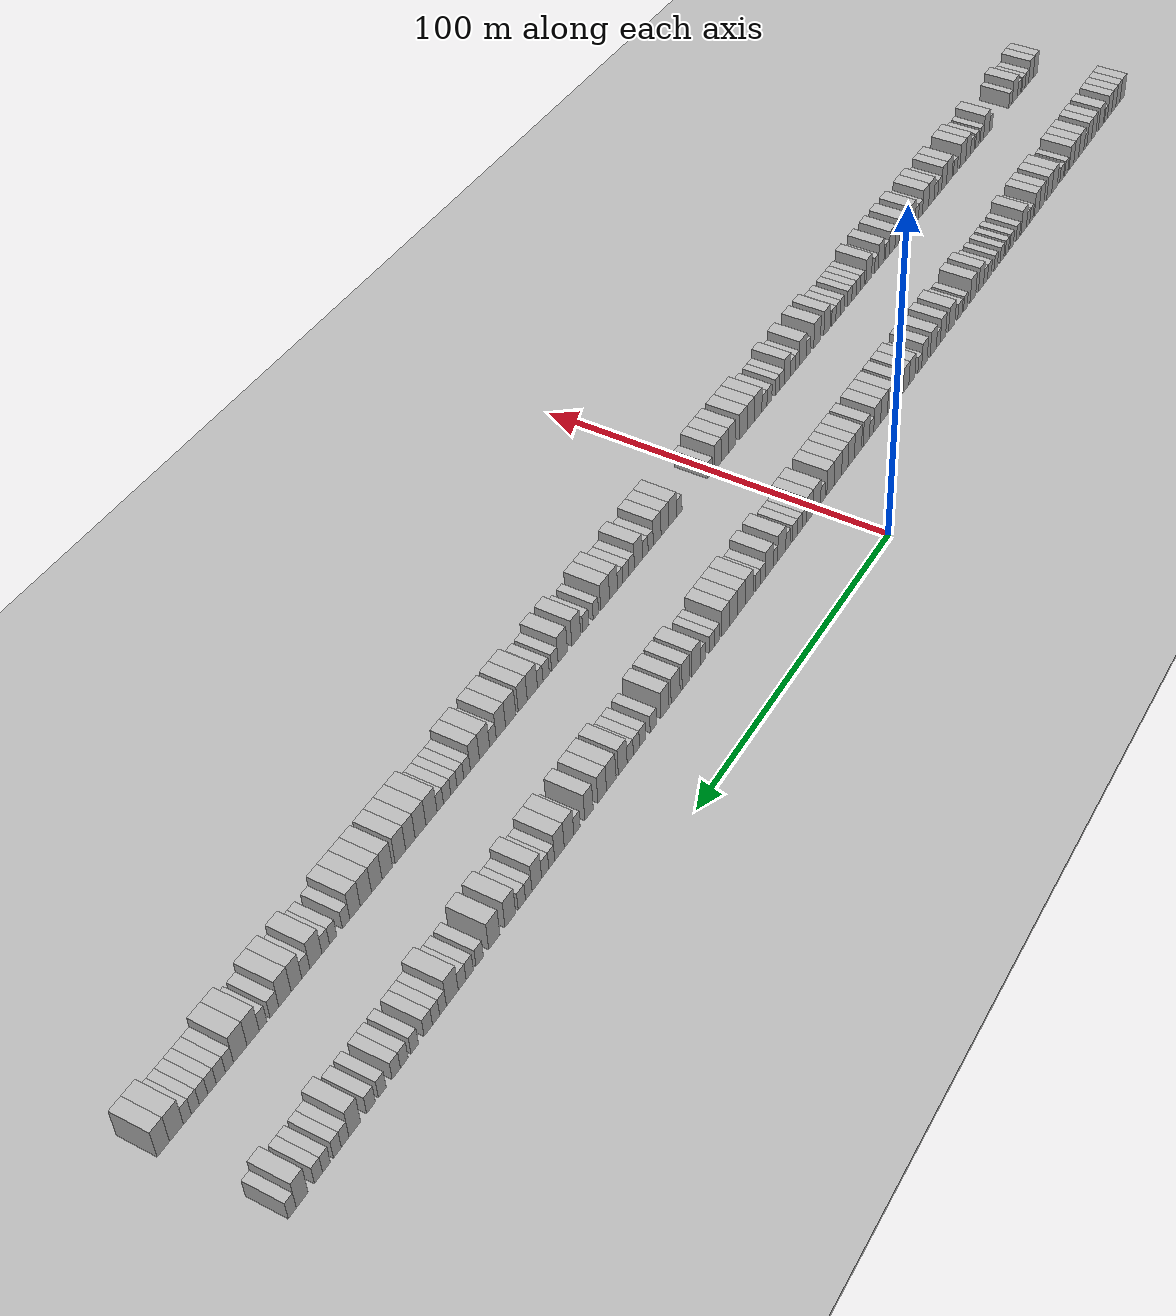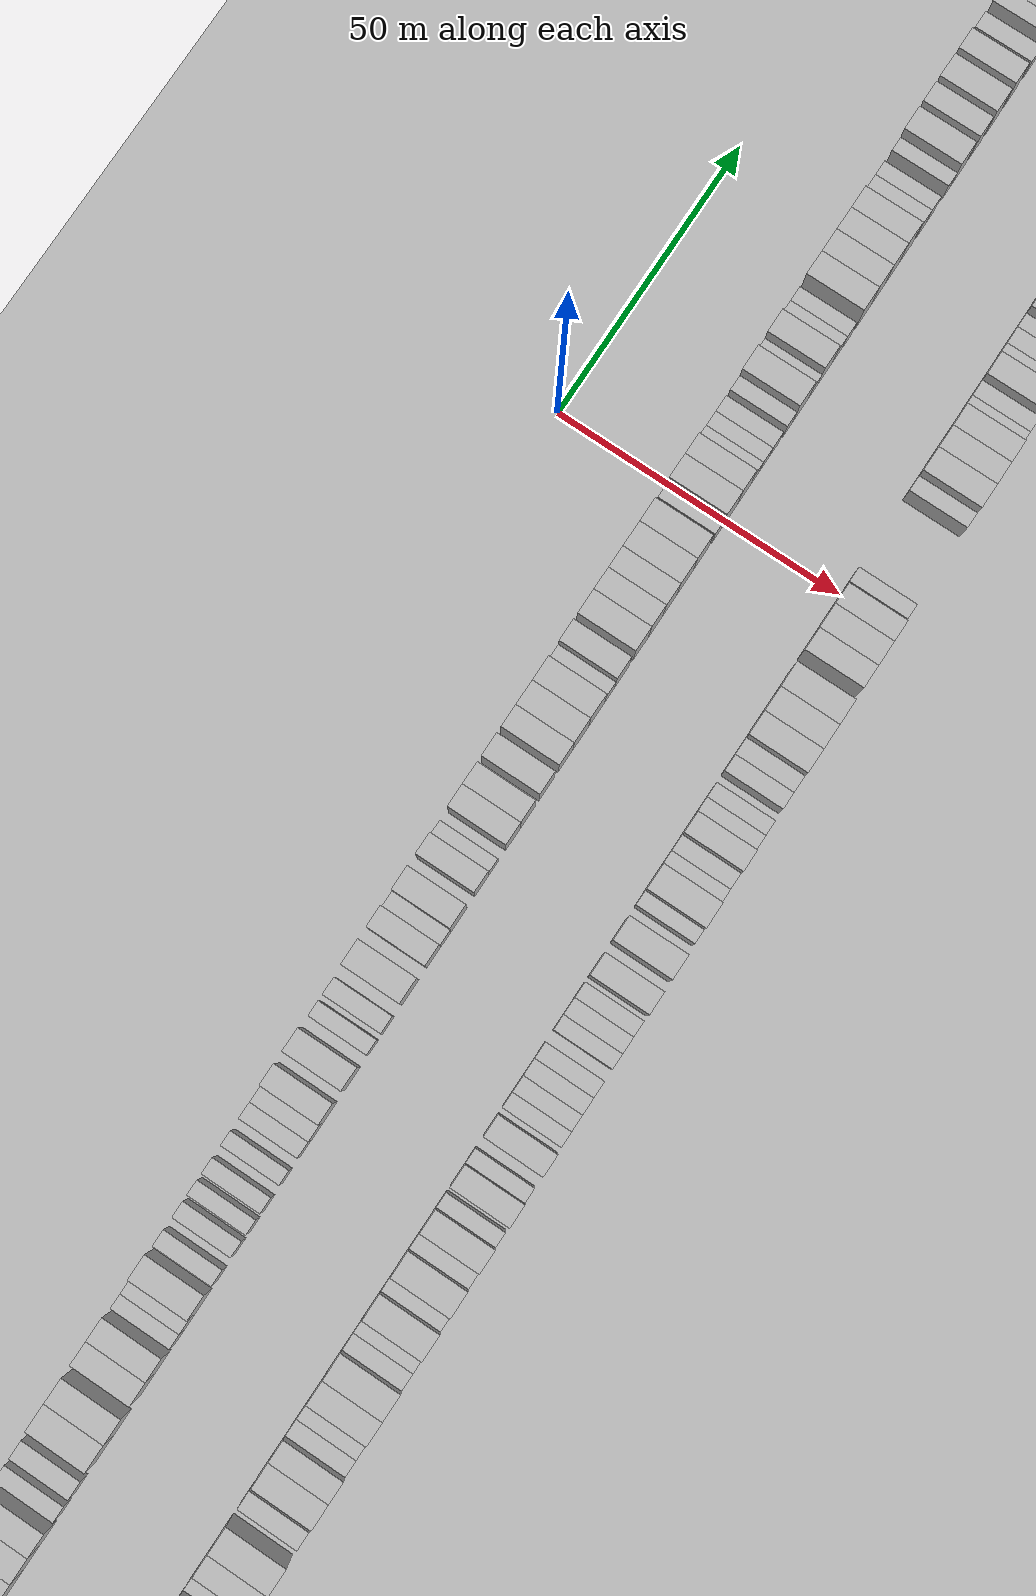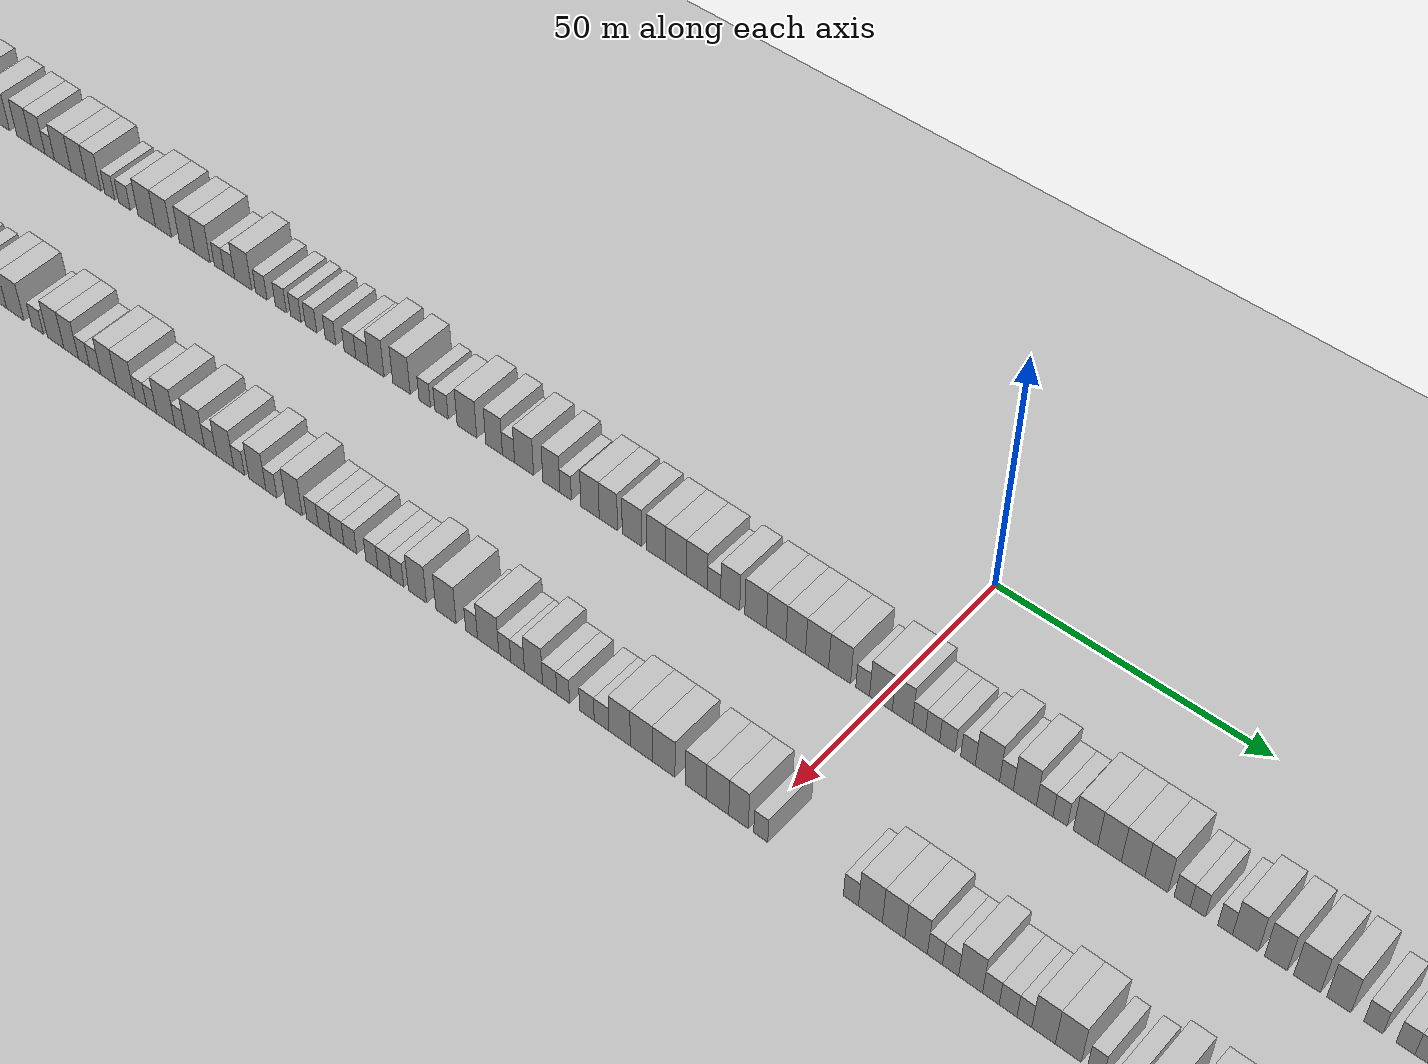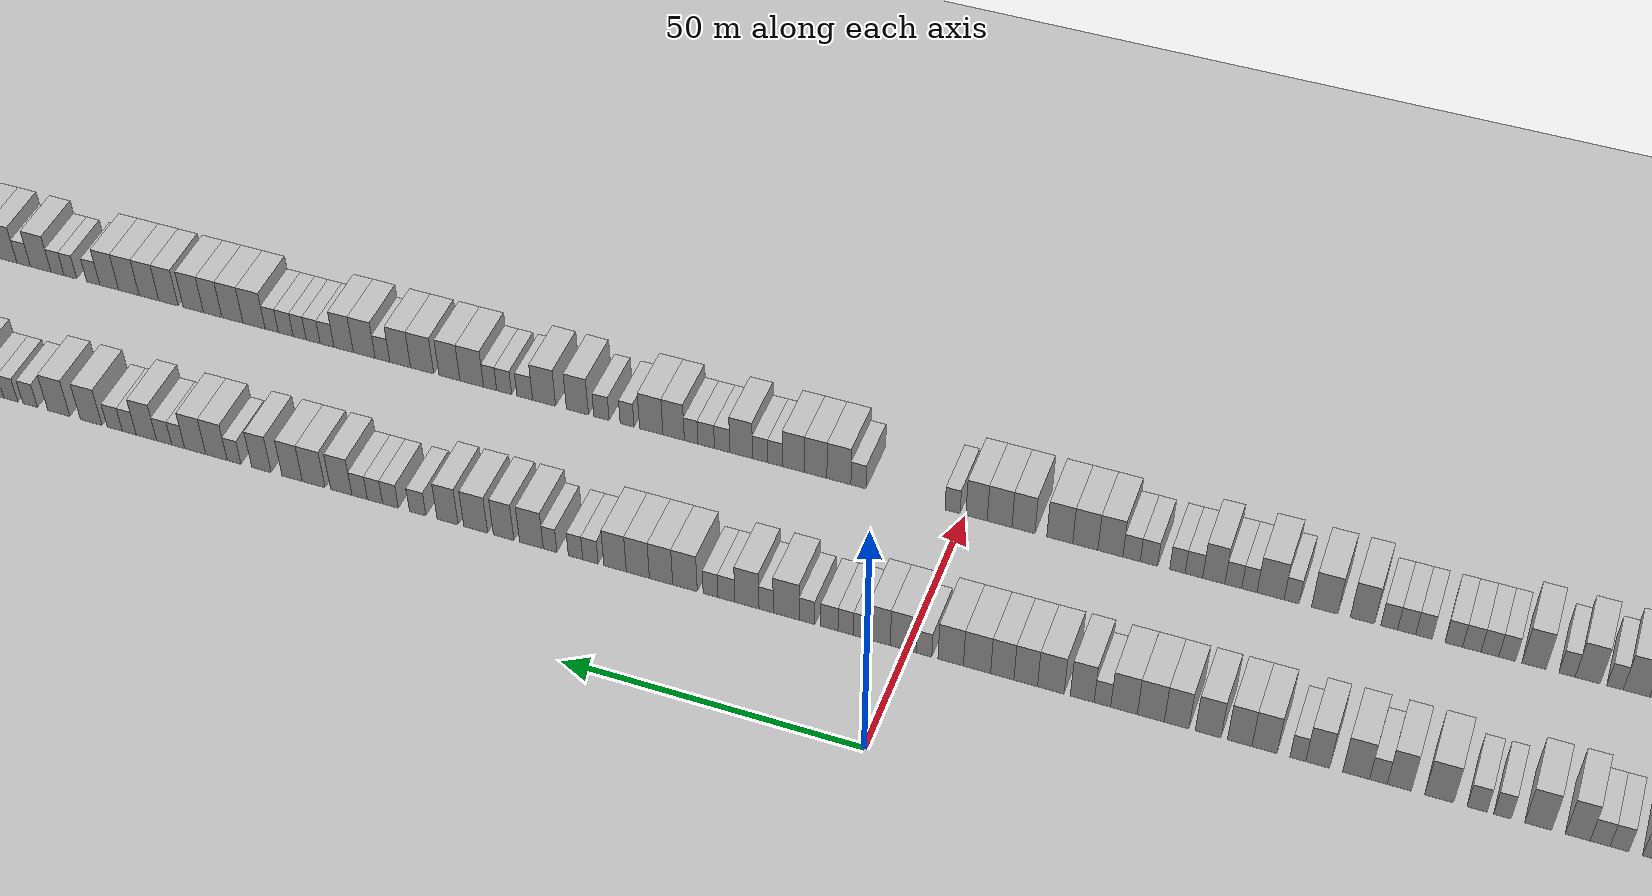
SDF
<?xml version="1.0" encoding="utf-8"?>

<sdf version="1.6">

   <world name="default">

      <gui fullscreen="0">

         <camera name="user_camera">

            <pose>-15 0 4.57585 0 0 0</pose>

            <view_controller>orbit</view_controller>

         </camera>

      </gui>

      <scene>

         <sky>

           <clouds>

             <speed>12</speed>

           </clouds>

         </sky>

         <ambient>0.4 0.4 0.4 1</ambient>

         <background>0.7 0.7 0.7 1</background>

         <shadows>1</shadows>

      </scene>

      <gravity>0 0 -9.8066</gravity>

      <magnetic_field>6e-06 2.3e-05 -4.2e-05</magnetic_field>

      <physics default="0" name="default_physics" type="ode">

         <ode>

            <solver>

               <type>quick</type>

               <iters>10</iters>

               <sor>1.0</sor>

               <use_dynamic_moi_rescaling>0</use_dynamic_moi_rescaling>

            </solver>

            <constraints>

               <cfm>0</cfm>

               <erp>0.2</erp>

               <contact_max_correcting_vel>100</contact_max_correcting_vel>

               <contact_surface_layer>0.001</contact_surface_layer>

            </constraints>

         </ode>

         <max_step_size>0.004</max_step_size>

         <real_time_factor>1</real_time_factor>

         <real_time_update_rate>250</real_time_update_rate>

      </physics>

      <light name="sun" type="directional">

         <cast_shadows>1</cast_shadows>

         <pose>0 0 10 0 0 0</pose>

         <diffuse>0.8 0.8 0.8 1</diffuse>

         <specular>0.2 0.2 0.2 1</specular>

         <attenuation>

            <range>1000</range>

            <constant>0.9</constant>

            <linear>0.01</linear>

            <quadratic>0.001</quadratic>

         </attenuation>

         <direction>-0.5 0.1 -0.9</direction>

      </light>

      <include>

         <name>ground_plane_1</name>

         <uri>model://HANNAS_ground_plane</uri>

         <pose>0 0 0  0 0 0</pose>

      </include>

      <include>

         <name>ground_plane_2</name>

         <uri>model://HANNAS_ground_plane</uri>

         <pose>100 0 0  0 0 0</pose>

      </include>

      <model name="building_1">

         <static>1</static>

         <pose frame="">25.0000 -217.9825 0 0.000000 0.000000 0.000000</pose>

         <link name="link">

            <pose frame="">0 0 4.50 0 0 0</pose>

            <collision name="collision">

               <geometry>

                  <box>

                     <size>10.0000 4.0350 9.0000</size>

                  </box>

               </geometry>

               <max_contacts>10</max_contacts>

               <surface>

                  <contact>

                     <ode/>

                  </contact>

                  <bounce/>

                  <friction>

                     <torsional>

                        <ode/>

                     </torsional>

                     <ode/>

                  </friction>

               </surface>

            </collision>

            <visual name="visual">

               <cast_shadows>0</cast_shadows>

               <geometry>

                  <box>

                     <size>10.0000 4.0350 9.0000</size>

                  </box>

               </geometry>

               <material>

                  <script>

                     <uri>model://HANNAS_wall/materials/scripts</uri>

                     <uri>model://HANNAS_wall/materials/textures</uri>

                     <name>vrc/HANNAS_wall</name>

                  </script>

               </material>

            </visual>

            <self_collide>0</self_collide>

            <enable_wind>0</enable_wind>

            <kinematic>0</kinematic>

         </link>

      </model>

      <model name="building_2">

         <static>1</static>

         <pose frame="">25.0000 -214.1253 0 0.000000 0.000000 0.000000</pose>

         <link name="link">

            <pose frame="">0 0 4.50 0 0 0</pose>

            <collision name="collision">

               <geometry>

                  <box>

                     <size>10.0000 3.6793 9.0000</size>

                  </box>

               </geometry>

               <max_contacts>10</max_contacts>

               <surface>

                  <contact>

                     <ode/>

                  </contact>

                  <bounce/>

                  <friction>

                     <torsional>

                        <ode/>

                     </torsional>

                     <ode/>

                  </friction>

               </surface>

            </collision>

            <visual name="visual">

               <cast_shadows>0</cast_shadows>

               <geometry>

                  <box>

                     <size>10.0000 3.6793 9.0000</size>

                  </box>

               </geometry>

               <material>

                  <script>

                     <uri>model://HANNAS_wall/materials/scripts</uri>

                     <uri>model://HANNAS_wall/materials/textures</uri>

                     <name>vrc/HANNAS_wall</name>

                  </script>

               </material>

            </visual>

            <self_collide>0</self_collide>

            <enable_wind>0</enable_wind>

            <kinematic>0</kinematic>

         </link>

      </model>

      <model name="building_3">

         <static>1</static>

         <pose frame="">25.0000 -210.3791 0 0.000000 0.000000 0.000000</pose>

         <link name="link">

            <pose frame="">0 0 4.50 0 0 0</pose>

            <collision name="collision">

               <geometry>

                  <box>

                     <size>10.0000 3.8131 9.0000</size>

                  </box>

               </geometry>

               <max_contacts>10</max_contacts>

               <surface>

                  <contact>

                     <ode/>

                  </contact>

                  <bounce/>

                  <friction>

                     <torsional>

                        <ode/>

                     </torsional>

                     <ode/>

                  </friction>

               </surface>

            </collision>

            <visual name="visual">

               <cast_shadows>0</cast_shadows>

               <geometry>

                  <box>

                     <size>10.0000 3.8131 9.0000</size>

                  </box>

               </geometry>

               <material>

                  <script>

                     <uri>model://HANNAS_wall/materials/scripts</uri>

                     <uri>model://HANNAS_wall/materials/textures</uri>

                     <name>vrc/HANNAS_wall</name>

                  </script>

               </material>

            </visual>

            <self_collide>0</self_collide>

            <enable_wind>0</enable_wind>

            <kinematic>0</kinematic>

         </link>

      </model>

      <model name="building_4">

         <static>1</static>

         <pose frame="">25.0000 -206.6053 0 0.000000 0.000000 0.000000</pose>

         <link name="link">

            <pose frame="">0 0 4.50 0 0 0</pose>

            <collision name="collision">

               <geometry>

                  <box>

                     <size>10.0000 3.7346 9.0000</size>

                  </box>

               </geometry>

               <max_contacts>10</max_contacts>

               <surface>

                  <contact>

                     <ode/>

                  </contact>

                  <bounce/>

                  <friction>

                     <torsional>

                        <ode/>

                     </torsional>

                     <ode/>

                  </friction>

               </surface>

            </collision>

            <visual name="visual">

               <cast_shadows>0</cast_shadows>

               <geometry>

                  <box>

                     <size>10.0000 3.7346 9.0000</size>

                  </box>

               </geometry>

               <material>

                  <script>

                     <uri>model://HANNAS_wall/materials/scripts</uri>

                     <uri>model://HANNAS_wall/materials/textures</uri>

                     <name>vrc/HANNAS_wall</name>

                  </script>

               </material>

            </visual>

            <self_collide>0</self_collide>

            <enable_wind>0</enable_wind>

            <kinematic>0</kinematic>

         </link>

      </model>

      <model name="building_5">

         <static>1</static>

         <pose frame="">25.0000 -203.4775 0 0.000000 0.000000 0.000000</pose>

         <link name="link">

            <pose frame="">0 0 3.00 0 0 0</pose>

            <collision name="collision">

               <geometry>

                  <box>

                     <size>10.0000 2.5211 6.0000</size>

                  </box>

               </geometry>

               <max_contacts>10</max_contacts>

               <surface>

                  <contact>

                     <ode/>

                  </contact>

                  <bounce/>

                  <friction>

                     <torsional>

                        <ode/>

                     </torsional>

                     <ode/>

                  </friction>

               </surface>

            </collision>

            <visual name="visual">

               <cast_shadows>0</cast_shadows>

               <geometry>

                  <box>

                     <size>10.0000 2.5211 6.0000</size>

                  </box>

               </geometry>

               <material>

                  <script>

                     <uri>model://HANNAS_wall/materials/scripts</uri>

                     <uri>model://HANNAS_wall/materials/textures</uri>

                     <name>vrc/HANNAS_wall</name>

                  </script>

               </material>

            </visual>

            <self_collide>0</self_collide>

            <enable_wind>0</enable_wind>

            <kinematic>0</kinematic>

         </link>

      </model>

      <model name="building_6">

         <static>1</static>

         <pose frame="">25.0000 -198.9948 0 0.000000 0.000000 0.000000</pose>

         <link name="link">

            <pose frame="">0 0 4.50 0 0 0</pose>

            <collision name="collision">

               <geometry>

                  <box>

                     <size>10.0000 4.4442 9.0000</size>

                  </box>

               </geometry>

               <max_contacts>10</max_contacts>

               <surface>

                  <contact>

                     <ode/>

                  </contact>

                  <bounce/>

                  <friction>

                     <torsional>

                        <ode/>

                     </torsional>

                     <ode/>

                  </friction>

               </surface>

            </collision>

            <visual name="visual">

               <cast_shadows>0</cast_shadows>

               <geometry>

                  <box>

                     <size>10.0000 4.4442 9.0000</size>

                  </box>

               </geometry>

               <material>

                  <script>

                     <uri>model://HANNAS_wall/materials/scripts</uri>

                     <uri>model://HANNAS_wall/materials/textures</uri>

                     <name>vrc/HANNAS_wall</name>

                  </script>

               </material>

            </visual>

            <self_collide>0</self_collide>

            <enable_wind>0</enable_wind>

            <kinematic>0</kinematic>

         </link>

      </model>

      <model name="building_7">

         <static>1</static>

         <pose frame="">25.0000 -192.8083 0 0.000000 0.000000 0.000000</pose>

         <link name="link">

            <pose frame="">0 0 4.50 0 0 0</pose>

            <collision name="collision">

               <geometry>

                  <box>

                     <size>10.0000 3.9289 9.0000</size>

                  </box>

               </geometry>

               <max_contacts>10</max_contacts>

               <surface>

                  <contact>

                     <ode/>

                  </contact>

                  <bounce/>

                  <friction>

                     <torsional>

                        <ode/>

                     </torsional>

                     <ode/>

                  </friction>

               </surface>

            </collision>

            <visual name="visual">

               <cast_shadows>0</cast_shadows>

               <geometry>

                  <box>

                     <size>10.0000 3.9289 9.0000</size>

                  </box>

               </geometry>

               <material>

                  <script>

                     <uri>model://HANNAS_wall/materials/scripts</uri>

                     <uri>model://HANNAS_wall/materials/textures</uri>

                     <name>vrc/HANNAS_wall</name>

                  </script>

               </material>

            </visual>

            <self_collide>0</self_collide>

            <enable_wind>0</enable_wind>

            <kinematic>0</kinematic>

         </link>

      </model>

      <model name="building_8">

         <static>1</static>

         <pose frame="">25.0000 -188.9560 0 0.000000 0.000000 0.000000</pose>

         <link name="link">

            <pose frame="">0 0 4.50 0 0 0</pose>

            <collision name="collision">

               <geometry>

                  <box>

                     <size>10.0000 3.7756 9.0000</size>

                  </box>

               </geometry>

               <max_contacts>10</max_contacts>

               <surface>

                  <contact>

                     <ode/>

                  </contact>

                  <bounce/>

                  <friction>

                     <torsional>

                        <ode/>

                     </torsional>

                     <ode/>

                  </friction>

               </surface>

            </collision>

            <visual name="visual">

               <cast_shadows>0</cast_shadows>

               <geometry>

                  <box>

                     <size>10.0000 3.7756 9.0000</size>

                  </box>

               </geometry>

               <material>

                  <script>

                     <uri>model://HANNAS_wall/materials/scripts</uri>

                     <uri>model://HANNAS_wall/materials/textures</uri>

                     <name>vrc/HANNAS_wall</name>

                  </script>

               </material>

            </visual>

            <self_collide>0</self_collide>

            <enable_wind>0</enable_wind>

            <kinematic>0</kinematic>

         </link>

      </model>

      <model name="building_9">

         <static>1</static>

         <pose frame="">25.0000 -185.7884 0 0.000000 0.000000 0.000000</pose>

         <link name="link">

            <pose frame="">0 0 3.00 0 0 0</pose>

            <collision name="collision">

               <geometry>

                  <box>

                     <size>10.0000 2.5595 6.0000</size>

                  </box>

               </geometry>

               <max_contacts>10</max_contacts>

               <surface>

                  <contact>

                     <ode/>

                  </contact>

                  <bounce/>

                  <friction>

                     <torsional>

                        <ode/>

                     </torsional>

                     <ode/>

                  </friction>

               </surface>

            </collision>

            <visual name="visual">

               <cast_shadows>0</cast_shadows>

               <geometry>

                  <box>

                     <size>10.0000 2.5595 6.0000</size>

                  </box>

               </geometry>

               <material>

                  <script>

                     <uri>model://HANNAS_wall/materials/scripts</uri>

                     <uri>model://HANNAS_wall/materials/textures</uri>

                     <name>vrc/HANNAS_wall</name>

                  </script>

               </material>

            </visual>

            <self_collide>0</self_collide>

            <enable_wind>0</enable_wind>

            <kinematic>0</kinematic>

         </link>

      </model>

      <model name="building_10">

         <static>1</static>

         <pose frame="">25.0000 -182.2898 0 0.000000 0.000000 0.000000</pose>

         <link name="link">

            <pose frame="">0 0 4.50 0 0 0</pose>

            <collision name="collision">

               <geometry>

                  <box>

                     <size>10.0000 4.4377 9.0000</size>

                  </box>

               </geometry>

               <max_contacts>10</max_contacts>

               <surface>

                  <contact>

                     <ode/>

                  </contact>

                  <bounce/>

                  <friction>

                     <torsional>

                        <ode/>

                     </torsional>

                     <ode/>

                  </friction>

               </surface>

            </collision>

            <visual name="visual">

               <cast_shadows>0</cast_shadows>

               <geometry>

                  <box>

                     <size>10.0000 4.4377 9.0000</size>

                  </box>

               </geometry>

               <material>

                  <script>

                     <uri>model://HANNAS_wall/materials/scripts</uri>

                     <uri>model://HANNAS_wall/materials/textures</uri>

                     <name>vrc/HANNAS_wall</name>

                  </script>

               </material>

            </visual>

            <self_collide>0</self_collide>

            <enable_wind>0</enable_wind>

            <kinematic>0</kinematic>

         </link>

      </model>

      <model name="building_11">

         <static>1</static>

         <pose frame="">25.0000 -178.0226 0 0.000000 0.000000 0.000000</pose>

         <link name="link">

            <pose frame="">0 0 4.50 0 0 0</pose>

            <collision name="collision">

               <geometry>

                  <box>

                     <size>10.0000 4.0966 9.0000</size>

                  </box>

               </geometry>

               <max_contacts>10</max_contacts>

               <surface>

                  <contact>

                     <ode/>

                  </contact>

                  <bounce/>

                  <friction>

                     <torsional>

                        <ode/>

                     </torsional>

                     <ode/>

                  </friction>

               </surface>

            </collision>

            <visual name="visual">

               <cast_shadows>0</cast_shadows>

               <geometry>

                  <box>

                     <size>10.0000 4.0966 9.0000</size>

                  </box>

               </geometry>

               <material>

                  <script>

                     <uri>model://HANNAS_wall/materials/scripts</uri>

                     <uri>model://HANNAS_wall/materials/textures</uri>

                     <name>vrc/HANNAS_wall</name>

                  </script>

               </material>

            </visual>

            <self_collide>0</self_collide>

            <enable_wind>0</enable_wind>

            <kinematic>0</kinematic>

         </link>

      </model>

      <model name="building_12">

         <static>1</static>

         <pose frame="">25.0000 -174.0531 0 0.000000 0.000000 0.000000</pose>

         <link name="link">

            <pose frame="">0 0 4.50 0 0 0</pose>

            <collision name="collision">

               <geometry>

                  <box>

                     <size>10.0000 3.8424 9.0000</size>

                  </box>

               </geometry>

               <max_contacts>10</max_contacts>

               <surface>

                  <contact>

                     <ode/>

                  </contact>

                  <bounce/>

                  <friction>

                     <torsional>

                        <ode/>

                     </torsional>

                     <ode/>

                  </friction>

               </surface>

            </collision>

            <visual name="visual">

               <cast_shadows>0</cast_shadows>

               <geometry>

                  <box>

                     <size>10.0000 3.8424 9.0000</size>

                  </box>

               </geometry>

               <material>

                  <script>

                     <uri>model://HANNAS_wall/materials/scripts</uri>

                     <uri>model://HANNAS_wall/materials/textures</uri>

                     <name>vrc/HANNAS_wall</name>

                  </script>

               </material>

            </visual>

            <self_collide>0</self_collide>

            <enable_wind>0</enable_wind>

            <kinematic>0</kinematic>

         </link>

      </model>

      <model name="building_13">

         <static>1</static>

         <pose frame="">25.0000 -169.8304 0 0.000000 0.000000 0.000000</pose>

         <link name="link">

            <pose frame="">0 0 3.00 0 0 0</pose>

            <collision name="collision">

               <geometry>

                  <box>

                     <size>10.0000 2.6031 6.0000</size>

                  </box>

               </geometry>

               <max_contacts>10</max_contacts>

               <surface>

                  <contact>

                     <ode/>

                  </contact>

                  <bounce/>

                  <friction>

                     <torsional>

                        <ode/>

                     </torsional>

                     <ode/>

                  </friction>

               </surface>

            </collision>

            <visual name="visual">

               <cast_shadows>0</cast_shadows>

               <geometry>

                  <box>

                     <size>10.0000 2.6031 6.0000</size>

                  </box>

               </geometry>

               <material>

                  <script>

                     <uri>model://HANNAS_wall/materials/scripts</uri>

                     <uri>model://HANNAS_wall/materials/textures</uri>

                     <name>vrc/HANNAS_wall</name>

                  </script>

               </material>

            </visual>

            <self_collide>0</self_collide>

            <enable_wind>0</enable_wind>

            <kinematic>0</kinematic>

         </link>

      </model>

      <model name="building_14">

         <static>1</static>

         <pose frame="">25.0000 -166.0289 0 0.000000 0.000000 0.000000</pose>

         <link name="link">

            <pose frame="">0 0 3.00 0 0 0</pose>

            <collision name="collision">

               <geometry>

                  <box>

                     <size>10.0000 2.9999 6.0000</size>

                  </box>

               </geometry>

               <max_contacts>10</max_contacts>

               <surface>

                  <contact>

                     <ode/>

                  </contact>

                  <bounce/>

                  <friction>

                     <torsional>

                        <ode/>

                     </torsional>

                     <ode/>

                  </friction>

               </surface>

            </collision>

            <visual name="visual">

               <cast_shadows>0</cast_shadows>

               <geometry>

                  <box>

                     <size>10.0000 2.9999 6.0000</size>

                  </box>

               </geometry>

               <material>

                  <script>

                     <uri>model://HANNAS_wall/materials/scripts</uri>

                     <uri>model://HANNAS_wall/materials/textures</uri>

                     <name>vrc/HANNAS_wall</name>

                  </script>

               </material>

            </visual>

            <self_collide>0</self_collide>

            <enable_wind>0</enable_wind>

            <kinematic>0</kinematic>

         </link>

      </model>

      <model name="building_15">

         <static>1</static>

         <pose frame="">25.0000 -160.2806 0 0.000000 0.000000 0.000000</pose>

         <link name="link">

            <pose frame="">0 0 4.50 0 0 0</pose>

            <collision name="collision">

               <geometry>

                  <box>

                     <size>10.0000 4.4967 9.0000</size>

                  </box>

               </geometry>

               <max_contacts>10</max_contacts>

               <surface>

                  <contact>

                     <ode/>

                  </contact>

                  <bounce/>

                  <friction>

                     <torsional>

                        <ode/>

                     </torsional>

                     <ode/>

                  </friction>

               </surface>

            </collision>

            <visual name="visual">

               <cast_shadows>0</cast_shadows>

               <geometry>

                  <box>

                     <size>10.0000 4.4967 9.0000</size>

                  </box>

               </geometry>

               <material>

                  <script>

                     <uri>model://HANNAS_wall/materials/scripts</uri>

                     <uri>model://HANNAS_wall/materials/textures</uri>

                     <name>vrc/HANNAS_wall</name>

                  </script>

               </material>

            </visual>

            <self_collide>0</self_collide>

            <enable_wind>0</enable_wind>

            <kinematic>0</kinematic>

         </link>

      </model>

      <model name="building_16">

         <static>1</static>

         <pose frame="">25.0000 -155.9612 0 0.000000 0.000000 0.000000</pose>

         <link name="link">

            <pose frame="">0 0 4.50 0 0 0</pose>

            <collision name="collision">

               <geometry>

                  <box>

                     <size>10.0000 4.1421 9.0000</size>

                  </box>

               </geometry>

               <max_contacts>10</max_contacts>

               <surface>

                  <contact>

                     <ode/>

                  </contact>

                  <bounce/>

                  <friction>

                     <torsional>

                        <ode/>

                     </torsional>

                     <ode/>

                  </friction>

               </surface>

            </collision>

            <visual name="visual">

               <cast_shadows>0</cast_shadows>

               <geometry>

                  <box>

                     <size>10.0000 4.1421 9.0000</size>

                  </box>

               </geometry>

               <material>

                  <script>

                     <uri>model://HANNAS_wall/materials/scripts</uri>

                     <uri>model://HANNAS_wall/materials/textures</uri>

                     <name>vrc/HANNAS_wall</name>

                  </script>

               </material>

            </visual>

            <self_collide>0</self_collide>

            <enable_wind>0</enable_wind>

            <kinematic>0</kinematic>

         </link>

      </model>

      <model name="building_17">

         <static>1</static>

         <pose frame="">25.0000 -149.9488 0 0.000000 0.000000 0.000000</pose>

         <link name="link">

            <pose frame="">0 0 4.50 0 0 0</pose>

            <collision name="collision">

               <geometry>

                  <box>

                     <size>10.0000 3.8826 9.0000</size>

                  </box>

               </geometry>

               <max_contacts>10</max_contacts>

               <surface>

                  <contact>

                     <ode/>

                  </contact>

                  <bounce/>

                  <friction>

                     <torsional>

                        <ode/>

                     </torsional>

                     <ode/>

                  </friction>

               </surface>

            </collision>

            <visual name="visual">

               <cast_shadows>0</cast_shadows>

               <geometry>

                  <box>

                     <size>10.0000 3.8826 9.0000</size>

                  </box>

               </geometry>

               <material>

                  <script>

                     <uri>model://HANNAS_wall/materials/scripts</uri>

                     <uri>model://HANNAS_wall/materials/textures</uri>

                     <name>vrc/HANNAS_wall</name>

                  </script>

               </material>

            </visual>

            <self_collide>0</self_collide>

            <enable_wind>0</enable_wind>

            <kinematic>0</kinematic>

         </link>

      </model>

      <model name="building_18">

         <static>1</static>

         <pose frame="">25.0000 -146.0765 0 0.000000 0.000000 0.000000</pose>

         <link name="link">

            <pose frame="">0 0 4.50 0 0 0</pose>

            <collision name="collision">

               <geometry>

                  <box>

                     <size>10.0000 3.8621 9.0000</size>

                  </box>

               </geometry>

               <max_contacts>10</max_contacts>

               <surface>

                  <contact>

                     <ode/>

                  </contact>

                  <bounce/>

                  <friction>

                     <torsional>

                        <ode/>

                     </torsional>

                     <ode/>

                  </friction>

               </surface>

            </collision>

            <visual name="visual">

               <cast_shadows>0</cast_shadows>

               <geometry>

                  <box>

                     <size>10.0000 3.8621 9.0000</size>

                  </box>

               </geometry>

               <material>

                  <script>

                     <uri>model://HANNAS_wall/materials/scripts</uri>

                     <uri>model://HANNAS_wall/materials/textures</uri>

                     <name>vrc/HANNAS_wall</name>

                  </script>

               </material>

            </visual>

            <self_collide>0</self_collide>

            <enable_wind>0</enable_wind>

            <kinematic>0</kinematic>

         </link>

      </model>

      <model name="building_19">

         <static>1</static>

         <pose frame="">25.0000 -141.9401 0 0.000000 0.000000 0.000000</pose>

         <link name="link">

            <pose frame="">0 0 3.00 0 0 0</pose>

            <collision name="collision">

               <geometry>

                  <box>

                     <size>10.0000 2.4108 6.0000</size>

                  </box>

               </geometry>

               <max_contacts>10</max_contacts>

               <surface>

                  <contact>

                     <ode/>

                  </contact>

                  <bounce/>

                  <friction>

                     <torsional>

                        <ode/>

                     </torsional>

                     <ode/>

                  </friction>

               </surface>

            </collision>

            <visual name="visual">

               <cast_shadows>0</cast_shadows>

               <geometry>

                  <box>

                     <size>10.0000 2.4108 6.0000</size>

                  </box>

               </geometry>

               <material>

                  <script>

                     <uri>model://HANNAS_wall/materials/scripts</uri>

                     <uri>model://HANNAS_wall/materials/textures</uri>

                     <name>vrc/HANNAS_wall</name>

                  </script>

               </material>

            </visual>

            <self_collide>0</self_collide>

            <enable_wind>0</enable_wind>

            <kinematic>0</kinematic>

         </link>

      </model>

      <model name="building_20">

         <static>1</static>

         <pose frame="">25.0000 -139.4036 0 0.000000 0.000000 0.000000</pose>

         <link name="link">

            <pose frame="">0 0 3.00 0 0 0</pose>

            <collision name="collision">

               <geometry>

                  <box>

                     <size>10.0000 2.6622 6.0000</size>

                  </box>

               </geometry>

               <max_contacts>10</max_contacts>

               <surface>

                  <contact>

                     <ode/>

                  </contact>

                  <bounce/>

                  <friction>

                     <torsional>

                        <ode/>

                     </torsional>

                     <ode/>

                  </friction>

               </surface>

            </collision>

            <visual name="visual">

               <cast_shadows>0</cast_shadows>

               <geometry>

                  <box>

                     <size>10.0000 2.6622 6.0000</size>

                  </box>

               </geometry>

               <material>

                  <script>

                     <uri>model://HANNAS_wall/materials/scripts</uri>

                     <uri>model://HANNAS_wall/materials/textures</uri>

                     <name>vrc/HANNAS_wall</name>

                  </script>

               </material>

            </visual>

            <self_collide>0</self_collide>

            <enable_wind>0</enable_wind>

            <kinematic>0</kinematic>

         </link>

      </model>

      <model name="building_21">

         <static>1</static>

         <pose frame="">25.0000 -135.9881 0 0.000000 0.000000 0.000000</pose>

         <link name="link">

            <pose frame="">0 0 4.50 0 0 0</pose>

            <collision name="collision">

               <geometry>

                  <box>

                     <size>10.0000 4.1687 9.0000</size>

                  </box>

               </geometry>

               <max_contacts>10</max_contacts>

               <surface>

                  <contact>

                     <ode/>

                  </contact>

                  <bounce/>

                  <friction>

                     <torsional>

                        <ode/>

                     </torsional>

                     <ode/>

                  </friction>

               </surface>

            </collision>

            <visual name="visual">

               <cast_shadows>0</cast_shadows>

               <geometry>

                  <box>

                     <size>10.0000 4.1687 9.0000</size>

                  </box>

               </geometry>

               <material>

                  <script>

                     <uri>model://HANNAS_wall/materials/scripts</uri>

                     <uri>model://HANNAS_wall/materials/textures</uri>

                     <name>vrc/HANNAS_wall</name>

                  </script>

               </material>

            </visual>

            <self_collide>0</self_collide>

            <enable_wind>0</enable_wind>

            <kinematic>0</kinematic>

         </link>

      </model>

      <model name="building_22">

         <static>1</static>

         <pose frame="">25.0000 -131.5292 0 0.000000 0.000000 0.000000</pose>

         <link name="link">

            <pose frame="">0 0 3.00 0 0 0</pose>

            <collision name="collision">

               <geometry>

                  <box>

                     <size>10.0000 2.7491 6.0000</size>

                  </box>

               </geometry>

               <max_contacts>10</max_contacts>

               <surface>

                  <contact>

                     <ode/>

                  </contact>

                  <bounce/>

                  <friction>

                     <torsional>

                        <ode/>

                     </torsional>

                     <ode/>

                  </friction>

               </surface>

            </collision>

            <visual name="visual">

               <cast_shadows>0</cast_shadows>

               <geometry>

                  <box>

                     <size>10.0000 2.7491 6.0000</size>

                  </box>

               </geometry>

               <material>

                  <script>

                     <uri>model://HANNAS_wall/materials/scripts</uri>

                     <uri>model://HANNAS_wall/materials/textures</uri>

                     <name>vrc/HANNAS_wall</name>

                  </script>

               </material>

            </visual>

            <self_collide>0</self_collide>

            <enable_wind>0</enable_wind>

            <kinematic>0</kinematic>

         </link>

      </model>

      <model name="building_23">

         <static>1</static>

         <pose frame="">25.0000 -126.8021 0 0.000000 0.000000 0.000000</pose>

         <link name="link">

            <pose frame="">0 0 3.00 0 0 0</pose>

            <collision name="collision">

               <geometry>

                  <box>

                     <size>10.0000 2.7052 6.0000</size>

                  </box>

               </geometry>

               <max_contacts>10</max_contacts>

               <surface>

                  <contact>

                     <ode/>

                  </contact>

                  <bounce/>

                  <friction>

                     <torsional>

                        <ode/>

                     </torsional>

                     <ode/>

                  </friction>

               </surface>

            </collision>

            <visual name="visual">

               <cast_shadows>0</cast_shadows>

               <geometry>

                  <box>

                     <size>10.0000 2.7052 6.0000</size>

                  </box>

               </geometry>

               <material>

                  <script>

                     <uri>model://HANNAS_wall/materials/scripts</uri>

                     <uri>model://HANNAS_wall/materials/textures</uri>

                     <name>vrc/HANNAS_wall</name>

                  </script>

               </material>

            </visual>

            <self_collide>0</self_collide>

            <enable_wind>0</enable_wind>

            <kinematic>0</kinematic>

         </link>

      </model>

      <model name="building_24">

         <static>1</static>

         <pose frame="">25.0000 -123.1851 0 0.000000 0.000000 0.000000</pose>

         <link name="link">

            <pose frame="">0 0 3.00 0 0 0</pose>

            <collision name="collision">

               <geometry>

                  <box>

                     <size>10.0000 2.5289 6.0000</size>

                  </box>

               </geometry>

               <max_contacts>10</max_contacts>

               <surface>

                  <contact>

                     <ode/>

                  </contact>

                  <bounce/>

                  <friction>

                     <torsional>

                        <ode/>

                     </torsional>

                     <ode/>

                  </friction>

               </surface>

            </collision>

            <visual name="visual">

               <cast_shadows>0</cast_shadows>

               <geometry>

                  <box>

                     <size>10.0000 2.5289 6.0000</size>

                  </box>

               </geometry>

               <material>

                  <script>

                     <uri>model://HANNAS_wall/materials/scripts</uri>

                     <uri>model://HANNAS_wall/materials/textures</uri>

                     <name>vrc/HANNAS_wall</name>

                  </script>

               </material>

            </visual>

            <self_collide>0</self_collide>

            <enable_wind>0</enable_wind>

            <kinematic>0</kinematic>

         </link>

      </model>

      <model name="building_25">

         <static>1</static>

         <pose frame="">25.0000 -119.5585 0 0.000000 0.000000 0.000000</pose>

         <link name="link">

            <pose frame="">0 0 3.00 0 0 0</pose>

            <collision name="collision">

               <geometry>

                  <box>

                     <size>10.0000 2.7244 6.0000</size>

                  </box>

               </geometry>

               <max_contacts>10</max_contacts>

               <surface>

                  <contact>

                     <ode/>

                  </contact>

                  <bounce/>

                  <friction>

                     <torsional>

                        <ode/>

                     </torsional>

                     <ode/>

                  </friction>

               </surface>

            </collision>

            <visual name="visual">

               <cast_shadows>0</cast_shadows>

               <geometry>

                  <box>

                     <size>10.0000 2.7244 6.0000</size>

                  </box>

               </geometry>

               <material>

                  <script>

                     <uri>model://HANNAS_wall/materials/scripts</uri>

                     <uri>model://HANNAS_wall/materials/textures</uri>

                     <name>vrc/HANNAS_wall</name>

                  </script>

               </material>

            </visual>

            <self_collide>0</self_collide>

            <enable_wind>0</enable_wind>

            <kinematic>0</kinematic>

         </link>

      </model>

      <model name="building_26">

         <static>1</static>

         <pose frame="">25.0000 -114.9538 0 0.000000 0.000000 0.000000</pose>

         <link name="link">

            <pose frame="">0 0 3.00 0 0 0</pose>

            <collision name="collision">

               <geometry>

                  <box>

                     <size>10.0000 2.4851 6.0000</size>

                  </box>

               </geometry>

               <max_contacts>10</max_contacts>

               <surface>

                  <contact>

                     <ode/>

                  </contact>

                  <bounce/>

                  <friction>

                     <torsional>

                        <ode/>

                     </torsional>

                     <ode/>

                  </friction>

               </surface>

            </collision>

            <visual name="visual">

               <cast_shadows>0</cast_shadows>

               <geometry>

                  <box>

                     <size>10.0000 2.4851 6.0000</size>

                  </box>

               </geometry>

               <material>

                  <script>

                     <uri>model://HANNAS_wall/materials/scripts</uri>

                     <uri>model://HANNAS_wall/materials/textures</uri>

                     <name>vrc/HANNAS_wall</name>

                  </script>

               </material>

            </visual>

            <self_collide>0</self_collide>

            <enable_wind>0</enable_wind>

            <kinematic>0</kinematic>

         </link>

      </model>

      <model name="building_27">

         <static>1</static>

         <pose frame="">25.0000 -110.3410 0 0.000000 0.000000 0.000000</pose>

         <link name="link">

            <pose frame="">0 0 3.00 0 0 0</pose>

            <collision name="collision">

               <geometry>

                  <box>

                     <size>10.0000 2.7404 6.0000</size>

                  </box>

               </geometry>

               <max_contacts>10</max_contacts>

               <surface>

                  <contact>

                     <ode/>

                  </contact>

                  <bounce/>

                  <friction>

                     <torsional>

                        <ode/>

                     </torsional>

                     <ode/>

                  </friction>

               </surface>

            </collision>

            <visual name="visual">

               <cast_shadows>0</cast_shadows>

               <geometry>

                  <box>

                     <size>10.0000 2.7404 6.0000</size>

                  </box>

               </geometry>

               <material>

                  <script>

                     <uri>model://HANNAS_wall/materials/scripts</uri>

                     <uri>model://HANNAS_wall/materials/textures</uri>

                     <name>vrc/HANNAS_wall</name>

                  </script>

               </material>

            </visual>

            <self_collide>0</self_collide>

            <enable_wind>0</enable_wind>

            <kinematic>0</kinematic>

         </link>

      </model>

      <model name="building_28">

         <static>1</static>

         <pose frame="">25.0000 -107.5178 0 0.000000 0.000000 0.000000</pose>

         <link name="link">

            <pose frame="">0 0 3.00 0 0 0</pose>

            <collision name="collision">

               <geometry>

                  <box>

                     <size>10.0000 2.9060 6.0000</size>

                  </box>

               </geometry>

               <max_contacts>10</max_contacts>

               <surface>

                  <contact>

                     <ode/>

                  </contact>

                  <bounce/>

                  <friction>

                     <torsional>

                        <ode/>

                     </torsional>

                     <ode/>

                  </friction>

               </surface>

            </collision>

            <visual name="visual">

               <cast_shadows>0</cast_shadows>

               <geometry>

                  <box>

                     <size>10.0000 2.9060 6.0000</size>

                  </box>

               </geometry>

               <material>

                  <script>

                     <uri>model://HANNAS_wall/materials/scripts</uri>

                     <uri>model://HANNAS_wall/materials/textures</uri>

                     <name>vrc/HANNAS_wall</name>

                  </script>

               </material>

            </visual>

            <self_collide>0</self_collide>

            <enable_wind>0</enable_wind>

            <kinematic>0</kinematic>

         </link>

      </model>

      <model name="building_29">

         <static>1</static>

         <pose frame="">25.0000 -104.2438 0 0.000000 0.000000 0.000000</pose>

         <link name="link">

            <pose frame="">0 0 4.50 0 0 0</pose>

            <collision name="collision">

               <geometry>

                  <box>

                     <size>10.0000 3.6421 9.0000</size>

                  </box>

               </geometry>

               <max_contacts>10</max_contacts>

               <surface>

                  <contact>

                     <ode/>

                  </contact>

                  <bounce/>

                  <friction>

                     <torsional>

                        <ode/>

                     </torsional>

                     <ode/>

                  </friction>

               </surface>

            </collision>

            <visual name="visual">

               <cast_shadows>0</cast_shadows>

               <geometry>

                  <box>

                     <size>10.0000 3.6421 9.0000</size>

                  </box>

               </geometry>

               <material>

                  <script>

                     <uri>model://HANNAS_wall/materials/scripts</uri>

                     <uri>model://HANNAS_wall/materials/textures</uri>

                     <name>vrc/HANNAS_wall</name>

                  </script>

               </material>

            </visual>

            <self_collide>0</self_collide>

            <enable_wind>0</enable_wind>

            <kinematic>0</kinematic>

         </link>

      </model>

      <model name="building_30">

         <static>1</static>

         <pose frame="">25.0000 -98.4290 0 0.000000 0.000000 0.000000</pose>

         <link name="link">

            <pose frame="">0 0 4.50 0 0 0</pose>

            <collision name="collision">

               <geometry>

                  <box>

                     <size>10.0000 3.9873 9.0000</size>

                  </box>

               </geometry>

               <max_contacts>10</max_contacts>

               <surface>

                  <contact>

                     <ode/>

                  </contact>

                  <bounce/>

                  <friction>

                     <torsional>

                        <ode/>

                     </torsional>

                     <ode/>

                  </friction>

               </surface>

            </collision>

            <visual name="visual">

               <cast_shadows>0</cast_shadows>

               <geometry>

                  <box>

                     <size>10.0000 3.9873 9.0000</size>

                  </box>

               </geometry>

               <material>

                  <script>

                     <uri>model://HANNAS_wall/materials/scripts</uri>

                     <uri>model://HANNAS_wall/materials/textures</uri>

                     <name>vrc/HANNAS_wall</name>

                  </script>

               </material>

            </visual>

            <self_collide>0</self_collide>

            <enable_wind>0</enable_wind>

            <kinematic>0</kinematic>

         </link>

      </model>

      <model name="building_31">

         <static>1</static>

         <pose frame="">25.0000 -93.1362 0 0.000000 0.000000 0.000000</pose>

         <link name="link">

            <pose frame="">0 0 3.00 0 0 0</pose>

            <collision name="collision">

               <geometry>

                  <box>

                     <size>10.0000 2.5985 6.0000</size>

                  </box>

               </geometry>

               <max_contacts>10</max_contacts>

               <surface>

                  <contact>

                     <ode/>

                  </contact>

                  <bounce/>

                  <friction>

                     <torsional>

                        <ode/>

                     </torsional>

                     <ode/>

                  </friction>

               </surface>

            </collision>

            <visual name="visual">

               <cast_shadows>0</cast_shadows>

               <geometry>

                  <box>

                     <size>10.0000 2.5985 6.0000</size>

                  </box>

               </geometry>

               <material>

                  <script>

                     <uri>model://HANNAS_wall/materials/scripts</uri>

                     <uri>model://HANNAS_wall/materials/textures</uri>

                     <name>vrc/HANNAS_wall</name>

                  </script>

               </material>

            </visual>

            <self_collide>0</self_collide>

            <enable_wind>0</enable_wind>

            <kinematic>0</kinematic>

         </link>

      </model>

      <model name="building_32">

         <static>1</static>

         <pose frame="">25.0000 -89.3451 0 0.000000 0.000000 0.000000</pose>

         <link name="link">

            <pose frame="">0 0 3.00 0 0 0</pose>

            <collision name="collision">

               <geometry>

                  <box>

                     <size>10.0000 2.9836 6.0000</size>

                  </box>

               </geometry>

               <max_contacts>10</max_contacts>

               <surface>

                  <contact>

                     <ode/>

                  </contact>

                  <bounce/>

                  <friction>

                     <torsional>

                        <ode/>

                     </torsional>

                     <ode/>

                  </friction>

               </surface>

            </collision>

            <visual name="visual">

               <cast_shadows>0</cast_shadows>

               <geometry>

                  <box>

                     <size>10.0000 2.9836 6.0000</size>

                  </box>

               </geometry>

               <material>

                  <script>

                     <uri>model://HANNAS_wall/materials/scripts</uri>

                     <uri>model://HANNAS_wall/materials/textures</uri>

                     <name>vrc/HANNAS_wall</name>

                  </script>

               </material>

            </visual>

            <self_collide>0</self_collide>

            <enable_wind>0</enable_wind>

            <kinematic>0</kinematic>

         </link>

      </model>

      <model name="building_33">

         <static>1</static>

         <pose frame="">25.0000 -83.6775 0 0.000000 0.000000 0.000000</pose>

         <link name="link">

            <pose frame="">0 0 4.50 0 0 0</pose>

            <collision name="collision">

               <geometry>

                  <box>

                     <size>10.0000 4.3515 9.0000</size>

                  </box>

               </geometry>

               <max_contacts>10</max_contacts>

               <surface>

                  <contact>

                     <ode/>

                  </contact>

                  <bounce/>

                  <friction>

                     <torsional>

                        <ode/>

                     </torsional>

                     <ode/>

                  </friction>

               </surface>

            </collision>

            <visual name="visual">

               <cast_shadows>0</cast_shadows>

               <geometry>

                  <box>

                     <size>10.0000 4.3515 9.0000</size>

                  </box>

               </geometry>

               <material>

                  <script>

                     <uri>model://HANNAS_wall/materials/scripts</uri>

                     <uri>model://HANNAS_wall/materials/textures</uri>

                     <name>vrc/HANNAS_wall</name>

                  </script>

               </material>

            </visual>

            <self_collide>0</self_collide>

            <enable_wind>0</enable_wind>

            <kinematic>0</kinematic>

         </link>

      </model>

      <model name="building_34">

         <static>1</static>

         <pose frame="">25.0000 -77.6748 0 0.000000 0.000000 0.000000</pose>

         <link name="link">

            <pose frame="">0 0 4.50 0 0 0</pose>

            <collision name="collision">

               <geometry>

                  <box>

                     <size>10.0000 3.6540 9.0000</size>

                  </box>

               </geometry>

               <max_contacts>10</max_contacts>

               <surface>

                  <contact>

                     <ode/>

                  </contact>

                  <bounce/>

                  <friction>

                     <torsional>

                        <ode/>

                     </torsional>

                     <ode/>

                  </friction>

               </surface>

            </collision>

            <visual name="visual">

               <cast_shadows>0</cast_shadows>

               <geometry>

                  <box>

                     <size>10.0000 3.6540 9.0000</size>

                  </box>

               </geometry>

               <material>

                  <script>

                     <uri>model://HANNAS_wall/materials/scripts</uri>

                     <uri>model://HANNAS_wall/materials/textures</uri>

                     <name>vrc/HANNAS_wall</name>

                  </script>

               </material>

            </visual>

            <self_collide>0</self_collide>

            <enable_wind>0</enable_wind>

            <kinematic>0</kinematic>

         </link>

      </model>

      <model name="building_35">

         <static>1</static>

         <pose frame="">25.0000 -74.5172 0 0.000000 0.000000 0.000000</pose>

         <link name="link">

            <pose frame="">0 0 3.00 0 0 0</pose>

            <collision name="collision">

               <geometry>

                  <box>

                     <size>10.0000 2.6610 6.0000</size>

                  </box>

               </geometry>

               <max_contacts>10</max_contacts>

               <surface>

                  <contact>

                     <ode/>

                  </contact>

                  <bounce/>

                  <friction>

                     <torsional>

                        <ode/>

                     </torsional>

                     <ode/>

                  </friction>

               </surface>

            </collision>

            <visual name="visual">

               <cast_shadows>0</cast_shadows>

               <geometry>

                  <box>

                     <size>10.0000 2.6610 6.0000</size>

                  </box>

               </geometry>

               <material>

                  <script>

                     <uri>model://HANNAS_wall/materials/scripts</uri>

                     <uri>model://HANNAS_wall/materials/textures</uri>

                     <name>vrc/HANNAS_wall</name>

                  </script>

               </material>

            </visual>

            <self_collide>0</self_collide>

            <enable_wind>0</enable_wind>

            <kinematic>0</kinematic>

         </link>

      </model>

      <model name="building_36">

         <static>1</static>

         <pose frame="">25.0000 -71.1314 0 0.000000 0.000000 0.000000</pose>

         <link name="link">

            <pose frame="">0 0 4.50 0 0 0</pose>

            <collision name="collision">

               <geometry>

                  <box>

                     <size>10.0000 4.1106 9.0000</size>

                  </box>

               </geometry>

               <max_contacts>10</max_contacts>

               <surface>

                  <contact>

                     <ode/>

                  </contact>

                  <bounce/>

                  <friction>

                     <torsional>

                        <ode/>

                     </torsional>

                     <ode/>

                  </friction>

               </surface>

            </collision>

            <visual name="visual">

               <cast_shadows>0</cast_shadows>

               <geometry>

                  <box>

                     <size>10.0000 4.1106 9.0000</size>

                  </box>

               </geometry>

               <material>

                  <script>

                     <uri>model://HANNAS_wall/materials/scripts</uri>

                     <uri>model://HANNAS_wall/materials/textures</uri>

                     <name>vrc/HANNAS_wall</name>

                  </script>

               </material>

            </visual>

            <self_collide>0</self_collide>

            <enable_wind>0</enable_wind>

            <kinematic>0</kinematic>

         </link>

      </model>

      <model name="building_37">

         <static>1</static>

         <pose frame="">25.0000 -65.2476 0 0.000000 0.000000 0.000000</pose>

         <link name="link">

            <pose frame="">0 0 4.50 0 0 0</pose>

            <collision name="collision">

               <geometry>

                  <box>

                     <size>10.0000 3.6570 9.0000</size>

                  </box>

               </geometry>

               <max_contacts>10</max_contacts>

               <surface>

                  <contact>

                     <ode/>

                  </contact>

                  <bounce/>

                  <friction>

                     <torsional>

                        <ode/>

                     </torsional>

                     <ode/>

                  </friction>

               </surface>

            </collision>

            <visual name="visual">

               <cast_shadows>0</cast_shadows>

               <geometry>

                  <box>

                     <size>10.0000 3.6570 9.0000</size>

                  </box>

               </geometry>

               <material>

                  <script>

                     <uri>model://HANNAS_wall/materials/scripts</uri>

                     <uri>model://HANNAS_wall/materials/textures</uri>

                     <name>vrc/HANNAS_wall</name>

                  </script>

               </material>

            </visual>

            <self_collide>0</self_collide>

            <enable_wind>0</enable_wind>

            <kinematic>0</kinematic>

         </link>

      </model>

      <model name="building_38">

         <static>1</static>

         <pose frame="">25.0000 -62.2054 0 0.000000 0.000000 0.000000</pose>

         <link name="link">

            <pose frame="">0 0 3.00 0 0 0</pose>

            <collision name="collision">

               <geometry>

                  <box>

                     <size>10.0000 2.4275 6.0000</size>

                  </box>

               </geometry>

               <max_contacts>10</max_contacts>

               <surface>

                  <contact>

                     <ode/>

                  </contact>

                  <bounce/>

                  <friction>

                     <torsional>

                        <ode/>

                     </torsional>

                     <ode/>

                  </friction>

               </surface>

            </collision>

            <visual name="visual">

               <cast_shadows>0</cast_shadows>

               <geometry>

                  <box>

                     <size>10.0000 2.4275 6.0000</size>

                  </box>

               </geometry>

               <material>

                  <script>

                     <uri>model://HANNAS_wall/materials/scripts</uri>

                     <uri>model://HANNAS_wall/materials/textures</uri>

                     <name>vrc/HANNAS_wall</name>

                  </script>

               </material>

            </visual>

            <self_collide>0</self_collide>

            <enable_wind>0</enable_wind>

            <kinematic>0</kinematic>

         </link>

      </model>

      <model name="building_39">

         <static>1</static>

         <pose frame="">25.0000 -57.0546 0 0.000000 0.000000 0.000000</pose>

         <link name="link">

            <pose frame="">0 0 4.50 0 0 0</pose>

            <collision name="collision">

               <geometry>

                  <box>

                     <size>10.0000 3.8741 9.0000</size>

                  </box>

               </geometry>

               <max_contacts>10</max_contacts>

               <surface>

                  <contact>

                     <ode/>

                  </contact>

                  <bounce/>

                  <friction>

                     <torsional>

                        <ode/>

                     </torsional>

                     <ode/>

                  </friction>

               </surface>

            </collision>

            <visual name="visual">

               <cast_shadows>0</cast_shadows>

               <geometry>

                  <box>

                     <size>10.0000 3.8741 9.0000</size>

                  </box>

               </geometry>

               <material>

                  <script>

                     <uri>model://HANNAS_wall/materials/scripts</uri>

                     <uri>model://HANNAS_wall/materials/textures</uri>

                     <name>vrc/HANNAS_wall</name>

                  </script>

               </material>

            </visual>

            <self_collide>0</self_collide>

            <enable_wind>0</enable_wind>

            <kinematic>0</kinematic>

         </link>

      </model>

      <model name="building_40">

         <static>1</static>

         <pose frame="">25.0000 -53.2112 0 0.000000 0.000000 0.000000</pose>

         <link name="link">

            <pose frame="">0 0 4.50 0 0 0</pose>

            <collision name="collision">

               <geometry>

                  <box>

                     <size>10.0000 3.8126 9.0000</size>

                  </box>

               </geometry>

               <max_contacts>10</max_contacts>

               <surface>

                  <contact>

                     <ode/>

                  </contact>

                  <bounce/>

                  <friction>

                     <torsional>

                        <ode/>

                     </torsional>

                     <ode/>

                  </friction>

               </surface>

            </collision>

            <visual name="visual">

               <cast_shadows>0</cast_shadows>

               <geometry>

                  <box>

                     <size>10.0000 3.8126 9.0000</size>

                  </box>

               </geometry>

               <material>

                  <script>

                     <uri>model://HANNAS_wall/materials/scripts</uri>

                     <uri>model://HANNAS_wall/materials/textures</uri>

                     <name>vrc/HANNAS_wall</name>

                  </script>

               </material>

            </visual>

            <self_collide>0</self_collide>

            <enable_wind>0</enable_wind>

            <kinematic>0</kinematic>

         </link>

      </model>

      <model name="building_41">

         <static>1</static>

         <pose frame="">25.0000 -48.2939 0 0.000000 0.000000 0.000000</pose>

         <link name="link">

            <pose frame="">0 0 4.50 0 0 0</pose>

            <collision name="collision">

               <geometry>

                  <box>

                     <size>10.0000 4.0220 9.0000</size>

                  </box>

               </geometry>

               <max_contacts>10</max_contacts>

               <surface>

                  <contact>

                     <ode/>

                  </contact>

                  <bounce/>

                  <friction>

                     <torsional>

                        <ode/>

                     </torsional>

                     <ode/>

                  </friction>

               </surface>

            </collision>

            <visual name="visual">

               <cast_shadows>0</cast_shadows>

               <geometry>

                  <box>

                     <size>10.0000 4.0220 9.0000</size>

                  </box>

               </geometry>

               <material>

                  <script>

                     <uri>model://HANNAS_wall/materials/scripts</uri>

                     <uri>model://HANNAS_wall/materials/textures</uri>

                     <name>vrc/HANNAS_wall</name>

                  </script>

               </material>

            </visual>

            <self_collide>0</self_collide>

            <enable_wind>0</enable_wind>

            <kinematic>0</kinematic>

         </link>

      </model>

      <model name="building_42">

         <static>1</static>

         <pose frame="">25.0000 -43.3545 0 0.000000 0.000000 0.000000</pose>

         <link name="link">

            <pose frame="">0 0 4.50 0 0 0</pose>

            <collision name="collision">

               <geometry>

                  <box>

                     <size>10.0000 3.8568 9.0000</size>

                  </box>

               </geometry>

               <max_contacts>10</max_contacts>

               <surface>

                  <contact>

                     <ode/>

                  </contact>

                  <bounce/>

                  <friction>

                     <torsional>

                        <ode/>

                     </torsional>

                     <ode/>

                  </friction>

               </surface>

            </collision>

            <visual name="visual">

               <cast_shadows>0</cast_shadows>

               <geometry>

                  <box>

                     <size>10.0000 3.8568 9.0000</size>

                  </box>

               </geometry>

               <material>

                  <script>

                     <uri>model://HANNAS_wall/materials/scripts</uri>

                     <uri>model://HANNAS_wall/materials/textures</uri>

                     <name>vrc/HANNAS_wall</name>

                  </script>

               </material>

            </visual>

            <self_collide>0</self_collide>

            <enable_wind>0</enable_wind>

            <kinematic>0</kinematic>

         </link>

      </model>

      <model name="building_43">

         <static>1</static>

         <pose frame="">25.0000 -39.2970 0 0.000000 0.000000 0.000000</pose>

         <link name="link">

            <pose frame="">0 0 4.50 0 0 0</pose>

            <collision name="collision">

               <geometry>

                  <box>

                     <size>10.0000 4.2583 9.0000</size>

                  </box>

               </geometry>

               <max_contacts>10</max_contacts>

               <surface>

                  <contact>

                     <ode/>

                  </contact>

                  <bounce/>

                  <friction>

                     <torsional>

                        <ode/>

                     </torsional>

                     <ode/>

                  </friction>

               </surface>

            </collision>

            <visual name="visual">

               <cast_shadows>0</cast_shadows>

               <geometry>

                  <box>

                     <size>10.0000 4.2583 9.0000</size>

                  </box>

               </geometry>

               <material>

                  <script>

                     <uri>model://HANNAS_wall/materials/scripts</uri>

                     <uri>model://HANNAS_wall/materials/textures</uri>

                     <name>vrc/HANNAS_wall</name>

                  </script>

               </material>

            </visual>

            <self_collide>0</self_collide>

            <enable_wind>0</enable_wind>

            <kinematic>0</kinematic>

         </link>

      </model>

      <model name="building_44">

         <static>1</static>

         <pose frame="">25.0000 -35.0530 0 0.000000 0.000000 0.000000</pose>

         <link name="link">

            <pose frame="">0 0 4.50 0 0 0</pose>

            <collision name="collision">

               <geometry>

                  <box>

                     <size>10.0000 4.2295 9.0000</size>

                  </box>

               </geometry>

               <max_contacts>10</max_contacts>

               <surface>

                  <contact>

                     <ode/>

                  </contact>

                  <bounce/>

                  <friction>

                     <torsional>

                        <ode/>

                     </torsional>

                     <ode/>

                  </friction>

               </surface>

            </collision>

            <visual name="visual">

               <cast_shadows>0</cast_shadows>

               <geometry>

                  <box>

                     <size>10.0000 4.2295 9.0000</size>

                  </box>

               </geometry>

               <material>

                  <script>

                     <uri>model://HANNAS_wall/materials/scripts</uri>

                     <uri>model://HANNAS_wall/materials/textures</uri>

                     <name>vrc/HANNAS_wall</name>

                  </script>

               </material>

            </visual>

            <self_collide>0</self_collide>

            <enable_wind>0</enable_wind>

            <kinematic>0</kinematic>

         </link>

      </model>

      <model name="building_45">

         <static>1</static>

         <pose frame="">25.0000 -31.6204 0 0.000000 0.000000 0.000000</pose>

         <link name="link">

            <pose frame="">0 0 3.00 0 0 0</pose>

            <collision name="collision">

               <geometry>

                  <box>

                     <size>10.0000 2.6357 6.0000</size>

                  </box>

               </geometry>

               <max_contacts>10</max_contacts>

               <surface>

                  <contact>

                     <ode/>

                  </contact>

                  <bounce/>

                  <friction>

                     <torsional>

                        <ode/>

                     </torsional>

                     <ode/>

                  </friction>

               </surface>

            </collision>

            <visual name="visual">

               <cast_shadows>0</cast_shadows>

               <geometry>

                  <box>

                     <size>10.0000 2.6357 6.0000</size>

                  </box>

               </geometry>

               <material>

                  <script>

                     <uri>model://HANNAS_wall/materials/scripts</uri>

                     <uri>model://HANNAS_wall/materials/textures</uri>

                     <name>vrc/HANNAS_wall</name>

                  </script>

               </material>

            </visual>

            <self_collide>0</self_collide>

            <enable_wind>0</enable_wind>

            <kinematic>0</kinematic>

         </link>

      </model>

      <model name="building_46">

         <static>1</static>

         <pose frame="">25.0000 -28.4024 0 0.000000 0.000000 0.000000</pose>

         <link name="link">

            <pose frame="">0 0 4.50 0 0 0</pose>

            <collision name="collision">

               <geometry>

                  <box>

                     <size>10.0000 3.8005 9.0000</size>

                  </box>

               </geometry>

               <max_contacts>10</max_contacts>

               <surface>

                  <contact>

                     <ode/>

                  </contact>

                  <bounce/>

                  <friction>

                     <torsional>

                        <ode/>

                     </torsional>

                     <ode/>

                  </friction>

               </surface>

            </collision>

            <visual name="visual">

               <cast_shadows>0</cast_shadows>

               <geometry>

                  <box>

                     <size>10.0000 3.8005 9.0000</size>

                  </box>

               </geometry>

               <material>

                  <script>

                     <uri>model://HANNAS_wall/materials/scripts</uri>

                     <uri>model://HANNAS_wall/materials/textures</uri>

                     <name>vrc/HANNAS_wall</name>

                  </script>

               </material>

            </visual>

            <self_collide>0</self_collide>

            <enable_wind>0</enable_wind>

            <kinematic>0</kinematic>

         </link>

      </model>

      <model name="building_47">

         <static>1</static>

         <pose frame="">25.0000 -23.3721 0 0.000000 0.000000 0.000000</pose>

         <link name="link">

            <pose frame="">0 0 4.50 0 0 0</pose>

            <collision name="collision">

               <geometry>

                  <box>

                     <size>10.0000 4.2600 9.0000</size>

                  </box>

               </geometry>

               <max_contacts>10</max_contacts>

               <surface>

                  <contact>

                     <ode/>

                  </contact>

                  <bounce/>

                  <friction>

                     <torsional>

                        <ode/>

                     </torsional>

                     <ode/>

                  </friction>

               </surface>

            </collision>

            <visual name="visual">

               <cast_shadows>0</cast_shadows>

               <geometry>

                  <box>

                     <size>10.0000 4.2600 9.0000</size>

                  </box>

               </geometry>

               <material>

                  <script>

                     <uri>model://HANNAS_wall/materials/scripts</uri>

                     <uri>model://HANNAS_wall/materials/textures</uri>

                     <name>vrc/HANNAS_wall</name>

                  </script>

               </material>

            </visual>

            <self_collide>0</self_collide>

            <enable_wind>0</enable_wind>

            <kinematic>0</kinematic>

         </link>

      </model>

      <model name="building_48">

         <static>1</static>

         <pose frame="">25.0000 -19.3374 0 0.000000 0.000000 0.000000</pose>

         <link name="link">

            <pose frame="">0 0 4.50 0 0 0</pose>

            <collision name="collision">

               <geometry>

                  <box>

                     <size>10.0000 3.8095 9.0000</size>

                  </box>

               </geometry>

               <max_contacts>10</max_contacts>

               <surface>

                  <contact>

                     <ode/>

                  </contact>

                  <bounce/>

                  <friction>

                     <torsional>

                        <ode/>

                     </torsional>

                     <ode/>

                  </friction>

               </surface>

            </collision>

            <visual name="visual">

               <cast_shadows>0</cast_shadows>

               <geometry>

                  <box>

                     <size>10.0000 3.8095 9.0000</size>

                  </box>

               </geometry>

               <material>

                  <script>

                     <uri>model://HANNAS_wall/materials/scripts</uri>

                     <uri>model://HANNAS_wall/materials/textures</uri>

                     <name>vrc/HANNAS_wall</name>

                  </script>

               </material>

            </visual>

            <self_collide>0</self_collide>

            <enable_wind>0</enable_wind>

            <kinematic>0</kinematic>

         </link>

      </model>

      <model name="building_49">

         <static>1</static>

         <pose frame="">25.0000 -15.5448 0 0.000000 0.000000 0.000000</pose>

         <link name="link">

            <pose frame="">0 0 4.50 0 0 0</pose>

            <collision name="collision">

               <geometry>

                  <box>

                     <size>10.0000 3.7757 9.0000</size>

                  </box>

               </geometry>

               <max_contacts>10</max_contacts>

               <surface>

                  <contact>

                     <ode/>

                  </contact>

                  <bounce/>

                  <friction>

                     <torsional>

                        <ode/>

                     </torsional>

                     <ode/>

                  </friction>

               </surface>

            </collision>

            <visual name="visual">

               <cast_shadows>0</cast_shadows>

               <geometry>

                  <box>

                     <size>10.0000 3.7757 9.0000</size>

                  </box>

               </geometry>

               <material>

                  <script>

                     <uri>model://HANNAS_wall/materials/scripts</uri>

                     <uri>model://HANNAS_wall/materials/textures</uri>

                     <name>vrc/HANNAS_wall</name>

                  </script>

               </material>

            </visual>

            <self_collide>0</self_collide>

            <enable_wind>0</enable_wind>

            <kinematic>0</kinematic>

         </link>

      </model>

      <model name="building_50">

         <static>1</static>

         <pose frame="">25.0000 -11.4437 0 0.000000 0.000000 0.000000</pose>

         <link name="link">

            <pose frame="">0 0 4.50 0 0 0</pose>

            <collision name="collision">

               <geometry>

                  <box>

                     <size>10.0000 4.4266 9.0000</size>

                  </box>

               </geometry>

               <max_contacts>10</max_contacts>

               <surface>

                  <contact>

                     <ode/>

                  </contact>

                  <bounce/>

                  <friction>

                     <torsional>

                        <ode/>

                     </torsional>

                     <ode/>

                  </friction>

               </surface>

            </collision>

            <visual name="visual">

               <cast_shadows>0</cast_shadows>

               <geometry>

                  <box>

                     <size>10.0000 4.4266 9.0000</size>

                  </box>

               </geometry>

               <material>

                  <script>

                     <uri>model://HANNAS_wall/materials/scripts</uri>

                     <uri>model://HANNAS_wall/materials/textures</uri>

                     <name>vrc/HANNAS_wall</name>

                  </script>

               </material>

            </visual>

            <self_collide>0</self_collide>

            <enable_wind>0</enable_wind>

            <kinematic>0</kinematic>

         </link>

      </model>

      <model name="building_51">

         <static>1</static>

         <pose frame="">25.0000 -7.1522 0 0.000000 0.000000 0.000000</pose>

         <link name="link">

            <pose frame="">0 0 4.50 0 0 0</pose>

            <collision name="collision">

               <geometry>

                  <box>

                     <size>10.0000 4.1563 9.0000</size>

                  </box>

               </geometry>

               <max_contacts>10</max_contacts>

               <surface>

                  <contact>

                     <ode/>

                  </contact>

                  <bounce/>

                  <friction>

                     <torsional>

                        <ode/>

                     </torsional>

                     <ode/>

                  </friction>

               </surface>

            </collision>

            <visual name="visual">

               <cast_shadows>0</cast_shadows>

               <geometry>

                  <box>

                     <size>10.0000 4.1563 9.0000</size>

                  </box>

               </geometry>

               <material>

                  <script>

                     <uri>model://HANNAS_wall/materials/scripts</uri>

                     <uri>model://HANNAS_wall/materials/textures</uri>

                     <name>vrc/HANNAS_wall</name>

                  </script>

               </material>

            </visual>

            <self_collide>0</self_collide>

            <enable_wind>0</enable_wind>

            <kinematic>0</kinematic>

         </link>

      </model>

      <model name="building_52">

         <static>1</static>

         <pose frame="">25.0000 -2.7826 0 0.000000 0.000000 0.000000</pose>

         <link name="link">

            <pose frame="">0 0 3.00 0 0 0</pose>

            <collision name="collision">

               <geometry>

                  <box>

                     <size>10.0000 2.5829 6.0000</size>

                  </box>

               </geometry>

               <max_contacts>10</max_contacts>

               <surface>

                  <contact>

                     <ode/>

                  </contact>

                  <bounce/>

                  <friction>

                     <torsional>

                        <ode/>

                     </torsional>

                     <ode/>

                  </friction>

               </surface>

            </collision>

            <visual name="visual">

               <cast_shadows>0</cast_shadows>

               <geometry>

                  <box>

                     <size>10.0000 2.5829 6.0000</size>

                  </box>

               </geometry>

               <material>

                  <script>

                     <uri>model://HANNAS_wall/materials/scripts</uri>

                     <uri>model://HANNAS_wall/materials/textures</uri>

                     <name>vrc/HANNAS_wall</name>

                  </script>

               </material>

            </visual>

            <self_collide>0</self_collide>

            <enable_wind>0</enable_wind>

            <kinematic>0</kinematic>

         </link>

      </model>

      <model name="building_53">

         <static>1</static>

         <pose frame="">25.0000 0.6351 0 0.000000 0.000000 0.000000</pose>

         <link name="link">

            <pose frame="">0 0 4.50 0 0 0</pose>

            <collision name="collision">

               <geometry>

                  <box>

                     <size>10.0000 4.2525 9.0000</size>

                  </box>

               </geometry>

               <max_contacts>10</max_contacts>

               <surface>

                  <contact>

                     <ode/>

                  </contact>

                  <bounce/>

                  <friction>

                     <torsional>

                        <ode/>

                     </torsional>

                     <ode/>

                  </friction>

               </surface>

            </collision>

            <visual name="visual">

               <cast_shadows>0</cast_shadows>

               <geometry>

                  <box>

                     <size>10.0000 4.2525 9.0000</size>

                  </box>

               </geometry>

               <material>

                  <script>

                     <uri>model://HANNAS_wall/materials/scripts</uri>

                     <uri>model://HANNAS_wall/materials/textures</uri>

                     <name>vrc/HANNAS_wall</name>

                  </script>

               </material>

            </visual>

            <self_collide>0</self_collide>

            <enable_wind>0</enable_wind>

            <kinematic>0</kinematic>

         </link>

      </model>

      <model name="building_54">

         <static>1</static>

         <pose frame="">25.0000 4.6112 0 0.000000 0.000000 0.000000</pose>

         <link name="link">

            <pose frame="">0 0 4.50 0 0 0</pose>

            <collision name="collision">

               <geometry>

                  <box>

                     <size>10.0000 3.6997 9.0000</size>

                  </box>

               </geometry>

               <max_contacts>10</max_contacts>

               <surface>

                  <contact>

                     <ode/>

                  </contact>

                  <bounce/>

                  <friction>

                     <torsional>

                        <ode/>

                     </torsional>

                     <ode/>

                  </friction>

               </surface>

            </collision>

            <visual name="visual">

               <cast_shadows>0</cast_shadows>

               <geometry>

                  <box>

                     <size>10.0000 3.6997 9.0000</size>

                  </box>

               </geometry>

               <material>

                  <script>

                     <uri>model://HANNAS_wall/materials/scripts</uri>

                     <uri>model://HANNAS_wall/materials/textures</uri>

                     <name>vrc/HANNAS_wall</name>

                  </script>

               </material>

            </visual>

            <self_collide>0</self_collide>

            <enable_wind>0</enable_wind>

            <kinematic>0</kinematic>

         </link>

      </model>

      <model name="building_55">

         <static>1</static>

         <pose frame="">25.0000 7.6699 0 0.000000 0.000000 0.000000</pose>

         <link name="link">

            <pose frame="">0 0 3.00 0 0 0</pose>

            <collision name="collision">

               <geometry>

                  <box>

                     <size>10.0000 2.4176 6.0000</size>

                  </box>

               </geometry>

               <max_contacts>10</max_contacts>

               <surface>

                  <contact>

                     <ode/>

                  </contact>

                  <bounce/>

                  <friction>

                     <torsional>

                        <ode/>

                     </torsional>

                     <ode/>

                  </friction>

               </surface>

            </collision>

            <visual name="visual">

               <cast_shadows>0</cast_shadows>

               <geometry>

                  <box>

                     <size>10.0000 2.4176 6.0000</size>

                  </box>

               </geometry>

               <material>

                  <script>

                     <uri>model://HANNAS_wall/materials/scripts</uri>

                     <uri>model://HANNAS_wall/materials/textures</uri>

                     <name>vrc/HANNAS_wall</name>

                  </script>

               </material>

            </visual>

            <self_collide>0</self_collide>

            <enable_wind>0</enable_wind>

            <kinematic>0</kinematic>

         </link>

      </model>

      <model name="building_56">

         <static>1</static>

         <pose frame="">25.0000 10.1637 0 0.000000 0.000000 0.000000</pose>

         <link name="link">

            <pose frame="">0 0 3.00 0 0 0</pose>

            <collision name="collision">

               <geometry>

                  <box>

                     <size>10.0000 2.5700 6.0000</size>

                  </box>

               </geometry>

               <max_contacts>10</max_contacts>

               <surface>

                  <contact>

                     <ode/>

                  </contact>

                  <bounce/>

                  <friction>

                     <torsional>

                        <ode/>

                     </torsional>

                     <ode/>

                  </friction>

               </surface>

            </collision>

            <visual name="visual">

               <cast_shadows>0</cast_shadows>

               <geometry>

                  <box>

                     <size>10.0000 2.5700 6.0000</size>

                  </box>

               </geometry>

               <material>

                  <script>

                     <uri>model://HANNAS_wall/materials/scripts</uri>

                     <uri>model://HANNAS_wall/materials/textures</uri>

                     <name>vrc/HANNAS_wall</name>

                  </script>

               </material>

            </visual>

            <self_collide>0</self_collide>

            <enable_wind>0</enable_wind>

            <kinematic>0</kinematic>

         </link>

      </model>

      <model name="building_57">

         <static>1</static>

         <pose frame="">25.0000 12.8728 0 0.000000 0.000000 0.000000</pose>

         <link name="link">

            <pose frame="">0 0 3.00 0 0 0</pose>

            <collision name="collision">

               <geometry>

                  <box>

                     <size>10.0000 2.8482 6.0000</size>

                  </box>

               </geometry>

               <max_contacts>10</max_contacts>

               <surface>

                  <contact>

                     <ode/>

                  </contact>

                  <bounce/>

                  <friction>

                     <torsional>

                        <ode/>

                     </torsional>

                     <ode/>

                  </friction>

               </surface>

            </collision>

            <visual name="visual">

               <cast_shadows>0</cast_shadows>

               <geometry>

                  <box>

                     <size>10.0000 2.8482 6.0000</size>

                  </box>

               </geometry>

               <material>

                  <script>

                     <uri>model://HANNAS_wall/materials/scripts</uri>

                     <uri>model://HANNAS_wall/materials/textures</uri>

                     <name>vrc/HANNAS_wall</name>

                  </script>

               </material>

            </visual>

            <self_collide>0</self_collide>

            <enable_wind>0</enable_wind>

            <kinematic>0</kinematic>

         </link>

      </model>

      <model name="building_58">

         <static>1</static>

         <pose frame="">25.0000 16.6076 0 0.000000 0.000000 0.000000</pose>

         <link name="link">

            <pose frame="">0 0 3.00 0 0 0</pose>

            <collision name="collision">

               <geometry>

                  <box>

                     <size>10.0000 2.6213 6.0000</size>

                  </box>

               </geometry>

               <max_contacts>10</max_contacts>

               <surface>

                  <contact>

                     <ode/>

                  </contact>

                  <bounce/>

                  <friction>

                     <torsional>

                        <ode/>

                     </torsional>

                     <ode/>

                  </friction>

               </surface>

            </collision>

            <visual name="visual">

               <cast_shadows>0</cast_shadows>

               <geometry>

                  <box>

                     <size>10.0000 2.6213 6.0000</size>

                  </box>

               </geometry>

               <material>

                  <script>

                     <uri>model://HANNAS_wall/materials/scripts</uri>

                     <uri>model://HANNAS_wall/materials/textures</uri>

                     <name>vrc/HANNAS_wall</name>

                  </script>

               </material>

            </visual>

            <self_collide>0</self_collide>

            <enable_wind>0</enable_wind>

            <kinematic>0</kinematic>

         </link>

      </model>

      <model name="building_59">

         <static>1</static>

         <pose frame="">25.0000 20.0964 0 0.000000 0.000000 0.000000</pose>

         <link name="link">

            <pose frame="">0 0 4.50 0 0 0</pose>

            <collision name="collision">

               <geometry>

                  <box>

                     <size>10.0000 4.3563 9.0000</size>

                  </box>

               </geometry>

               <max_contacts>10</max_contacts>

               <surface>

                  <contact>

                     <ode/>

                  </contact>

                  <bounce/>

                  <friction>

                     <torsional>

                        <ode/>

                     </torsional>

                     <ode/>

                  </friction>

               </surface>

            </collision>

            <visual name="visual">

               <cast_shadows>0</cast_shadows>

               <geometry>

                  <box>

                     <size>10.0000 4.3563 9.0000</size>

                  </box>

               </geometry>

               <material>

                  <script>

                     <uri>model://HANNAS_wall/materials/scripts</uri>

                     <uri>model://HANNAS_wall/materials/textures</uri>

                     <name>vrc/HANNAS_wall</name>

                  </script>

               </material>

            </visual>

            <self_collide>0</self_collide>

            <enable_wind>0</enable_wind>

            <kinematic>0</kinematic>

         </link>

      </model>

      <model name="building_60">

         <static>1</static>

         <pose frame="">25.0000 23.4909 0 0.000000 0.000000 0.000000</pose>

         <link name="link">

            <pose frame="">0 0 3.00 0 0 0</pose>

            <collision name="collision">

               <geometry>

                  <box>

                     <size>10.0000 2.4325 6.0000</size>

                  </box>

               </geometry>

               <max_contacts>10</max_contacts>

               <surface>

                  <contact>

                     <ode/>

                  </contact>

                  <bounce/>

                  <friction>

                     <torsional>

                        <ode/>

                     </torsional>

                     <ode/>

                  </friction>

               </surface>

            </collision>

            <visual name="visual">

               <cast_shadows>0</cast_shadows>

               <geometry>

                  <box>

                     <size>10.0000 2.4325 6.0000</size>

                  </box>

               </geometry>

               <material>

                  <script>

                     <uri>model://HANNAS_wall/materials/scripts</uri>

                     <uri>model://HANNAS_wall/materials/textures</uri>

                     <name>vrc/HANNAS_wall</name>

                  </script>

               </material>

            </visual>

            <self_collide>0</self_collide>

            <enable_wind>0</enable_wind>

            <kinematic>0</kinematic>

         </link>

      </model>

      <model name="building_61">

         <static>1</static>

         <pose frame="">25.0000 26.7454 0 0.000000 0.000000 0.000000</pose>

         <link name="link">

            <pose frame="">0 0 4.50 0 0 0</pose>

            <collision name="collision">

               <geometry>

                  <box>

                     <size>10.0000 4.0766 9.0000</size>

                  </box>

               </geometry>

               <max_contacts>10</max_contacts>

               <surface>

                  <contact>

                     <ode/>

                  </contact>

                  <bounce/>

                  <friction>

                     <torsional>

                        <ode/>

                     </torsional>

                     <ode/>

                  </friction>

               </surface>

            </collision>

            <visual name="visual">

               <cast_shadows>0</cast_shadows>

               <geometry>

                  <box>

                     <size>10.0000 4.0766 9.0000</size>

                  </box>

               </geometry>

               <material>

                  <script>

                     <uri>model://HANNAS_wall/materials/scripts</uri>

                     <uri>model://HANNAS_wall/materials/textures</uri>

                     <name>vrc/HANNAS_wall</name>

                  </script>

               </material>

            </visual>

            <self_collide>0</self_collide>

            <enable_wind>0</enable_wind>

            <kinematic>0</kinematic>

         </link>

      </model>

      <model name="building_62">

         <static>1</static>

         <pose frame="">25.0000 30.2285 0 0.000000 0.000000 0.000000</pose>

         <link name="link">

            <pose frame="">0 0 3.00 0 0 0</pose>

            <collision name="collision">

               <geometry>

                  <box>

                     <size>10.0000 2.8896 6.0000</size>

                  </box>

               </geometry>

               <max_contacts>10</max_contacts>

               <surface>

                  <contact>

                     <ode/>

                  </contact>

                  <bounce/>

                  <friction>

                     <torsional>

                        <ode/>

                     </torsional>

                     <ode/>

                  </friction>

               </surface>

            </collision>

            <visual name="visual">

               <cast_shadows>0</cast_shadows>

               <geometry>

                  <box>

                     <size>10.0000 2.8896 6.0000</size>

                  </box>

               </geometry>

               <material>

                  <script>

                     <uri>model://HANNAS_wall/materials/scripts</uri>

                     <uri>model://HANNAS_wall/materials/textures</uri>

                     <name>vrc/HANNAS_wall</name>

                  </script>

               </material>

            </visual>

            <self_collide>0</self_collide>

            <enable_wind>0</enable_wind>

            <kinematic>0</kinematic>

         </link>

      </model>

      <model name="building_63">

         <static>1</static>

         <pose frame="">25.0000 32.9374 0 0.000000 0.000000 0.000000</pose>

         <link name="link">

            <pose frame="">0 0 3.00 0 0 0</pose>

            <collision name="collision">

               <geometry>

                  <box>

                     <size>10.0000 2.5283 6.0000</size>

                  </box>

               </geometry>

               <max_contacts>10</max_contacts>

               <surface>

                  <contact>

                     <ode/>

                  </contact>

                  <bounce/>

                  <friction>

                     <torsional>

                        <ode/>

                     </torsional>

                     <ode/>

                  </friction>

               </surface>

            </collision>

            <visual name="visual">

               <cast_shadows>0</cast_shadows>

               <geometry>

                  <box>

                     <size>10.0000 2.5283 6.0000</size>

                  </box>

               </geometry>

               <material>

                  <script>

                     <uri>model://HANNAS_wall/materials/scripts</uri>

                     <uri>model://HANNAS_wall/materials/textures</uri>

                     <name>vrc/HANNAS_wall</name>

                  </script>

               </material>

            </visual>

            <self_collide>0</self_collide>

            <enable_wind>0</enable_wind>

            <kinematic>0</kinematic>

         </link>

      </model>

      <model name="building_64">

         <static>1</static>

         <pose frame="">25.0000 37.3057 0 0.000000 0.000000 0.000000</pose>

         <link name="link">

            <pose frame="">0 0 4.50 0 0 0</pose>

            <collision name="collision">

               <geometry>

                  <box>

                     <size>10.0000 4.2083 9.0000</size>

                  </box>

               </geometry>

               <max_contacts>10</max_contacts>

               <surface>

                  <contact>

                     <ode/>

                  </contact>

                  <bounce/>

                  <friction>

                     <torsional>

                        <ode/>

                     </torsional>

                     <ode/>

                  </friction>

               </surface>

            </collision>

            <visual name="visual">

               <cast_shadows>0</cast_shadows>

               <geometry>

                  <box>

                     <size>10.0000 4.2083 9.0000</size>

                  </box>

               </geometry>

               <material>

                  <script>

                     <uri>model://HANNAS_wall/materials/scripts</uri>

                     <uri>model://HANNAS_wall/materials/textures</uri>

                     <name>vrc/HANNAS_wall</name>

                  </script>

               </material>

            </visual>

            <self_collide>0</self_collide>

            <enable_wind>0</enable_wind>

            <kinematic>0</kinematic>

         </link>

      </model>

      <model name="building_65">

         <static>1</static>

         <pose frame="">25.0000 41.4210 0 0.000000 0.000000 0.000000</pose>

         <link name="link">

            <pose frame="">0 0 4.50 0 0 0</pose>

            <collision name="collision">

               <geometry>

                  <box>

                     <size>10.0000 4.0222 9.0000</size>

                  </box>

               </geometry>

               <max_contacts>10</max_contacts>

               <surface>

                  <contact>

                     <ode/>

                  </contact>

                  <bounce/>

                  <friction>

                     <torsional>

                        <ode/>

                     </torsional>

                     <ode/>

                  </friction>

               </surface>

            </collision>

            <visual name="visual">

               <cast_shadows>0</cast_shadows>

               <geometry>

                  <box>

                     <size>10.0000 4.0222 9.0000</size>

                  </box>

               </geometry>

               <material>

                  <script>

                     <uri>model://HANNAS_wall/materials/scripts</uri>

                     <uri>model://HANNAS_wall/materials/textures</uri>

                     <name>vrc/HANNAS_wall</name>

                  </script>

               </material>

            </visual>

            <self_collide>0</self_collide>

            <enable_wind>0</enable_wind>

            <kinematic>0</kinematic>

         </link>

      </model>

      <model name="building_66">

         <static>1</static>

         <pose frame="">25.0000 45.4222 0 0.000000 0.000000 0.000000</pose>

         <link name="link">

            <pose frame="">0 0 4.50 0 0 0</pose>

            <collision name="collision">

               <geometry>

                  <box>

                     <size>10.0000 3.9803 9.0000</size>

                  </box>

               </geometry>

               <max_contacts>10</max_contacts>

               <surface>

                  <contact>

                     <ode/>

                  </contact>

                  <bounce/>

                  <friction>

                     <torsional>

                        <ode/>

                     </torsional>

                     <ode/>

                  </friction>

               </surface>

            </collision>

            <visual name="visual">

               <cast_shadows>0</cast_shadows>

               <geometry>

                  <box>

                     <size>10.0000 3.9803 9.0000</size>

                  </box>

               </geometry>

               <material>

                  <script>

                     <uri>model://HANNAS_wall/materials/scripts</uri>

                     <uri>model://HANNAS_wall/materials/textures</uri>

                     <name>vrc/HANNAS_wall</name>

                  </script>

               </material>

            </visual>

            <self_collide>0</self_collide>

            <enable_wind>0</enable_wind>

            <kinematic>0</kinematic>

         </link>

      </model>

      <model name="building_67">

         <static>1</static>

         <pose frame="">25.0000 49.3647 0 0.000000 0.000000 0.000000</pose>

         <link name="link">

            <pose frame="">0 0 4.50 0 0 0</pose>

            <collision name="collision">

               <geometry>

                  <box>

                     <size>10.0000 3.9045 9.0000</size>

                  </box>

               </geometry>

               <max_contacts>10</max_contacts>

               <surface>

                  <contact>

                     <ode/>

                  </contact>

                  <bounce/>

                  <friction>

                     <torsional>

                        <ode/>

                     </torsional>

                     <ode/>

                  </friction>

               </surface>

            </collision>

            <visual name="visual">

               <cast_shadows>0</cast_shadows>

               <geometry>

                  <box>

                     <size>10.0000 3.9045 9.0000</size>

                  </box>

               </geometry>

               <material>

                  <script>

                     <uri>model://HANNAS_wall/materials/scripts</uri>

                     <uri>model://HANNAS_wall/materials/textures</uri>

                     <name>vrc/HANNAS_wall</name>

                  </script>

               </material>

            </visual>

            <self_collide>0</self_collide>

            <enable_wind>0</enable_wind>

            <kinematic>0</kinematic>

         </link>

      </model>

      <model name="building_68">

         <static>1</static>

         <pose frame="">25.0000 53.6548 0 0.000000 0.000000 0.000000</pose>

         <link name="link">

            <pose frame="">0 0 3.00 0 0 0</pose>

            <collision name="collision">

               <geometry>

                  <box>

                     <size>10.0000 2.6757 6.0000</size>

                  </box>

               </geometry>

               <max_contacts>10</max_contacts>

               <surface>

                  <contact>

                     <ode/>

                  </contact>

                  <bounce/>

                  <friction>

                     <torsional>

                        <ode/>

                     </torsional>

                     <ode/>

                  </friction>

               </surface>

            </collision>

            <visual name="visual">

               <cast_shadows>0</cast_shadows>

               <geometry>

                  <box>

                     <size>10.0000 2.6757 6.0000</size>

                  </box>

               </geometry>

               <material>

                  <script>

                     <uri>model://HANNAS_wall/materials/scripts</uri>

                     <uri>model://HANNAS_wall/materials/textures</uri>

                     <name>vrc/HANNAS_wall</name>

                  </script>

               </material>

            </visual>

            <self_collide>0</self_collide>

            <enable_wind>0</enable_wind>

            <kinematic>0</kinematic>

         </link>

      </model>

      <model name="building_69">

         <static>1</static>

         <pose frame="">25.0000 56.2547 0 0.000000 0.000000 0.000000</pose>

         <link name="link">

            <pose frame="">0 0 3.00 0 0 0</pose>

            <collision name="collision">

               <geometry>

                  <box>

                     <size>10.0000 2.5243 6.0000</size>

                  </box>

               </geometry>

               <max_contacts>10</max_contacts>

               <surface>

                  <contact>

                     <ode/>

                  </contact>

                  <bounce/>

                  <friction>

                     <torsional>

                        <ode/>

                     </torsional>

                     <ode/>

                  </friction>

               </surface>

            </collision>

            <visual name="visual">

               <cast_shadows>0</cast_shadows>

               <geometry>

                  <box>

                     <size>10.0000 2.5243 6.0000</size>

                  </box>

               </geometry>

               <material>

                  <script>

                     <uri>model://HANNAS_wall/materials/scripts</uri>

                     <uri>model://HANNAS_wall/materials/textures</uri>

                     <name>vrc/HANNAS_wall</name>

                  </script>

               </material>

            </visual>

            <self_collide>0</self_collide>

            <enable_wind>0</enable_wind>

            <kinematic>0</kinematic>

         </link>

      </model>

      <model name="building_70">

         <static>1</static>

         <pose frame="">25.0000 60.7227 0 0.000000 0.000000 0.000000</pose>

         <link name="link">

            <pose frame="">0 0 3.00 0 0 0</pose>

            <collision name="collision">

               <geometry>

                  <box>

                     <size>10.0000 2.4117 6.0000</size>

                  </box>

               </geometry>

               <max_contacts>10</max_contacts>

               <surface>

                  <contact>

                     <ode/>

                  </contact>

                  <bounce/>

                  <friction>

                     <torsional>

                        <ode/>

                     </torsional>

                     <ode/>

                  </friction>

               </surface>

            </collision>

            <visual name="visual">

               <cast_shadows>0</cast_shadows>

               <geometry>

                  <box>

                     <size>10.0000 2.4117 6.0000</size>

                  </box>

               </geometry>

               <material>

                  <script>

                     <uri>model://HANNAS_wall/materials/scripts</uri>

                     <uri>model://HANNAS_wall/materials/textures</uri>

                     <name>vrc/HANNAS_wall</name>

                  </script>

               </material>

            </visual>

            <self_collide>0</self_collide>

            <enable_wind>0</enable_wind>

            <kinematic>0</kinematic>

         </link>

      </model>

      <model name="building_71">

         <static>1</static>

         <pose frame="">25.0000 64.0169 0 0.000000 0.000000 0.000000</pose>

         <link name="link">

            <pose frame="">0 0 4.50 0 0 0</pose>

            <collision name="collision">

               <geometry>

                  <box>

                     <size>10.0000 4.1768 9.0000</size>

                  </box>

               </geometry>

               <max_contacts>10</max_contacts>

               <surface>

                  <contact>

                     <ode/>

                  </contact>

                  <bounce/>

                  <friction>

                     <torsional>

                        <ode/>

                     </torsional>

                     <ode/>

                  </friction>

               </surface>

            </collision>

            <visual name="visual">

               <cast_shadows>0</cast_shadows>

               <geometry>

                  <box>

                     <size>10.0000 4.1768 9.0000</size>

                  </box>

               </geometry>

               <material>

                  <script>

                     <uri>model://HANNAS_wall/materials/scripts</uri>

                     <uri>model://HANNAS_wall/materials/textures</uri>

                     <name>vrc/HANNAS_wall</name>

                  </script>

               </material>

            </visual>

            <self_collide>0</self_collide>

            <enable_wind>0</enable_wind>

            <kinematic>0</kinematic>

         </link>

      </model>

      <model name="building_72">

         <static>1</static>

         <pose frame="">25.0000 68.9318 0 0.000000 0.000000 0.000000</pose>

         <link name="link">

            <pose frame="">0 0 4.50 0 0 0</pose>

            <collision name="collision">

               <geometry>

                  <box>

                     <size>10.0000 3.6529 9.0000</size>

                  </box>

               </geometry>

               <max_contacts>10</max_contacts>

               <surface>

                  <contact>

                     <ode/>

                  </contact>

                  <bounce/>

                  <friction>

                     <torsional>

                        <ode/>

                     </torsional>

                     <ode/>

                  </friction>

               </surface>

            </collision>

            <visual name="visual">

               <cast_shadows>0</cast_shadows>

               <geometry>

                  <box>

                     <size>10.0000 3.6529 9.0000</size>

                  </box>

               </geometry>

               <material>

                  <script>

                     <uri>model://HANNAS_wall/materials/scripts</uri>

                     <uri>model://HANNAS_wall/materials/textures</uri>

                     <name>vrc/HANNAS_wall</name>

                  </script>

               </material>

            </visual>

            <self_collide>0</self_collide>

            <enable_wind>0</enable_wind>

            <kinematic>0</kinematic>

         </link>

      </model>

      <model name="building_73">

         <static>1</static>

         <pose frame="">25.0000 73.8826 0 0.000000 0.000000 0.000000</pose>

         <link name="link">

            <pose frame="">0 0 4.50 0 0 0</pose>

            <collision name="collision">

               <geometry>

                  <box>

                     <size>10.0000 4.2488 9.0000</size>

                  </box>

               </geometry>

               <max_contacts>10</max_contacts>

               <surface>

                  <contact>

                     <ode/>

                  </contact>

                  <bounce/>

                  <friction>

                     <torsional>

                        <ode/>

                     </torsional>

                     <ode/>

                  </friction>

               </surface>

            </collision>

            <visual name="visual">

               <cast_shadows>0</cast_shadows>

               <geometry>

                  <box>

                     <size>10.0000 4.2488 9.0000</size>

                  </box>

               </geometry>

               <material>

                  <script>

                     <uri>model://HANNAS_wall/materials/scripts</uri>

                     <uri>model://HANNAS_wall/materials/textures</uri>

                     <name>vrc/HANNAS_wall</name>

                  </script>

               </material>

            </visual>

            <self_collide>0</self_collide>

            <enable_wind>0</enable_wind>

            <kinematic>0</kinematic>

         </link>

      </model>

      <model name="building_74">

         <static>1</static>

         <pose frame="">25.0000 78.8951 0 0.000000 0.000000 0.000000</pose>

         <link name="link">

            <pose frame="">0 0 4.50 0 0 0</pose>

            <collision name="collision">

               <geometry>

                  <box>

                     <size>10.0000 3.7763 9.0000</size>

                  </box>

               </geometry>

               <max_contacts>10</max_contacts>

               <surface>

                  <contact>

                     <ode/>

                  </contact>

                  <bounce/>

                  <friction>

                     <torsional>

                        <ode/>

                     </torsional>

                     <ode/>

                  </friction>

               </surface>

            </collision>

            <visual name="visual">

               <cast_shadows>0</cast_shadows>

               <geometry>

                  <box>

                     <size>10.0000 3.7763 9.0000</size>

                  </box>

               </geometry>

               <material>

                  <script>

                     <uri>model://HANNAS_wall/materials/scripts</uri>

                     <uri>model://HANNAS_wall/materials/textures</uri>

                     <name>vrc/HANNAS_wall</name>

                  </script>

               </material>

            </visual>

            <self_collide>0</self_collide>

            <enable_wind>0</enable_wind>

            <kinematic>0</kinematic>

         </link>

      </model>

      <model name="building_75">

         <static>1</static>

         <pose frame="">25.0000 84.2677 0 0.000000 0.000000 0.000000</pose>

         <link name="link">

            <pose frame="">0 0 3.00 0 0 0</pose>

            <collision name="collision">

               <geometry>

                  <box>

                     <size>10.0000 2.9688 6.0000</size>

                  </box>

               </geometry>

               <max_contacts>10</max_contacts>

               <surface>

                  <contact>

                     <ode/>

                  </contact>

                  <bounce/>

                  <friction>

                     <torsional>

                        <ode/>

                     </torsional>

                     <ode/>

                  </friction>

               </surface>

            </collision>

            <visual name="visual">

               <cast_shadows>0</cast_shadows>

               <geometry>

                  <box>

                     <size>10.0000 2.9688 6.0000</size>

                  </box>

               </geometry>

               <material>

                  <script>

                     <uri>model://HANNAS_wall/materials/scripts</uri>

                     <uri>model://HANNAS_wall/materials/textures</uri>

                     <name>vrc/HANNAS_wall</name>

                  </script>

               </material>

            </visual>

            <self_collide>0</self_collide>

            <enable_wind>0</enable_wind>

            <kinematic>0</kinematic>

         </link>

      </model>

      <model name="building_76">

         <static>1</static>

         <pose frame="">25.0000 89.1856 0 0.000000 0.000000 0.000000</pose>

         <link name="link">

            <pose frame="">0 0 3.00 0 0 0</pose>

            <collision name="collision">

               <geometry>

                  <box>

                     <size>10.0000 2.8670 6.0000</size>

                  </box>

               </geometry>

               <max_contacts>10</max_contacts>

               <surface>

                  <contact>

                     <ode/>

                  </contact>

                  <bounce/>

                  <friction>

                     <torsional>

                        <ode/>

                     </torsional>

                     <ode/>

                  </friction>

               </surface>

            </collision>

            <visual name="visual">

               <cast_shadows>0</cast_shadows>

               <geometry>

                  <box>

                     <size>10.0000 2.8670 6.0000</size>

                  </box>

               </geometry>

               <material>

                  <script>

                     <uri>model://HANNAS_wall/materials/scripts</uri>

                     <uri>model://HANNAS_wall/materials/textures</uri>

                     <name>vrc/HANNAS_wall</name>

                  </script>

               </material>

            </visual>

            <self_collide>0</self_collide>

            <enable_wind>0</enable_wind>

            <kinematic>0</kinematic>

         </link>

      </model>

      <model name="building_77">

         <static>1</static>

         <pose frame="">25.0000 91.9972 0 0.000000 0.000000 0.000000</pose>

         <link name="link">

            <pose frame="">0 0 3.00 0 0 0</pose>

            <collision name="collision">

               <geometry>

                  <box>

                     <size>10.0000 2.7563 6.0000</size>

                  </box>

               </geometry>

               <max_contacts>10</max_contacts>

               <surface>

                  <contact>

                     <ode/>

                  </contact>

                  <bounce/>

                  <friction>

                     <torsional>

                        <ode/>

                     </torsional>

                     <ode/>

                  </friction>

               </surface>

            </collision>

            <visual name="visual">

               <cast_shadows>0</cast_shadows>

               <geometry>

                  <box>

                     <size>10.0000 2.7563 6.0000</size>

                  </box>

               </geometry>

               <material>

                  <script>

                     <uri>model://HANNAS_wall/materials/scripts</uri>

                     <uri>model://HANNAS_wall/materials/textures</uri>

                     <name>vrc/HANNAS_wall</name>

                  </script>

               </material>

            </visual>

            <self_collide>0</self_collide>

            <enable_wind>0</enable_wind>

            <kinematic>0</kinematic>

         </link>

      </model>

      <model name="building_78">

         <static>1</static>

         <pose frame="">25.0000 94.7882 0 0.000000 0.000000 0.000000</pose>

         <link name="link">

            <pose frame="">0 0 3.00 0 0 0</pose>

            <collision name="collision">

               <geometry>

                  <box>

                     <size>10.0000 2.8256 6.0000</size>

                  </box>

               </geometry>

               <max_contacts>10</max_contacts>

               <surface>

                  <contact>

                     <ode/>

                  </contact>

                  <bounce/>

                  <friction>

                     <torsional>

                        <ode/>

                     </torsional>

                     <ode/>

                  </friction>

               </surface>

            </collision>

            <visual name="visual">

               <cast_shadows>0</cast_shadows>

               <geometry>

                  <box>

                     <size>10.0000 2.8256 6.0000</size>

                  </box>

               </geometry>

               <material>

                  <script>

                     <uri>model://HANNAS_wall/materials/scripts</uri>

                     <uri>model://HANNAS_wall/materials/textures</uri>

                     <name>vrc/HANNAS_wall</name>

                  </script>

               </material>

            </visual>

            <self_collide>0</self_collide>

            <enable_wind>0</enable_wind>

            <kinematic>0</kinematic>

         </link>

      </model>

      <model name="building_79">

         <static>1</static>

         <pose frame="">25.0000 98.1517 0 0.000000 0.000000 0.000000</pose>

         <link name="link">

            <pose frame="">0 0 4.50 0 0 0</pose>

            <collision name="collision">

               <geometry>

                  <box>

                     <size>10.0000 3.9015 9.0000</size>

                  </box>

               </geometry>

               <max_contacts>10</max_contacts>

               <surface>

                  <contact>

                     <ode/>

                  </contact>

                  <bounce/>

                  <friction>

                     <torsional>

                        <ode/>

                     </torsional>

                     <ode/>

                  </friction>

               </surface>

            </collision>

            <visual name="visual">

               <cast_shadows>0</cast_shadows>

               <geometry>

                  <box>

                     <size>10.0000 3.9015 9.0000</size>

                  </box>

               </geometry>

               <material>

                  <script>

                     <uri>model://HANNAS_wall/materials/scripts</uri>

                     <uri>model://HANNAS_wall/materials/textures</uri>

                     <name>vrc/HANNAS_wall</name>

                  </script>

               </material>

            </visual>

            <self_collide>0</self_collide>

            <enable_wind>0</enable_wind>

            <kinematic>0</kinematic>

         </link>

      </model>

      <model name="building_80">

         <static>1</static>

         <pose frame="">25.0000 103.1936 0 0.000000 0.000000 0.000000</pose>

         <link name="link">

            <pose frame="">0 0 4.50 0 0 0</pose>

            <collision name="collision">

               <geometry>

                  <box>

                     <size>10.0000 4.1823 9.0000</size>

                  </box>

               </geometry>

               <max_contacts>10</max_contacts>

               <surface>

                  <contact>

                     <ode/>

                  </contact>

                  <bounce/>

                  <friction>

                     <torsional>

                        <ode/>

                     </torsional>

                     <ode/>

                  </friction>

               </surface>

            </collision>

            <visual name="visual">

               <cast_shadows>0</cast_shadows>

               <geometry>

                  <box>

                     <size>10.0000 4.1823 9.0000</size>

                  </box>

               </geometry>

               <material>

                  <script>

                     <uri>model://HANNAS_wall/materials/scripts</uri>

                     <uri>model://HANNAS_wall/materials/textures</uri>

                     <name>vrc/HANNAS_wall</name>

                  </script>

               </material>

            </visual>

            <self_collide>0</self_collide>

            <enable_wind>0</enable_wind>

            <kinematic>0</kinematic>

         </link>

      </model>

      <model name="building_81">

         <static>1</static>

         <pose frame="">25.0000 107.1565 0 0.000000 0.000000 0.000000</pose>

         <link name="link">

            <pose frame="">0 0 4.50 0 0 0</pose>

            <collision name="collision">

               <geometry>

                  <box>

                     <size>10.0000 3.7436 9.0000</size>

                  </box>

               </geometry>

               <max_contacts>10</max_contacts>

               <surface>

                  <contact>

                     <ode/>

                  </contact>

                  <bounce/>

                  <friction>

                     <torsional>

                        <ode/>

                     </torsional>

                     <ode/>

                  </friction>

               </surface>

            </collision>

            <visual name="visual">

               <cast_shadows>0</cast_shadows>

               <geometry>

                  <box>

                     <size>10.0000 3.7436 9.0000</size>

                  </box>

               </geometry>

               <material>

                  <script>

                     <uri>model://HANNAS_wall/materials/scripts</uri>

                     <uri>model://HANNAS_wall/materials/textures</uri>

                     <name>vrc/HANNAS_wall</name>

                  </script>

               </material>

            </visual>

            <self_collide>0</self_collide>

            <enable_wind>0</enable_wind>

            <kinematic>0</kinematic>

         </link>

      </model>

      <model name="building_82">

         <static>1</static>

         <pose frame="">25.0000 112.8291 0 0.000000 0.000000 0.000000</pose>

         <link name="link">

            <pose frame="">0 0 4.50 0 0 0</pose>

            <collision name="collision">

               <geometry>

                  <box>

                     <size>10.0000 3.6015 9.0000</size>

                  </box>

               </geometry>

               <max_contacts>10</max_contacts>

               <surface>

                  <contact>

                     <ode/>

                  </contact>

                  <bounce/>

                  <friction>

                     <torsional>

                        <ode/>

                     </torsional>

                     <ode/>

                  </friction>

               </surface>

            </collision>

            <visual name="visual">

               <cast_shadows>0</cast_shadows>

               <geometry>

                  <box>

                     <size>10.0000 3.6015 9.0000</size>

                  </box>

               </geometry>

               <material>

                  <script>

                     <uri>model://HANNAS_wall/materials/scripts</uri>

                     <uri>model://HANNAS_wall/materials/textures</uri>

                     <name>vrc/HANNAS_wall</name>

                  </script>

               </material>

            </visual>

            <self_collide>0</self_collide>

            <enable_wind>0</enable_wind>

            <kinematic>0</kinematic>

         </link>

      </model>

      <model name="building_83">

         <static>1</static>

         <pose frame="">25.0000 117.9180 0 0.000000 0.000000 0.000000</pose>

         <link name="link">

            <pose frame="">0 0 3.00 0 0 0</pose>

            <collision name="collision">

               <geometry>

                  <box>

                     <size>10.0000 2.5764 6.0000</size>

                  </box>

               </geometry>

               <max_contacts>10</max_contacts>

               <surface>

                  <contact>

                     <ode/>

                  </contact>

                  <bounce/>

                  <friction>

                     <torsional>

                        <ode/>

                     </torsional>

                     <ode/>

                  </friction>

               </surface>

            </collision>

            <visual name="visual">

               <cast_shadows>0</cast_shadows>

               <geometry>

                  <box>

                     <size>10.0000 2.5764 6.0000</size>

                  </box>

               </geometry>

               <material>

                  <script>

                     <uri>model://HANNAS_wall/materials/scripts</uri>

                     <uri>model://HANNAS_wall/materials/textures</uri>

                     <name>vrc/HANNAS_wall</name>

                  </script>

               </material>

            </visual>

            <self_collide>0</self_collide>

            <enable_wind>0</enable_wind>

            <kinematic>0</kinematic>

         </link>

      </model>

      <model name="building_84">

         <static>1</static>

         <pose frame="">25.0000 121.2153 0 0.000000 0.000000 0.000000</pose>

         <link name="link">

            <pose frame="">0 0 4.50 0 0 0</pose>

            <collision name="collision">

               <geometry>

                  <box>

                     <size>10.0000 4.0181 9.0000</size>

                  </box>

               </geometry>

               <max_contacts>10</max_contacts>

               <surface>

                  <contact>

                     <ode/>

                  </contact>

                  <bounce/>

                  <friction>

                     <torsional>

                        <ode/>

                     </torsional>

                     <ode/>

                  </friction>

               </surface>

            </collision>

            <visual name="visual">

               <cast_shadows>0</cast_shadows>

               <geometry>

                  <box>

                     <size>10.0000 4.0181 9.0000</size>

                  </box>

               </geometry>

               <material>

                  <script>

                     <uri>model://HANNAS_wall/materials/scripts</uri>

                     <uri>model://HANNAS_wall/materials/textures</uri>

                     <name>vrc/HANNAS_wall</name>

                  </script>

               </material>

            </visual>

            <self_collide>0</self_collide>

            <enable_wind>0</enable_wind>

            <kinematic>0</kinematic>

         </link>

      </model>

      <model name="building_85">

         <static>1</static>

         <pose frame="">25.0000 125.1959 0 0.000000 0.000000 0.000000</pose>

         <link name="link">

            <pose frame="">0 0 4.50 0 0 0</pose>

            <collision name="collision">

               <geometry>

                  <box>

                     <size>10.0000 3.9432 9.0000</size>

                  </box>

               </geometry>

               <max_contacts>10</max_contacts>

               <surface>

                  <contact>

                     <ode/>

                  </contact>

                  <bounce/>

                  <friction>

                     <torsional>

                        <ode/>

                     </torsional>

                     <ode/>

                  </friction>

               </surface>

            </collision>

            <visual name="visual">

               <cast_shadows>0</cast_shadows>

               <geometry>

                  <box>

                     <size>10.0000 3.9432 9.0000</size>

                  </box>

               </geometry>

               <material>

                  <script>

                     <uri>model://HANNAS_wall/materials/scripts</uri>

                     <uri>model://HANNAS_wall/materials/textures</uri>

                     <name>vrc/HANNAS_wall</name>

                  </script>

               </material>

            </visual>

            <self_collide>0</self_collide>

            <enable_wind>0</enable_wind>

            <kinematic>0</kinematic>

         </link>

      </model>

      <model name="building_86">

         <static>1</static>

         <pose frame="">25.0000 128.3918 0 0.000000 0.000000 0.000000</pose>

         <link name="link">

            <pose frame="">0 0 3.00 0 0 0</pose>

            <collision name="collision">

               <geometry>

                  <box>

                     <size>10.0000 2.4485 6.0000</size>

                  </box>

               </geometry>

               <max_contacts>10</max_contacts>

               <surface>

                  <contact>

                     <ode/>

                  </contact>

                  <bounce/>

                  <friction>

                     <torsional>

                        <ode/>

                     </torsional>

                     <ode/>

                  </friction>

               </surface>

            </collision>

            <visual name="visual">

               <cast_shadows>0</cast_shadows>

               <geometry>

                  <box>

                     <size>10.0000 2.4485 6.0000</size>

                  </box>

               </geometry>

               <material>

                  <script>

                     <uri>model://HANNAS_wall/materials/scripts</uri>

                     <uri>model://HANNAS_wall/materials/textures</uri>

                     <name>vrc/HANNAS_wall</name>

                  </script>

               </material>

            </visual>

            <self_collide>0</self_collide>

            <enable_wind>0</enable_wind>

            <kinematic>0</kinematic>

         </link>

      </model>

      <model name="building_87">

         <static>1</static>

         <pose frame="">25.0000 131.0483 0 0.000000 0.000000 0.000000</pose>

         <link name="link">

            <pose frame="">0 0 3.00 0 0 0</pose>

            <collision name="collision">

               <geometry>

                  <box>

                     <size>10.0000 2.8646 6.0000</size>

                  </box>

               </geometry>

               <max_contacts>10</max_contacts>

               <surface>

                  <contact>

                     <ode/>

                  </contact>

                  <bounce/>

                  <friction>

                     <torsional>

                        <ode/>

                     </torsional>

                     <ode/>

                  </friction>

               </surface>

            </collision>

            <visual name="visual">

               <cast_shadows>0</cast_shadows>

               <geometry>

                  <box>

                     <size>10.0000 2.8646 6.0000</size>

                  </box>

               </geometry>

               <material>

                  <script>

                     <uri>model://HANNAS_wall/materials/scripts</uri>

                     <uri>model://HANNAS_wall/materials/textures</uri>

                     <name>vrc/HANNAS_wall</name>

                  </script>

               </material>

            </visual>

            <self_collide>0</self_collide>

            <enable_wind>0</enable_wind>

            <kinematic>0</kinematic>

         </link>

      </model>

      <model name="building_88">

         <static>1</static>

         <pose frame="">25.0000 134.4222 0 0.000000 0.000000 0.000000</pose>

         <link name="link">

            <pose frame="">0 0 4.50 0 0 0</pose>

            <collision name="collision">

               <geometry>

                  <box>

                     <size>10.0000 3.8834 9.0000</size>

                  </box>

               </geometry>

               <max_contacts>10</max_contacts>

               <surface>

                  <contact>

                     <ode/>

                  </contact>

                  <bounce/>

                  <friction>

                     <torsional>

                        <ode/>

                     </torsional>

                     <ode/>

                  </friction>

               </surface>

            </collision>

            <visual name="visual">

               <cast_shadows>0</cast_shadows>

               <geometry>

                  <box>

                     <size>10.0000 3.8834 9.0000</size>

                  </box>

               </geometry>

               <material>

                  <script>

                     <uri>model://HANNAS_wall/materials/scripts</uri>

                     <uri>model://HANNAS_wall/materials/textures</uri>

                     <name>vrc/HANNAS_wall</name>

                  </script>

               </material>

            </visual>

            <self_collide>0</self_collide>

            <enable_wind>0</enable_wind>

            <kinematic>0</kinematic>

         </link>

      </model>

      <model name="building_89">

         <static>1</static>

         <pose frame="">25.0000 137.6720 0 0.000000 0.000000 0.000000</pose>

         <link name="link">

            <pose frame="">0 0 3.00 0 0 0</pose>

            <collision name="collision">

               <geometry>

                  <box>

                     <size>10.0000 2.6161 6.0000</size>

                  </box>

               </geometry>

               <max_contacts>10</max_contacts>

               <surface>

                  <contact>

                     <ode/>

                  </contact>

                  <bounce/>

                  <friction>

                     <torsional>

                        <ode/>

                     </torsional>

                     <ode/>

                  </friction>

               </surface>

            </collision>

            <visual name="visual">

               <cast_shadows>0</cast_shadows>

               <geometry>

                  <box>

                     <size>10.0000 2.6161 6.0000</size>

                  </box>

               </geometry>

               <material>

                  <script>

                     <uri>model://HANNAS_wall/materials/scripts</uri>

                     <uri>model://HANNAS_wall/materials/textures</uri>

                     <name>vrc/HANNAS_wall</name>

                  </script>

               </material>

            </visual>

            <self_collide>0</self_collide>

            <enable_wind>0</enable_wind>

            <kinematic>0</kinematic>

         </link>

      </model>

      <model name="building_90">

         <static>1</static>

         <pose frame="">25.0000 140.4186 0 0.000000 0.000000 0.000000</pose>

         <link name="link">

            <pose frame="">0 0 3.00 0 0 0</pose>

            <collision name="collision">

               <geometry>

                  <box>

                     <size>10.0000 2.8770 6.0000</size>

                  </box>

               </geometry>

               <max_contacts>10</max_contacts>

               <surface>

                  <contact>

                     <ode/>

                  </contact>

                  <bounce/>

                  <friction>

                     <torsional>

                        <ode/>

                     </torsional>

                     <ode/>

                  </friction>

               </surface>

            </collision>

            <visual name="visual">

               <cast_shadows>0</cast_shadows>

               <geometry>

                  <box>

                     <size>10.0000 2.8770 6.0000</size>

                  </box>

               </geometry>

               <material>

                  <script>

                     <uri>model://HANNAS_wall/materials/scripts</uri>

                     <uri>model://HANNAS_wall/materials/textures</uri>

                     <name>vrc/HANNAS_wall</name>

                  </script>

               </material>

            </visual>

            <self_collide>0</self_collide>

            <enable_wind>0</enable_wind>

            <kinematic>0</kinematic>

         </link>

      </model>

      <model name="building_91">

         <static>1</static>

         <pose frame="">25.0000 144.9298 0 0.000000 0.000000 0.000000</pose>

         <link name="link">

            <pose frame="">0 0 4.50 0 0 0</pose>

            <collision name="collision">

               <geometry>

                  <box>

                     <size>10.0000 4.1455 9.0000</size>

                  </box>

               </geometry>

               <max_contacts>10</max_contacts>

               <surface>

                  <contact>

                     <ode/>

                  </contact>

                  <bounce/>

                  <friction>

                     <torsional>

                        <ode/>

                     </torsional>

                     <ode/>

                  </friction>

               </surface>

            </collision>

            <visual name="visual">

               <cast_shadows>0</cast_shadows>

               <geometry>

                  <box>

                     <size>10.0000 4.1455 9.0000</size>

                  </box>

               </geometry>

               <material>

                  <script>

                     <uri>model://HANNAS_wall/materials/scripts</uri>

                     <uri>model://HANNAS_wall/materials/textures</uri>

                     <name>vrc/HANNAS_wall</name>

                  </script>

               </material>

            </visual>

            <self_collide>0</self_collide>

            <enable_wind>0</enable_wind>

            <kinematic>0</kinematic>

         </link>

      </model>

      <model name="building_92">

         <static>1</static>

         <pose frame="">25.0000 151.1373 0 0.000000 0.000000 0.000000</pose>

         <link name="link">

            <pose frame="">0 0 4.50 0 0 0</pose>

            <collision name="collision">

               <geometry>

                  <box>

                     <size>10.0000 4.2694 9.0000</size>

                  </box>

               </geometry>

               <max_contacts>10</max_contacts>

               <surface>

                  <contact>

                     <ode/>

                  </contact>

                  <bounce/>

                  <friction>

                     <torsional>

                        <ode/>

                     </torsional>

                     <ode/>

                  </friction>

               </surface>

            </collision>

            <visual name="visual">

               <cast_shadows>0</cast_shadows>

               <geometry>

                  <box>

                     <size>10.0000 4.2694 9.0000</size>

                  </box>

               </geometry>

               <material>

                  <script>

                     <uri>model://HANNAS_wall/materials/scripts</uri>

                     <uri>model://HANNAS_wall/materials/textures</uri>

                     <name>vrc/HANNAS_wall</name>

                  </script>

               </material>

            </visual>

            <self_collide>0</self_collide>

            <enable_wind>0</enable_wind>

            <kinematic>0</kinematic>

         </link>

      </model>

      <model name="building_93">

         <static>1</static>

         <pose frame="">25.0000 156.6735 0 0.000000 0.000000 0.000000</pose>

         <link name="link">

            <pose frame="">0 0 3.00 0 0 0</pose>

            <collision name="collision">

               <geometry>

                  <box>

                     <size>10.0000 2.8031 6.0000</size>

                  </box>

               </geometry>

               <max_contacts>10</max_contacts>

               <surface>

                  <contact>

                     <ode/>

                  </contact>

                  <bounce/>

                  <friction>

                     <torsional>

                        <ode/>

                     </torsional>

                     <ode/>

                  </friction>

               </surface>

            </collision>

            <visual name="visual">

               <cast_shadows>0</cast_shadows>

               <geometry>

                  <box>

                     <size>10.0000 2.8031 6.0000</size>

                  </box>

               </geometry>

               <material>

                  <script>

                     <uri>model://HANNAS_wall/materials/scripts</uri>

                     <uri>model://HANNAS_wall/materials/textures</uri>

                     <name>vrc/HANNAS_wall</name>

                  </script>

               </material>

            </visual>

            <self_collide>0</self_collide>

            <enable_wind>0</enable_wind>

            <kinematic>0</kinematic>

         </link>

      </model>

      <model name="building_94">

         <static>1</static>

         <pose frame="">25.0000 160.4245 0 0.000000 0.000000 0.000000</pose>

         <link name="link">

            <pose frame="">0 0 3.00 0 0 0</pose>

            <collision name="collision">

               <geometry>

                  <box>

                     <size>10.0000 2.6990 6.0000</size>

                  </box>

               </geometry>

               <max_contacts>10</max_contacts>

               <surface>

                  <contact>

                     <ode/>

                  </contact>

                  <bounce/>

                  <friction>

                     <torsional>

                        <ode/>

                     </torsional>

                     <ode/>

                  </friction>

               </surface>

            </collision>

            <visual name="visual">

               <cast_shadows>0</cast_shadows>

               <geometry>

                  <box>

                     <size>10.0000 2.6990 6.0000</size>

                  </box>

               </geometry>

               <material>

                  <script>

                     <uri>model://HANNAS_wall/materials/scripts</uri>

                     <uri>model://HANNAS_wall/materials/textures</uri>

                     <name>vrc/HANNAS_wall</name>

                  </script>

               </material>

            </visual>

            <self_collide>0</self_collide>

            <enable_wind>0</enable_wind>

            <kinematic>0</kinematic>

         </link>

      </model>

      <model name="building_95">

         <static>1</static>

         <pose frame="">25.0000 163.2224 0 0.000000 0.000000 0.000000</pose>

         <link name="link">

            <pose frame="">0 0 3.00 0 0 0</pose>

            <collision name="collision">

               <geometry>

                  <box>

                     <size>10.0000 2.8968 6.0000</size>

                  </box>

               </geometry>

               <max_contacts>10</max_contacts>

               <surface>

                  <contact>

                     <ode/>

                  </contact>

                  <bounce/>

                  <friction>

                     <torsional>

                        <ode/>

                     </torsional>

                     <ode/>

                  </friction>

               </surface>

            </collision>

            <visual name="visual">

               <cast_shadows>0</cast_shadows>

               <geometry>

                  <box>

                     <size>10.0000 2.8968 6.0000</size>

                  </box>

               </geometry>

               <material>

                  <script>

                     <uri>model://HANNAS_wall/materials/scripts</uri>

                     <uri>model://HANNAS_wall/materials/textures</uri>

                     <name>vrc/HANNAS_wall</name>

                  </script>

               </material>

            </visual>

            <self_collide>0</self_collide>

            <enable_wind>0</enable_wind>

            <kinematic>0</kinematic>

         </link>

      </model>

      <model name="building_96">

         <static>1</static>

         <pose frame="">25.0000 166.8299 0 0.000000 0.000000 0.000000</pose>

         <link name="link">

            <pose frame="">0 0 4.50 0 0 0</pose>

            <collision name="collision">

               <geometry>

                  <box>

                     <size>10.0000 4.3183 9.0000</size>

                  </box>

               </geometry>

               <max_contacts>10</max_contacts>

               <surface>

                  <contact>

                     <ode/>

                  </contact>

                  <bounce/>

                  <friction>

                     <torsional>

                        <ode/>

                     </torsional>

                     <ode/>

                  </friction>

               </surface>

            </collision>

            <visual name="visual">

               <cast_shadows>0</cast_shadows>

               <geometry>

                  <box>

                     <size>10.0000 4.3183 9.0000</size>

                  </box>

               </geometry>

               <material>

                  <script>

                     <uri>model://HANNAS_wall/materials/scripts</uri>

                     <uri>model://HANNAS_wall/materials/textures</uri>

                     <name>vrc/HANNAS_wall</name>

                  </script>

               </material>

            </visual>

            <self_collide>0</self_collide>

            <enable_wind>0</enable_wind>

            <kinematic>0</kinematic>

         </link>

      </model>

      <model name="building_97">

         <static>1</static>

         <pose frame="">25.0000 170.2335 0 0.000000 0.000000 0.000000</pose>

         <link name="link">

            <pose frame="">0 0 3.00 0 0 0</pose>

            <collision name="collision">

               <geometry>

                  <box>

                     <size>10.0000 2.4889 6.0000</size>

                  </box>

               </geometry>

               <max_contacts>10</max_contacts>

               <surface>

                  <contact>

                     <ode/>

                  </contact>

                  <bounce/>

                  <friction>

                     <torsional>

                        <ode/>

                     </torsional>

                     <ode/>

                  </friction>

               </surface>

            </collision>

            <visual name="visual">

               <cast_shadows>0</cast_shadows>

               <geometry>

                  <box>

                     <size>10.0000 2.4889 6.0000</size>

                  </box>

               </geometry>

               <material>

                  <script>

                     <uri>model://HANNAS_wall/materials/scripts</uri>

                     <uri>model://HANNAS_wall/materials/textures</uri>

                     <name>vrc/HANNAS_wall</name>

                  </script>

               </material>

            </visual>

            <self_collide>0</self_collide>

            <enable_wind>0</enable_wind>

            <kinematic>0</kinematic>

         </link>

      </model>

      <model name="building_98">

         <static>1</static>

         <pose frame="">25.0000 172.7696 0 0.000000 0.000000 0.000000</pose>

         <link name="link">

            <pose frame="">0 0 3.00 0 0 0</pose>

            <collision name="collision">

               <geometry>

                  <box>

                     <size>10.0000 2.5834 6.0000</size>

                  </box>

               </geometry>

               <max_contacts>10</max_contacts>

               <surface>

                  <contact>

                     <ode/>

                  </contact>

                  <bounce/>

                  <friction>

                     <torsional>

                        <ode/>

                     </torsional>

                     <ode/>

                  </friction>

               </surface>

            </collision>

            <visual name="visual">

               <cast_shadows>0</cast_shadows>

               <geometry>

                  <box>

                     <size>10.0000 2.5834 6.0000</size>

                  </box>

               </geometry>

               <material>

                  <script>

                     <uri>model://HANNAS_wall/materials/scripts</uri>

                     <uri>model://HANNAS_wall/materials/textures</uri>

                     <name>vrc/HANNAS_wall</name>

                  </script>

               </material>

            </visual>

            <self_collide>0</self_collide>

            <enable_wind>0</enable_wind>

            <kinematic>0</kinematic>

         </link>

      </model>

      <model name="building_99">

         <static>1</static>

         <pose frame="">25.0000 175.5461 0 0.000000 0.000000 0.000000</pose>

         <link name="link">

            <pose frame="">0 0 3.00 0 0 0</pose>

            <collision name="collision">

               <geometry>

                  <box>

                     <size>10.0000 2.9696 6.0000</size>

                  </box>

               </geometry>

               <max_contacts>10</max_contacts>

               <surface>

                  <contact>

                     <ode/>

                  </contact>

                  <bounce/>

                  <friction>

                     <torsional>

                        <ode/>

                     </torsional>

                     <ode/>

                  </friction>

               </surface>

            </collision>

            <visual name="visual">

               <cast_shadows>0</cast_shadows>

               <geometry>

                  <box>

                     <size>10.0000 2.9696 6.0000</size>

                  </box>

               </geometry>

               <material>

                  <script>

                     <uri>model://HANNAS_wall/materials/scripts</uri>

                     <uri>model://HANNAS_wall/materials/textures</uri>

                     <name>vrc/HANNAS_wall</name>

                  </script>

               </material>

            </visual>

            <self_collide>0</self_collide>

            <enable_wind>0</enable_wind>

            <kinematic>0</kinematic>

         </link>

      </model>

      <model name="building_100">

         <static>1</static>

         <pose frame="">25.0000 180.3489 0 0.000000 0.000000 0.000000</pose>

         <link name="link">

            <pose frame="">0 0 3.00 0 0 0</pose>

            <collision name="collision">

               <geometry>

                  <box>

                     <size>10.0000 2.6359 6.0000</size>

                  </box>

               </geometry>

               <max_contacts>10</max_contacts>

               <surface>

                  <contact>

                     <ode/>

                  </contact>

                  <bounce/>

                  <friction>

                     <torsional>

                        <ode/>

                     </torsional>

                     <ode/>

                  </friction>

               </surface>

            </collision>

            <visual name="visual">

               <cast_shadows>0</cast_shadows>

               <geometry>

                  <box>

                     <size>10.0000 2.6359 6.0000</size>

                  </box>

               </geometry>

               <material>

                  <script>

                     <uri>model://HANNAS_wall/materials/scripts</uri>

                     <uri>model://HANNAS_wall/materials/textures</uri>

                     <name>vrc/HANNAS_wall</name>

                  </script>

               </material>

            </visual>

            <self_collide>0</self_collide>

            <enable_wind>0</enable_wind>

            <kinematic>0</kinematic>

         </link>

      </model>

      <model name="building_101">

         <static>1</static>

         <pose frame="">25.0000 184.0029 0 0.000000 0.000000 0.000000</pose>

         <link name="link">

            <pose frame="">0 0 3.00 0 0 0</pose>

            <collision name="collision">

               <geometry>

                  <box>

                     <size>10.0000 2.6721 6.0000</size>

                  </box>

               </geometry>

               <max_contacts>10</max_contacts>

               <surface>

                  <contact>

                     <ode/>

                  </contact>

                  <bounce/>

                  <friction>

                     <torsional>

                        <ode/>

                     </torsional>

                     <ode/>

                  </friction>

               </surface>

            </collision>

            <visual name="visual">

               <cast_shadows>0</cast_shadows>

               <geometry>

                  <box>

                     <size>10.0000 2.6721 6.0000</size>

                  </box>

               </geometry>

               <material>

                  <script>

                     <uri>model://HANNAS_wall/materials/scripts</uri>

                     <uri>model://HANNAS_wall/materials/textures</uri>

                     <name>vrc/HANNAS_wall</name>

                  </script>

               </material>

            </visual>

            <self_collide>0</self_collide>

            <enable_wind>0</enable_wind>

            <kinematic>0</kinematic>

         </link>

      </model>

      <model name="building_102">

         <static>1</static>

         <pose frame="">25.0000 186.7661 0 0.000000 0.000000 0.000000</pose>

         <link name="link">

            <pose frame="">0 0 3.00 0 0 0</pose>

            <collision name="collision">

               <geometry>

                  <box>

                     <size>10.0000 2.8544 6.0000</size>

                  </box>

               </geometry>

               <max_contacts>10</max_contacts>

               <surface>

                  <contact>

                     <ode/>

                  </contact>

                  <bounce/>

                  <friction>

                     <torsional>

                        <ode/>

                     </torsional>

                     <ode/>

                  </friction>

               </surface>

            </collision>

            <visual name="visual">

               <cast_shadows>0</cast_shadows>

               <geometry>

                  <box>

                     <size>10.0000 2.8544 6.0000</size>

                  </box>

               </geometry>

               <material>

                  <script>

                     <uri>model://HANNAS_wall/materials/scripts</uri>

                     <uri>model://HANNAS_wall/materials/textures</uri>

                     <name>vrc/HANNAS_wall</name>

                  </script>

               </material>

            </visual>

            <self_collide>0</self_collide>

            <enable_wind>0</enable_wind>

            <kinematic>0</kinematic>

         </link>

      </model>

      <model name="building_103">

         <static>1</static>

         <pose frame="">25.0000 191.5393 0 0.000000 0.000000 0.000000</pose>

         <link name="link">

            <pose frame="">0 0 3.00 0 0 0</pose>

            <collision name="collision">

               <geometry>

                  <box>

                     <size>10.0000 2.6919 6.0000</size>

                  </box>

               </geometry>

               <max_contacts>10</max_contacts>

               <surface>

                  <contact>

                     <ode/>

                  </contact>

                  <bounce/>

                  <friction>

                     <torsional>

                        <ode/>

                     </torsional>

                     <ode/>

                  </friction>

               </surface>

            </collision>

            <visual name="visual">

               <cast_shadows>0</cast_shadows>

               <geometry>

                  <box>

                     <size>10.0000 2.6919 6.0000</size>

                  </box>

               </geometry>

               <material>

                  <script>

                     <uri>model://HANNAS_wall/materials/scripts</uri>

                     <uri>model://HANNAS_wall/materials/textures</uri>

                     <name>vrc/HANNAS_wall</name>

                  </script>

               </material>

            </visual>

            <self_collide>0</self_collide>

            <enable_wind>0</enable_wind>

            <kinematic>0</kinematic>

         </link>

      </model>

      <model name="building_104">

         <static>1</static>

         <pose frame="">25.0000 195.3610 0 0.000000 0.000000 0.000000</pose>

         <link name="link">

            <pose frame="">0 0 3.00 0 0 0</pose>

            <collision name="collision">

               <geometry>

                  <box>

                     <size>10.0000 2.9515 6.0000</size>

                  </box>

               </geometry>

               <max_contacts>10</max_contacts>

               <surface>

                  <contact>

                     <ode/>

                  </contact>

                  <bounce/>

                  <friction>

                     <torsional>

                        <ode/>

                     </torsional>

                     <ode/>

                  </friction>

               </surface>

            </collision>

            <visual name="visual">

               <cast_shadows>0</cast_shadows>

               <geometry>

                  <box>

                     <size>10.0000 2.9515 6.0000</size>

                  </box>

               </geometry>

               <material>

                  <script>

                     <uri>model://HANNAS_wall/materials/scripts</uri>

                     <uri>model://HANNAS_wall/materials/textures</uri>

                     <name>vrc/HANNAS_wall</name>

                  </script>

               </material>

            </visual>

            <self_collide>0</self_collide>

            <enable_wind>0</enable_wind>

            <kinematic>0</kinematic>

         </link>

      </model>

      <model name="building_105">

         <static>1</static>

         <pose frame="">25.0000 200.7518 0 0.000000 0.000000 0.000000</pose>

         <link name="link">

            <pose frame="">0 0 4.50 0 0 0</pose>

            <collision name="collision">

               <geometry>

                  <box>

                     <size>10.0000 3.8301 9.0000</size>

                  </box>

               </geometry>

               <max_contacts>10</max_contacts>

               <surface>

                  <contact>

                     <ode/>

                  </contact>

                  <bounce/>

                  <friction>

                     <torsional>

                        <ode/>

                     </torsional>

                     <ode/>

                  </friction>

               </surface>

            </collision>

            <visual name="visual">

               <cast_shadows>0</cast_shadows>

               <geometry>

                  <box>

                     <size>10.0000 3.8301 9.0000</size>

                  </box>

               </geometry>

               <material>

                  <script>

                     <uri>model://HANNAS_wall/materials/scripts</uri>

                     <uri>model://HANNAS_wall/materials/textures</uri>

                     <name>vrc/HANNAS_wall</name>

                  </script>

               </material>

            </visual>

            <self_collide>0</self_collide>

            <enable_wind>0</enable_wind>

            <kinematic>0</kinematic>

         </link>

      </model>

      <model name="building_106">

         <static>1</static>

         <pose frame="">25.0000 203.9179 0 0.000000 0.000000 0.000000</pose>

         <link name="link">

            <pose frame="">0 0 3.00 0 0 0</pose>

            <collision name="collision">

               <geometry>

                  <box>

                     <size>10.0000 2.5021 6.0000</size>

                  </box>

               </geometry>

               <max_contacts>10</max_contacts>

               <surface>

                  <contact>

                     <ode/>

                  </contact>

                  <bounce/>

                  <friction>

                     <torsional>

                        <ode/>

                     </torsional>

                     <ode/>

                  </friction>

               </surface>

            </collision>

            <visual name="visual">

               <cast_shadows>0</cast_shadows>

               <geometry>

                  <box>

                     <size>10.0000 2.5021 6.0000</size>

                  </box>

               </geometry>

               <material>

                  <script>

                     <uri>model://HANNAS_wall/materials/scripts</uri>

                     <uri>model://HANNAS_wall/materials/textures</uri>

                     <name>vrc/HANNAS_wall</name>

                  </script>

               </material>

            </visual>

            <self_collide>0</self_collide>

            <enable_wind>0</enable_wind>

            <kinematic>0</kinematic>

         </link>

      </model>

      <model name="building_107">

         <static>1</static>

         <pose frame="">25.0000 206.4451 0 0.000000 0.000000 0.000000</pose>

         <link name="link">

            <pose frame="">0 0 3.00 0 0 0</pose>

            <collision name="collision">

               <geometry>

                  <box>

                     <size>10.0000 2.5524 6.0000</size>

                  </box>

               </geometry>

               <max_contacts>10</max_contacts>

               <surface>

                  <contact>

                     <ode/>

                  </contact>

                  <bounce/>

                  <friction>

                     <torsional>

                        <ode/>

                     </torsional>

                     <ode/>

                  </friction>

               </surface>

            </collision>

            <visual name="visual">

               <cast_shadows>0</cast_shadows>

               <geometry>

                  <box>

                     <size>10.0000 2.5524 6.0000</size>

                  </box>

               </geometry>

               <material>

                  <script>

                     <uri>model://HANNAS_wall/materials/scripts</uri>

                     <uri>model://HANNAS_wall/materials/textures</uri>

                     <name>vrc/HANNAS_wall</name>

                  </script>

               </material>

            </visual>

            <self_collide>0</self_collide>

            <enable_wind>0</enable_wind>

            <kinematic>0</kinematic>

         </link>

      </model>

      <model name="building_108">

         <static>1</static>

         <pose frame="">25.0000 209.9662 0 0.000000 0.000000 0.000000</pose>

         <link name="link">

            <pose frame="">0 0 3.00 0 0 0</pose>

            <collision name="collision">

               <geometry>

                  <box>

                     <size>10.0000 2.4898 6.0000</size>

                  </box>

               </geometry>

               <max_contacts>10</max_contacts>

               <surface>

                  <contact>

                     <ode/>

                  </contact>

                  <bounce/>

                  <friction>

                     <torsional>

                        <ode/>

                     </torsional>

                     <ode/>

                  </friction>

               </surface>

            </collision>

            <visual name="visual">

               <cast_shadows>0</cast_shadows>

               <geometry>

                  <box>

                     <size>10.0000 2.4898 6.0000</size>

                  </box>

               </geometry>

               <material>

                  <script>

                     <uri>model://HANNAS_wall/materials/scripts</uri>

                     <uri>model://HANNAS_wall/materials/textures</uri>

                     <name>vrc/HANNAS_wall</name>

                  </script>

               </material>

            </visual>

            <self_collide>0</self_collide>

            <enable_wind>0</enable_wind>

            <kinematic>0</kinematic>

         </link>

      </model>

      <model name="building_109">

         <static>1</static>

         <pose frame="">25.0000 212.5157 0 0.000000 0.000000 0.000000</pose>

         <link name="link">

            <pose frame="">0 0 3.00 0 0 0</pose>

            <collision name="collision">

               <geometry>

                  <box>

                     <size>10.0000 2.6093 6.0000</size>

                  </box>

               </geometry>

               <max_contacts>10</max_contacts>

               <surface>

                  <contact>

                     <ode/>

                  </contact>

                  <bounce/>

                  <friction>

                     <torsional>

                        <ode/>

                     </torsional>

                     <ode/>

                  </friction>

               </surface>

            </collision>

            <visual name="visual">

               <cast_shadows>0</cast_shadows>

               <geometry>

                  <box>

                     <size>10.0000 2.6093 6.0000</size>

                  </box>

               </geometry>

               <material>

                  <script>

                     <uri>model://HANNAS_wall/materials/scripts</uri>

                     <uri>model://HANNAS_wall/materials/textures</uri>

                     <name>vrc/HANNAS_wall</name>

                  </script>

               </material>

            </visual>

            <self_collide>0</self_collide>

            <enable_wind>0</enable_wind>

            <kinematic>0</kinematic>

         </link>

      </model>

      <model name="building_110">

         <static>1</static>

         <pose frame="">25.0000 217.6581 0 0.000000 0.000000 0.000000</pose>

         <link name="link">

            <pose frame="">0 0 4.50 0 0 0</pose>

            <collision name="collision">

               <geometry>

                  <box>

                     <size>10.0000 3.6754 9.0000</size>

                  </box>

               </geometry>

               <max_contacts>10</max_contacts>

               <surface>

                  <contact>

                     <ode/>

                  </contact>

                  <bounce/>

                  <friction>

                     <torsional>

                        <ode/>

                     </torsional>

                     <ode/>

                  </friction>

               </surface>

            </collision>

            <visual name="visual">

               <cast_shadows>0</cast_shadows>

               <geometry>

                  <box>

                     <size>10.0000 3.6754 9.0000</size>

                  </box>

               </geometry>

               <material>

                  <script>

                     <uri>model://HANNAS_wall/materials/scripts</uri>

                     <uri>model://HANNAS_wall/materials/textures</uri>

                     <name>vrc/HANNAS_wall</name>

                  </script>

               </material>

            </visual>

            <self_collide>0</self_collide>

            <enable_wind>0</enable_wind>

            <kinematic>0</kinematic>

         </link>

      </model>

      <model name="building_111">

         <static>1</static>

         <pose frame="">25.0000 220.7477 0 0.000000 0.000000 0.000000</pose>

         <link name="link">

            <pose frame="">0 0 3.00 0 0 0</pose>

            <collision name="collision">

               <geometry>

                  <box>

                     <size>10.0000 2.5037 6.0000</size>

                  </box>

               </geometry>

               <max_contacts>10</max_contacts>

               <surface>

                  <contact>

                     <ode/>

                  </contact>

                  <bounce/>

                  <friction>

                     <torsional>

                        <ode/>

                     </torsional>

                     <ode/>

                  </friction>

               </surface>

            </collision>

            <visual name="visual">

               <cast_shadows>0</cast_shadows>

               <geometry>

                  <box>

                     <size>10.0000 2.5037 6.0000</size>

                  </box>

               </geometry>

               <material>

                  <script>

                     <uri>model://HANNAS_wall/materials/scripts</uri>

                     <uri>model://HANNAS_wall/materials/textures</uri>

                     <name>vrc/HANNAS_wall</name>

                  </script>

               </material>

            </visual>

            <self_collide>0</self_collide>

            <enable_wind>0</enable_wind>

            <kinematic>0</kinematic>

         </link>

      </model>

      <model name="building_112">

         <static>1</static>

         <pose frame="">55.0000 -218.1624 0 0.000000 0.000000 0.000000</pose>

         <link name="link">

            <pose frame="">0 0 4.50 0 0 0</pose>

            <collision name="collision">

               <geometry>

                  <box>

                     <size>10.0000 3.6752 9.0000</size>

                  </box>

               </geometry>

               <max_contacts>10</max_contacts>

               <surface>

                  <contact>

                     <ode/>

                  </contact>

                  <bounce/>

                  <friction>

                     <torsional>

                        <ode/>

                     </torsional>

                     <ode/>

                  </friction>

               </surface>

            </collision>

            <visual name="visual">

               <cast_shadows>0</cast_shadows>

               <geometry>

                  <box>

                     <size>10.0000 3.6752 9.0000</size>

                  </box>

               </geometry>

               <material>

                  <script>

                     <uri>model://HANNAS_wall/materials/scripts</uri>

                     <uri>model://HANNAS_wall/materials/textures</uri>

                     <name>vrc/HANNAS_wall</name>

                  </script>

               </material>

            </visual>

            <self_collide>0</self_collide>

            <enable_wind>0</enable_wind>

            <kinematic>0</kinematic>

         </link>

      </model>

      <model name="building_113">

         <static>1</static>

         <pose frame="">55.0000 -214.3884 0 0.000000 0.000000 0.000000</pose>

         <link name="link">

            <pose frame="">0 0 4.50 0 0 0</pose>

            <collision name="collision">

               <geometry>

                  <box>

                     <size>10.0000 3.8730 9.0000</size>

                  </box>

               </geometry>

               <max_contacts>10</max_contacts>

               <surface>

                  <contact>

                     <ode/>

                  </contact>

                  <bounce/>

                  <friction>

                     <torsional>

                        <ode/>

                     </torsional>

                     <ode/>

                  </friction>

               </surface>

            </collision>

            <visual name="visual">

               <cast_shadows>0</cast_shadows>

               <geometry>

                  <box>

                     <size>10.0000 3.8730 9.0000</size>

                  </box>

               </geometry>

               <material>

                  <script>

                     <uri>model://HANNAS_wall/materials/scripts</uri>

                     <uri>model://HANNAS_wall/materials/textures</uri>

                     <name>vrc/HANNAS_wall</name>

                  </script>

               </material>

            </visual>

            <self_collide>0</self_collide>

            <enable_wind>0</enable_wind>

            <kinematic>0</kinematic>

         </link>

      </model>

      <model name="building_114">

         <static>1</static>

         <pose frame="">55.0000 -211.0039 0 0.000000 0.000000 0.000000</pose>

         <link name="link">

            <pose frame="">0 0 3.00 0 0 0</pose>

            <collision name="collision">

               <geometry>

                  <box>

                     <size>10.0000 2.8959 6.0000</size>

                  </box>

               </geometry>

               <max_contacts>10</max_contacts>

               <surface>

                  <contact>

                     <ode/>

                  </contact>

                  <bounce/>

                  <friction>

                     <torsional>

                        <ode/>

                     </torsional>

                     <ode/>

                  </friction>

               </surface>

            </collision>

            <visual name="visual">

               <cast_shadows>0</cast_shadows>

               <geometry>

                  <box>

                     <size>10.0000 2.8959 6.0000</size>

                  </box>

               </geometry>

               <material>

                  <script>

                     <uri>model://HANNAS_wall/materials/scripts</uri>

                     <uri>model://HANNAS_wall/materials/textures</uri>

                     <name>vrc/HANNAS_wall</name>

                  </script>

               </material>

            </visual>

            <self_collide>0</self_collide>

            <enable_wind>0</enable_wind>

            <kinematic>0</kinematic>

         </link>

      </model>

      <model name="building_115">

         <static>1</static>

         <pose frame="">55.0000 -208.2110 0 0.000000 0.000000 0.000000</pose>

         <link name="link">

            <pose frame="">0 0 3.00 0 0 0</pose>

            <collision name="collision">

               <geometry>

                  <box>

                     <size>10.0000 2.6899 6.0000</size>

                  </box>

               </geometry>

               <max_contacts>10</max_contacts>

               <surface>

                  <contact>

                     <ode/>

                  </contact>

                  <bounce/>

                  <friction>

                     <torsional>

                        <ode/>

                     </torsional>

                     <ode/>

                  </friction>

               </surface>

            </collision>

            <visual name="visual">

               <cast_shadows>0</cast_shadows>

               <geometry>

                  <box>

                     <size>10.0000 2.6899 6.0000</size>

                  </box>

               </geometry>

               <material>

                  <script>

                     <uri>model://HANNAS_wall/materials/scripts</uri>

                     <uri>model://HANNAS_wall/materials/textures</uri>

                     <name>vrc/HANNAS_wall</name>

                  </script>

               </material>

            </visual>

            <self_collide>0</self_collide>

            <enable_wind>0</enable_wind>

            <kinematic>0</kinematic>

         </link>

      </model>

      <model name="building_116">

         <static>1</static>

         <pose frame="">55.0000 -204.5256 0 0.000000 0.000000 0.000000</pose>

         <link name="link">

            <pose frame="">0 0 3.00 0 0 0</pose>

            <collision name="collision">

               <geometry>

                  <box>

                     <size>10.0000 2.6810 6.0000</size>

                  </box>

               </geometry>

               <max_contacts>10</max_contacts>

               <surface>

                  <contact>

                     <ode/>

                  </contact>

                  <bounce/>

                  <friction>

                     <torsional>

                        <ode/>

                     </torsional>

                     <ode/>

                  </friction>

               </surface>

            </collision>

            <visual name="visual">

               <cast_shadows>0</cast_shadows>

               <geometry>

                  <box>

                     <size>10.0000 2.6810 6.0000</size>

                  </box>

               </geometry>

               <material>

                  <script>

                     <uri>model://HANNAS_wall/materials/scripts</uri>

                     <uri>model://HANNAS_wall/materials/textures</uri>

                     <name>vrc/HANNAS_wall</name>

                  </script>

               </material>

            </visual>

            <self_collide>0</self_collide>

            <enable_wind>0</enable_wind>

            <kinematic>0</kinematic>

         </link>

      </model>

      <model name="building_117">

         <static>1</static>

         <pose frame="">55.0000 -200.9500 0 0.000000 0.000000 0.000000</pose>

         <link name="link">

            <pose frame="">0 0 4.50 0 0 0</pose>

            <collision name="collision">

               <geometry>

                  <box>

                     <size>10.0000 4.4701 9.0000</size>

                  </box>

               </geometry>

               <max_contacts>10</max_contacts>

               <surface>

                  <contact>

                     <ode/>

                  </contact>

                  <bounce/>

                  <friction>

                     <torsional>

                        <ode/>

                     </torsional>

                     <ode/>

                  </friction>

               </surface>

            </collision>

            <visual name="visual">

               <cast_shadows>0</cast_shadows>

               <geometry>

                  <box>

                     <size>10.0000 4.4701 9.0000</size>

                  </box>

               </geometry>

               <material>

                  <script>

                     <uri>model://HANNAS_wall/materials/scripts</uri>

                     <uri>model://HANNAS_wall/materials/textures</uri>

                     <name>vrc/HANNAS_wall</name>

                  </script>

               </material>

            </visual>

            <self_collide>0</self_collide>

            <enable_wind>0</enable_wind>

            <kinematic>0</kinematic>

         </link>

      </model>

      <model name="building_118">

         <static>1</static>

         <pose frame="">55.0000 -197.4274 0 0.000000 0.000000 0.000000</pose>

         <link name="link">

            <pose frame="">0 0 3.00 0 0 0</pose>

            <collision name="collision">

               <geometry>

                  <box>

                     <size>10.0000 2.5752 6.0000</size>

                  </box>

               </geometry>

               <max_contacts>10</max_contacts>

               <surface>

                  <contact>

                     <ode/>

                  </contact>

                  <bounce/>

                  <friction>

                     <torsional>

                        <ode/>

                     </torsional>

                     <ode/>

                  </friction>

               </surface>

            </collision>

            <visual name="visual">

               <cast_shadows>0</cast_shadows>

               <geometry>

                  <box>

                     <size>10.0000 2.5752 6.0000</size>

                  </box>

               </geometry>

               <material>

                  <script>

                     <uri>model://HANNAS_wall/materials/scripts</uri>

                     <uri>model://HANNAS_wall/materials/textures</uri>

                     <name>vrc/HANNAS_wall</name>

                  </script>

               </material>

            </visual>

            <self_collide>0</self_collide>

            <enable_wind>0</enable_wind>

            <kinematic>0</kinematic>

         </link>

      </model>

      <model name="building_119">

         <static>1</static>

         <pose frame="">55.0000 -181.4969 0 0.000000 0.000000 0.000000</pose>

         <link name="link">

            <pose frame="">0 0 3.00 0 0 0</pose>

            <collision name="collision">

               <geometry>

                  <box>

                     <size>10.0000 2.4286 6.0000</size>

                  </box>

               </geometry>

               <max_contacts>10</max_contacts>

               <surface>

                  <contact>

                     <ode/>

                  </contact>

                  <bounce/>

                  <friction>

                     <torsional>

                        <ode/>

                     </torsional>

                     <ode/>

                  </friction>

               </surface>

            </collision>

            <visual name="visual">

               <cast_shadows>0</cast_shadows>

               <geometry>

                  <box>

                     <size>10.0000 2.4286 6.0000</size>

                  </box>

               </geometry>

               <material>

                  <script>

                     <uri>model://HANNAS_wall/materials/scripts</uri>

                     <uri>model://HANNAS_wall/materials/textures</uri>

                     <name>vrc/HANNAS_wall</name>

                  </script>

               </material>

            </visual>

            <self_collide>0</self_collide>

            <enable_wind>0</enable_wind>

            <kinematic>0</kinematic>

         </link>

      </model>

      <model name="building_120">

         <static>1</static>

         <pose frame="">55.0000 -178.0491 0 0.000000 0.000000 0.000000</pose>

         <link name="link">

            <pose frame="">0 0 4.50 0 0 0</pose>

            <collision name="collision">

               <geometry>

                  <box>

                     <size>10.0000 4.4668 9.0000</size>

                  </box>

               </geometry>

               <max_contacts>10</max_contacts>

               <surface>

                  <contact>

                     <ode/>

                  </contact>

                  <bounce/>

                  <friction>

                     <torsional>

                        <ode/>

                     </torsional>

                     <ode/>

                  </friction>

               </surface>

            </collision>

            <visual name="visual">

               <cast_shadows>0</cast_shadows>

               <geometry>

                  <box>

                     <size>10.0000 4.4668 9.0000</size>

                  </box>

               </geometry>

               <material>

                  <script>

                     <uri>model://HANNAS_wall/materials/scripts</uri>

                     <uri>model://HANNAS_wall/materials/textures</uri>

                     <name>vrc/HANNAS_wall</name>

                  </script>

               </material>

            </visual>

            <self_collide>0</self_collide>

            <enable_wind>0</enable_wind>

            <kinematic>0</kinematic>

         </link>

      </model>

      <model name="building_121">

         <static>1</static>

         <pose frame="">55.0000 -174.4769 0 0.000000 0.000000 0.000000</pose>

         <link name="link">

            <pose frame="">0 0 3.00 0 0 0</pose>

            <collision name="collision">

               <geometry>

                  <box>

                     <size>10.0000 2.6777 6.0000</size>

                  </box>

               </geometry>

               <max_contacts>10</max_contacts>

               <surface>

                  <contact>

                     <ode/>

                  </contact>

                  <bounce/>

                  <friction>

                     <torsional>

                        <ode/>

                     </torsional>

                     <ode/>

                  </friction>

               </surface>

            </collision>

            <visual name="visual">

               <cast_shadows>0</cast_shadows>

               <geometry>

                  <box>

                     <size>10.0000 2.6777 6.0000</size>

                  </box>

               </geometry>

               <material>

                  <script>

                     <uri>model://HANNAS_wall/materials/scripts</uri>

                     <uri>model://HANNAS_wall/materials/textures</uri>

                     <name>vrc/HANNAS_wall</name>

                  </script>

               </material>

            </visual>

            <self_collide>0</self_collide>

            <enable_wind>0</enable_wind>

            <kinematic>0</kinematic>

         </link>

      </model>

      <model name="building_122">

         <static>1</static>

         <pose frame="">55.0000 -170.7915 0 0.000000 0.000000 0.000000</pose>

         <link name="link">

            <pose frame="">0 0 3.00 0 0 0</pose>

            <collision name="collision">

               <geometry>

                  <box>

                     <size>10.0000 2.6930 6.0000</size>

                  </box>

               </geometry>

               <max_contacts>10</max_contacts>

               <surface>

                  <contact>

                     <ode/>

                  </contact>

                  <bounce/>

                  <friction>

                     <torsional>

                        <ode/>

                     </torsional>

                     <ode/>

                  </friction>

               </surface>

            </collision>

            <visual name="visual">

               <cast_shadows>0</cast_shadows>

               <geometry>

                  <box>

                     <size>10.0000 2.6930 6.0000</size>

                  </box>

               </geometry>

               <material>

                  <script>

                     <uri>model://HANNAS_wall/materials/scripts</uri>

                     <uri>model://HANNAS_wall/materials/textures</uri>

                     <name>vrc/HANNAS_wall</name>

                  </script>

               </material>

            </visual>

            <self_collide>0</self_collide>

            <enable_wind>0</enable_wind>

            <kinematic>0</kinematic>

         </link>

      </model>

      <model name="building_123">

         <static>1</static>

         <pose frame="">55.0000 -167.0254 0 0.000000 0.000000 0.000000</pose>

         <link name="link">

            <pose frame="">0 0 3.00 0 0 0</pose>

            <collision name="collision">

               <geometry>

                  <box>

                     <size>10.0000 2.8392 6.0000</size>

                  </box>

               </geometry>

               <max_contacts>10</max_contacts>

               <surface>

                  <contact>

                     <ode/>

                  </contact>

                  <bounce/>

                  <friction>

                     <torsional>

                        <ode/>

                     </torsional>

                     <ode/>

                  </friction>

               </surface>

            </collision>

            <visual name="visual">

               <cast_shadows>0</cast_shadows>

               <geometry>

                  <box>

                     <size>10.0000 2.8392 6.0000</size>

                  </box>

               </geometry>

               <material>

                  <script>

                     <uri>model://HANNAS_wall/materials/scripts</uri>

                     <uri>model://HANNAS_wall/materials/textures</uri>

                     <name>vrc/HANNAS_wall</name>

                  </script>

               </material>

            </visual>

            <self_collide>0</self_collide>

            <enable_wind>0</enable_wind>

            <kinematic>0</kinematic>

         </link>

      </model>

      <model name="building_124">

         <static>1</static>

         <pose frame="">55.0000 -163.8058 0 0.000000 0.000000 0.000000</pose>

         <link name="link">

            <pose frame="">0 0 4.50 0 0 0</pose>

            <collision name="collision">

               <geometry>

                  <box>

                     <size>10.0000 3.6001 9.0000</size>

                  </box>

               </geometry>

               <max_contacts>10</max_contacts>

               <surface>

                  <contact>

                     <ode/>

                  </contact>

                  <bounce/>

                  <friction>

                     <torsional>

                        <ode/>

                     </torsional>

                     <ode/>

                  </friction>

               </surface>

            </collision>

            <visual name="visual">

               <cast_shadows>0</cast_shadows>

               <geometry>

                  <box>

                     <size>10.0000 3.6001 9.0000</size>

                  </box>

               </geometry>

               <material>

                  <script>

                     <uri>model://HANNAS_wall/materials/scripts</uri>

                     <uri>model://HANNAS_wall/materials/textures</uri>

                     <name>vrc/HANNAS_wall</name>

                  </script>

               </material>

            </visual>

            <self_collide>0</self_collide>

            <enable_wind>0</enable_wind>

            <kinematic>0</kinematic>

         </link>

      </model>

      <model name="building_125">

         <static>1</static>

         <pose frame="">55.0000 -159.7866 0 0.000000 0.000000 0.000000</pose>

         <link name="link">

            <pose frame="">0 0 4.50 0 0 0</pose>

            <collision name="collision">

               <geometry>

                  <box>

                     <size>10.0000 4.4382 9.0000</size>

                  </box>

               </geometry>

               <max_contacts>10</max_contacts>

               <surface>

                  <contact>

                     <ode/>

                  </contact>

                  <bounce/>

                  <friction>

                     <torsional>

                        <ode/>

                     </torsional>

                     <ode/>

                  </friction>

               </surface>

            </collision>

            <visual name="visual">

               <cast_shadows>0</cast_shadows>

               <geometry>

                  <box>

                     <size>10.0000 4.4382 9.0000</size>

                  </box>

               </geometry>

               <material>

                  <script>

                     <uri>model://HANNAS_wall/materials/scripts</uri>

                     <uri>model://HANNAS_wall/materials/textures</uri>

                     <name>vrc/HANNAS_wall</name>

                  </script>

               </material>

            </visual>

            <self_collide>0</self_collide>

            <enable_wind>0</enable_wind>

            <kinematic>0</kinematic>

         </link>

      </model>

      <model name="building_126">

         <static>1</static>

         <pose frame="">55.0000 -154.0852 0 0.000000 0.000000 0.000000</pose>

         <link name="link">

            <pose frame="">0 0 3.00 0 0 0</pose>

            <collision name="collision">

               <geometry>

                  <box>

                     <size>10.0000 2.9647 6.0000</size>

                  </box>

               </geometry>

               <max_contacts>10</max_contacts>

               <surface>

                  <contact>

                     <ode/>

                  </contact>

                  <bounce/>

                  <friction>

                     <torsional>

                        <ode/>

                     </torsional>

                     <ode/>

                  </friction>

               </surface>

            </collision>

            <visual name="visual">

               <cast_shadows>0</cast_shadows>

               <geometry>

                  <box>

                     <size>10.0000 2.9647 6.0000</size>

                  </box>

               </geometry>

               <material>

                  <script>

                     <uri>model://HANNAS_wall/materials/scripts</uri>

                     <uri>model://HANNAS_wall/materials/textures</uri>

                     <name>vrc/HANNAS_wall</name>

                  </script>

               </material>

            </visual>

            <self_collide>0</self_collide>

            <enable_wind>0</enable_wind>

            <kinematic>0</kinematic>

         </link>

      </model>

      <model name="building_127">

         <static>1</static>

         <pose frame="">55.0000 -149.5164 0 0.000000 0.000000 0.000000</pose>

         <link name="link">

            <pose frame="">0 0 4.50 0 0 0</pose>

            <collision name="collision">

               <geometry>

                  <box>

                     <size>10.0000 4.1728 9.0000</size>

                  </box>

               </geometry>

               <max_contacts>10</max_contacts>

               <surface>

                  <contact>

                     <ode/>

                  </contact>

                  <bounce/>

                  <friction>

                     <torsional>

                        <ode/>

                     </torsional>

                     <ode/>

                  </friction>

               </surface>

            </collision>

            <visual name="visual">

               <cast_shadows>0</cast_shadows>

               <geometry>

                  <box>

                     <size>10.0000 4.1728 9.0000</size>

                  </box>

               </geometry>

               <material>

                  <script>

                     <uri>model://HANNAS_wall/materials/scripts</uri>

                     <uri>model://HANNAS_wall/materials/textures</uri>

                     <name>vrc/HANNAS_wall</name>

                  </script>

               </material>

            </visual>

            <self_collide>0</self_collide>

            <enable_wind>0</enable_wind>

            <kinematic>0</kinematic>

         </link>

      </model>

      <model name="building_128">

         <static>1</static>

         <pose frame="">55.0000 -145.6116 0 0.000000 0.000000 0.000000</pose>

         <link name="link">

            <pose frame="">0 0 4.50 0 0 0</pose>

            <collision name="collision">

               <geometry>

                  <box>

                     <size>10.0000 3.6369 9.0000</size>

                  </box>

               </geometry>

               <max_contacts>10</max_contacts>

               <surface>

                  <contact>

                     <ode/>

                  </contact>

                  <bounce/>

                  <friction>

                     <torsional>

                        <ode/>

                     </torsional>

                     <ode/>

                  </friction>

               </surface>

            </collision>

            <visual name="visual">

               <cast_shadows>0</cast_shadows>

               <geometry>

                  <box>

                     <size>10.0000 3.6369 9.0000</size>

                  </box>

               </geometry>

               <material>

                  <script>

                     <uri>model://HANNAS_wall/materials/scripts</uri>

                     <uri>model://HANNAS_wall/materials/textures</uri>

                     <name>vrc/HANNAS_wall</name>

                  </script>

               </material>

            </visual>

            <self_collide>0</self_collide>

            <enable_wind>0</enable_wind>

            <kinematic>0</kinematic>

         </link>

      </model>

      <model name="building_129">

         <static>1</static>

         <pose frame="">55.0000 -142.4446 0 0.000000 0.000000 0.000000</pose>

         <link name="link">

            <pose frame="">0 0 3.00 0 0 0</pose>

            <collision name="collision">

               <geometry>

                  <box>

                     <size>10.0000 2.6971 6.0000</size>

                  </box>

               </geometry>

               <max_contacts>10</max_contacts>

               <surface>

                  <contact>

                     <ode/>

                  </contact>

                  <bounce/>

                  <friction>

                     <torsional>

                        <ode/>

                     </torsional>

                     <ode/>

                  </friction>

               </surface>

            </collision>

            <visual name="visual">

               <cast_shadows>0</cast_shadows>

               <geometry>

                  <box>

                     <size>10.0000 2.6971 6.0000</size>

                  </box>

               </geometry>

               <material>

                  <script>

                     <uri>model://HANNAS_wall/materials/scripts</uri>

                     <uri>model://HANNAS_wall/materials/textures</uri>

                     <name>vrc/HANNAS_wall</name>

                  </script>

               </material>

            </visual>

            <self_collide>0</self_collide>

            <enable_wind>0</enable_wind>

            <kinematic>0</kinematic>

         </link>

      </model>

      <model name="building_130">

         <static>1</static>

         <pose frame="">55.0000 -139.6957 0 0.000000 0.000000 0.000000</pose>

         <link name="link">

            <pose frame="">0 0 3.00 0 0 0</pose>

            <collision name="collision">

               <geometry>

                  <box>

                     <size>10.0000 2.8008 6.0000</size>

                  </box>

               </geometry>

               <max_contacts>10</max_contacts>

               <surface>

                  <contact>

                     <ode/>

                  </contact>

                  <bounce/>

                  <friction>

                     <torsional>

                        <ode/>

                     </torsional>

                     <ode/>

                  </friction>

               </surface>

            </collision>

            <visual name="visual">

               <cast_shadows>0</cast_shadows>

               <geometry>

                  <box>

                     <size>10.0000 2.8008 6.0000</size>

                  </box>

               </geometry>

               <material>

                  <script>

                     <uri>model://HANNAS_wall/materials/scripts</uri>

                     <uri>model://HANNAS_wall/materials/textures</uri>

                     <name>vrc/HANNAS_wall</name>

                  </script>

               </material>

            </visual>

            <self_collide>0</self_collide>

            <enable_wind>0</enable_wind>

            <kinematic>0</kinematic>

         </link>

      </model>

      <model name="building_131">

         <static>1</static>

         <pose frame="">55.0000 -136.3139 0 0.000000 0.000000 0.000000</pose>

         <link name="link">

            <pose frame="">0 0 4.50 0 0 0</pose>

            <collision name="collision">

               <geometry>

                  <box>

                     <size>10.0000 3.9626 9.0000</size>

                  </box>

               </geometry>

               <max_contacts>10</max_contacts>

               <surface>

                  <contact>

                     <ode/>

                  </contact>

                  <bounce/>

                  <friction>

                     <torsional>

                        <ode/>

                     </torsional>

                     <ode/>

                  </friction>

               </surface>

            </collision>

            <visual name="visual">

               <cast_shadows>0</cast_shadows>

               <geometry>

                  <box>

                     <size>10.0000 3.9626 9.0000</size>

                  </box>

               </geometry>

               <material>

                  <script>

                     <uri>model://HANNAS_wall/materials/scripts</uri>

                     <uri>model://HANNAS_wall/materials/textures</uri>

                     <name>vrc/HANNAS_wall</name>

                  </script>

               </material>

            </visual>

            <self_collide>0</self_collide>

            <enable_wind>0</enable_wind>

            <kinematic>0</kinematic>

         </link>

      </model>

      <model name="building_132">

         <static>1</static>

         <pose frame="">55.0000 -132.1039 0 0.000000 0.000000 0.000000</pose>

         <link name="link">

            <pose frame="">0 0 4.50 0 0 0</pose>

            <collision name="collision">

               <geometry>

                  <box>

                     <size>10.0000 4.4575 9.0000</size>

                  </box>

               </geometry>

               <max_contacts>10</max_contacts>

               <surface>

                  <contact>

                     <ode/>

                  </contact>

                  <bounce/>

                  <friction>

                     <torsional>

                        <ode/>

                     </torsional>

                     <ode/>

                  </friction>

               </surface>

            </collision>

            <visual name="visual">

               <cast_shadows>0</cast_shadows>

               <geometry>

                  <box>

                     <size>10.0000 4.4575 9.0000</size>

                  </box>

               </geometry>

               <material>

                  <script>

                     <uri>model://HANNAS_wall/materials/scripts</uri>

                     <uri>model://HANNAS_wall/materials/textures</uri>

                     <name>vrc/HANNAS_wall</name>

                  </script>

               </material>

            </visual>

            <self_collide>0</self_collide>

            <enable_wind>0</enable_wind>

            <kinematic>0</kinematic>

         </link>

      </model>

      <model name="building_133">

         <static>1</static>

         <pose frame="">55.0000 -128.4792 0 0.000000 0.000000 0.000000</pose>

         <link name="link">

            <pose frame="">0 0 3.00 0 0 0</pose>

            <collision name="collision">

               <geometry>

                  <box>

                     <size>10.0000 2.7920 6.0000</size>

                  </box>

               </geometry>

               <max_contacts>10</max_contacts>

               <surface>

                  <contact>

                     <ode/>

                  </contact>

                  <bounce/>

                  <friction>

                     <torsional>

                        <ode/>

                     </torsional>

                     <ode/>

                  </friction>

               </surface>

            </collision>

            <visual name="visual">

               <cast_shadows>0</cast_shadows>

               <geometry>

                  <box>

                     <size>10.0000 2.7920 6.0000</size>

                  </box>

               </geometry>

               <material>

                  <script>

                     <uri>model://HANNAS_wall/materials/scripts</uri>

                     <uri>model://HANNAS_wall/materials/textures</uri>

                     <name>vrc/HANNAS_wall</name>

                  </script>

               </material>

            </visual>

            <self_collide>0</self_collide>

            <enable_wind>0</enable_wind>

            <kinematic>0</kinematic>

         </link>

      </model>

      <model name="building_134">

         <static>1</static>

         <pose frame="">55.0000 -125.8825 0 0.000000 0.000000 0.000000</pose>

         <link name="link">

            <pose frame="">0 0 3.00 0 0 0</pose>

            <collision name="collision">

               <geometry>

                  <box>

                     <size>10.0000 2.4013 6.0000</size>

                  </box>

               </geometry>

               <max_contacts>10</max_contacts>

               <surface>

                  <contact>

                     <ode/>

                  </contact>

                  <bounce/>

                  <friction>

                     <torsional>

                        <ode/>

                     </torsional>

                     <ode/>

                  </friction>

               </surface>

            </collision>

            <visual name="visual">

               <cast_shadows>0</cast_shadows>

               <geometry>

                  <box>

                     <size>10.0000 2.4013 6.0000</size>

                  </box>

               </geometry>

               <material>

                  <script>

                     <uri>model://HANNAS_wall/materials/scripts</uri>

                     <uri>model://HANNAS_wall/materials/textures</uri>

                     <name>vrc/HANNAS_wall</name>

                  </script>

               </material>

            </visual>

            <self_collide>0</self_collide>

            <enable_wind>0</enable_wind>

            <kinematic>0</kinematic>

         </link>

      </model>

      <model name="building_135">

         <static>1</static>

         <pose frame="">55.0000 -122.4687 0 0.000000 0.000000 0.000000</pose>

         <link name="link">

            <pose frame="">0 0 4.50 0 0 0</pose>

            <collision name="collision">

               <geometry>

                  <box>

                     <size>10.0000 4.4263 9.0000</size>

                  </box>

               </geometry>

               <max_contacts>10</max_contacts>

               <surface>

                  <contact>

                     <ode/>

                  </contact>

                  <bounce/>

                  <friction>

                     <torsional>

                        <ode/>

                     </torsional>

                     <ode/>

                  </friction>

               </surface>

            </collision>

            <visual name="visual">

               <cast_shadows>0</cast_shadows>

               <geometry>

                  <box>

                     <size>10.0000 4.4263 9.0000</size>

                  </box>

               </geometry>

               <material>

                  <script>

                     <uri>model://HANNAS_wall/materials/scripts</uri>

                     <uri>model://HANNAS_wall/materials/textures</uri>

                     <name>vrc/HANNAS_wall</name>

                  </script>

               </material>

            </visual>

            <self_collide>0</self_collide>

            <enable_wind>0</enable_wind>

            <kinematic>0</kinematic>

         </link>

      </model>

      <model name="building_136">

         <static>1</static>

         <pose frame="">55.0000 -118.9888 0 0.000000 0.000000 0.000000</pose>

         <link name="link">

            <pose frame="">0 0 3.00 0 0 0</pose>

            <collision name="collision">

               <geometry>

                  <box>

                     <size>10.0000 2.5336 6.0000</size>

                  </box>

               </geometry>

               <max_contacts>10</max_contacts>

               <surface>

                  <contact>

                     <ode/>

                  </contact>

                  <bounce/>

                  <friction>

                     <torsional>

                        <ode/>

                     </torsional>

                     <ode/>

                  </friction>

               </surface>

            </collision>

            <visual name="visual">

               <cast_shadows>0</cast_shadows>

               <geometry>

                  <box>

                     <size>10.0000 2.5336 6.0000</size>

                  </box>

               </geometry>

               <material>

                  <script>

                     <uri>model://HANNAS_wall/materials/scripts</uri>

                     <uri>model://HANNAS_wall/materials/textures</uri>

                     <name>vrc/HANNAS_wall</name>

                  </script>

               </material>

            </visual>

            <self_collide>0</self_collide>

            <enable_wind>0</enable_wind>

            <kinematic>0</kinematic>

         </link>

      </model>

      <model name="building_137">

         <static>1</static>

         <pose frame="">55.0000 -115.5117 0 0.000000 0.000000 0.000000</pose>

         <link name="link">

            <pose frame="">0 0 4.50 0 0 0</pose>

            <collision name="collision">

               <geometry>

                  <box>

                     <size>10.0000 4.4207 9.0000</size>

                  </box>

               </geometry>

               <max_contacts>10</max_contacts>

               <surface>

                  <contact>

                     <ode/>

                  </contact>

                  <bounce/>

                  <friction>

                     <torsional>

                        <ode/>

                     </torsional>

                     <ode/>

                  </friction>

               </surface>

            </collision>

            <visual name="visual">

               <cast_shadows>0</cast_shadows>

               <geometry>

                  <box>

                     <size>10.0000 4.4207 9.0000</size>

                  </box>

               </geometry>

               <material>

                  <script>

                     <uri>model://HANNAS_wall/materials/scripts</uri>

                     <uri>model://HANNAS_wall/materials/textures</uri>

                     <name>vrc/HANNAS_wall</name>

                  </script>

               </material>

            </visual>

            <self_collide>0</self_collide>

            <enable_wind>0</enable_wind>

            <kinematic>0</kinematic>

         </link>

      </model>

      <model name="building_138">

         <static>1</static>

         <pose frame="">55.0000 -111.8981 0 0.000000 0.000000 0.000000</pose>

         <link name="link">

            <pose frame="">0 0 3.00 0 0 0</pose>

            <collision name="collision">

               <geometry>

                  <box>

                     <size>10.0000 2.8064 6.0000</size>

                  </box>

               </geometry>

               <max_contacts>10</max_contacts>

               <surface>

                  <contact>

                     <ode/>

                  </contact>

                  <bounce/>

                  <friction>

                     <torsional>

                        <ode/>

                     </torsional>

                     <ode/>

                  </friction>

               </surface>

            </collision>

            <visual name="visual">

               <cast_shadows>0</cast_shadows>

               <geometry>

                  <box>

                     <size>10.0000 2.8064 6.0000</size>

                  </box>

               </geometry>

               <material>

                  <script>

                     <uri>model://HANNAS_wall/materials/scripts</uri>

                     <uri>model://HANNAS_wall/materials/textures</uri>

                     <name>vrc/HANNAS_wall</name>

                  </script>

               </material>

            </visual>

            <self_collide>0</self_collide>

            <enable_wind>0</enable_wind>

            <kinematic>0</kinematic>

         </link>

      </model>

      <model name="building_139">

         <static>1</static>

         <pose frame="">55.0000 -108.4876 0 0.000000 0.000000 0.000000</pose>

         <link name="link">

            <pose frame="">0 0 4.50 0 0 0</pose>

            <collision name="collision">

               <geometry>

                  <box>

                     <size>10.0000 4.0146 9.0000</size>

                  </box>

               </geometry>

               <max_contacts>10</max_contacts>

               <surface>

                  <contact>

                     <ode/>

                  </contact>

                  <bounce/>

                  <friction>

                     <torsional>

                        <ode/>

                     </torsional>

                     <ode/>

                  </friction>

               </surface>

            </collision>

            <visual name="visual">

               <cast_shadows>0</cast_shadows>

               <geometry>

                  <box>

                     <size>10.0000 4.0146 9.0000</size>

                  </box>

               </geometry>

               <material>

                  <script>

                     <uri>model://HANNAS_wall/materials/scripts</uri>

                     <uri>model://HANNAS_wall/materials/textures</uri>

                     <name>vrc/HANNAS_wall</name>

                  </script>

               </material>

            </visual>

            <self_collide>0</self_collide>

            <enable_wind>0</enable_wind>

            <kinematic>0</kinematic>

         </link>

      </model>

      <model name="building_140">

         <static>1</static>

         <pose frame="">55.0000 -105.2235 0 0.000000 0.000000 0.000000</pose>

         <link name="link">

            <pose frame="">0 0 3.00 0 0 0</pose>

            <collision name="collision">

               <geometry>

                  <box>

                     <size>10.0000 2.5134 6.0000</size>

                  </box>

               </geometry>

               <max_contacts>10</max_contacts>

               <surface>

                  <contact>

                     <ode/>

                  </contact>

                  <bounce/>

                  <friction>

                     <torsional>

                        <ode/>

                     </torsional>

                     <ode/>

                  </friction>

               </surface>

            </collision>

            <visual name="visual">

               <cast_shadows>0</cast_shadows>

               <geometry>

                  <box>

                     <size>10.0000 2.5134 6.0000</size>

                  </box>

               </geometry>

               <material>

                  <script>

                     <uri>model://HANNAS_wall/materials/scripts</uri>

                     <uri>model://HANNAS_wall/materials/textures</uri>

                     <name>vrc/HANNAS_wall</name>

                  </script>

               </material>

            </visual>

            <self_collide>0</self_collide>

            <enable_wind>0</enable_wind>

            <kinematic>0</kinematic>

         </link>

      </model>

      <model name="building_141">

         <static>1</static>

         <pose frame="">55.0000 -101.0415 0 0.000000 0.000000 0.000000</pose>

         <link name="link">

            <pose frame="">0 0 4.50 0 0 0</pose>

            <collision name="collision">

               <geometry>

                  <box>

                     <size>10.0000 3.8505 9.0000</size>

                  </box>

               </geometry>

               <max_contacts>10</max_contacts>

               <surface>

                  <contact>

                     <ode/>

                  </contact>

                  <bounce/>

                  <friction>

                     <torsional>

                        <ode/>

                     </torsional>

                     <ode/>

                  </friction>

               </surface>

            </collision>

            <visual name="visual">

               <cast_shadows>0</cast_shadows>

               <geometry>

                  <box>

                     <size>10.0000 3.8505 9.0000</size>

                  </box>

               </geometry>

               <material>

                  <script>

                     <uri>model://HANNAS_wall/materials/scripts</uri>

                     <uri>model://HANNAS_wall/materials/textures</uri>

                     <name>vrc/HANNAS_wall</name>

                  </script>

               </material>

            </visual>

            <self_collide>0</self_collide>

            <enable_wind>0</enable_wind>

            <kinematic>0</kinematic>

         </link>

      </model>

      <model name="building_142">

         <static>1</static>

         <pose frame="">55.0000 -97.8619 0 0.000000 0.000000 0.000000</pose>

         <link name="link">

            <pose frame="">0 0 3.00 0 0 0</pose>

            <collision name="collision">

               <geometry>

                  <box>

                     <size>10.0000 2.5088 6.0000</size>

                  </box>

               </geometry>

               <max_contacts>10</max_contacts>

               <surface>

                  <contact>

                     <ode/>

                  </contact>

                  <bounce/>

                  <friction>

                     <torsional>

                        <ode/>

                     </torsional>

                     <ode/>

                  </friction>

               </surface>

            </collision>

            <visual name="visual">

               <cast_shadows>0</cast_shadows>

               <geometry>

                  <box>

                     <size>10.0000 2.5088 6.0000</size>

                  </box>

               </geometry>

               <material>

                  <script>

                     <uri>model://HANNAS_wall/materials/scripts</uri>

                     <uri>model://HANNAS_wall/materials/textures</uri>

                     <name>vrc/HANNAS_wall</name>

                  </script>

               </material>

            </visual>

            <self_collide>0</self_collide>

            <enable_wind>0</enable_wind>

            <kinematic>0</kinematic>

         </link>

      </model>

      <model name="building_143">

         <static>1</static>

         <pose frame="">55.0000 -92.7364 0 0.000000 0.000000 0.000000</pose>

         <link name="link">

            <pose frame="">0 0 4.50 0 0 0</pose>

            <collision name="collision">

               <geometry>

                  <box>

                     <size>10.0000 3.7421 9.0000</size>

                  </box>

               </geometry>

               <max_contacts>10</max_contacts>

               <surface>

                  <contact>

                     <ode/>

                  </contact>

                  <bounce/>

                  <friction>

                     <torsional>

                        <ode/>

                     </torsional>

                     <ode/>

                  </friction>

               </surface>

            </collision>

            <visual name="visual">

               <cast_shadows>0</cast_shadows>

               <geometry>

                  <box>

                     <size>10.0000 3.7421 9.0000</size>

                  </box>

               </geometry>

               <material>

                  <script>

                     <uri>model://HANNAS_wall/materials/scripts</uri>

                     <uri>model://HANNAS_wall/materials/textures</uri>

                     <name>vrc/HANNAS_wall</name>

                  </script>

               </material>

            </visual>

            <self_collide>0</self_collide>

            <enable_wind>0</enable_wind>

            <kinematic>0</kinematic>

         </link>

      </model>

      <model name="building_144">

         <static>1</static>

         <pose frame="">55.0000 -88.5552 0 0.000000 0.000000 0.000000</pose>

         <link name="link">

            <pose frame="">0 0 3.00 0 0 0</pose>

            <collision name="collision">

               <geometry>

                  <box>

                     <size>10.0000 2.6205 6.0000</size>

                  </box>

               </geometry>

               <max_contacts>10</max_contacts>

               <surface>

                  <contact>

                     <ode/>

                  </contact>

                  <bounce/>

                  <friction>

                     <torsional>

                        <ode/>

                     </torsional>

                     <ode/>

                  </friction>

               </surface>

            </collision>

            <visual name="visual">

               <cast_shadows>0</cast_shadows>

               <geometry>

                  <box>

                     <size>10.0000 2.6205 6.0000</size>

                  </box>

               </geometry>

               <material>

                  <script>

                     <uri>model://HANNAS_wall/materials/scripts</uri>

                     <uri>model://HANNAS_wall/materials/textures</uri>

                     <name>vrc/HANNAS_wall</name>

                  </script>

               </material>

            </visual>

            <self_collide>0</self_collide>

            <enable_wind>0</enable_wind>

            <kinematic>0</kinematic>

         </link>

      </model>

      <model name="building_145">

         <static>1</static>

         <pose frame="">55.0000 -85.8587 0 0.000000 0.000000 0.000000</pose>

         <link name="link">

            <pose frame="">0 0 3.00 0 0 0</pose>

            <collision name="collision">

               <geometry>

                  <box>

                     <size>10.0000 2.7725 6.0000</size>

                  </box>

               </geometry>

               <max_contacts>10</max_contacts>

               <surface>

                  <contact>

                     <ode/>

                  </contact>

                  <bounce/>

                  <friction>

                     <torsional>

                        <ode/>

                     </torsional>

                     <ode/>

                  </friction>

               </surface>

            </collision>

            <visual name="visual">

               <cast_shadows>0</cast_shadows>

               <geometry>

                  <box>

                     <size>10.0000 2.7725 6.0000</size>

                  </box>

               </geometry>

               <material>

                  <script>

                     <uri>model://HANNAS_wall/materials/scripts</uri>

                     <uri>model://HANNAS_wall/materials/textures</uri>

                     <name>vrc/HANNAS_wall</name>

                  </script>

               </material>

            </visual>

            <self_collide>0</self_collide>

            <enable_wind>0</enable_wind>

            <kinematic>0</kinematic>

         </link>

      </model>

      <model name="building_146">

         <static>1</static>

         <pose frame="">55.0000 -83.0288 0 0.000000 0.000000 0.000000</pose>

         <link name="link">

            <pose frame="">0 0 3.00 0 0 0</pose>

            <collision name="collision">

               <geometry>

                  <box>

                     <size>10.0000 2.8874 6.0000</size>

                  </box>

               </geometry>

               <max_contacts>10</max_contacts>

               <surface>

                  <contact>

                     <ode/>

                  </contact>

                  <bounce/>

                  <friction>

                     <torsional>

                        <ode/>

                     </torsional>

                     <ode/>

                  </friction>

               </surface>

            </collision>

            <visual name="visual">

               <cast_shadows>0</cast_shadows>

               <geometry>

                  <box>

                     <size>10.0000 2.8874 6.0000</size>

                  </box>

               </geometry>

               <material>

                  <script>

                     <uri>model://HANNAS_wall/materials/scripts</uri>

                     <uri>model://HANNAS_wall/materials/textures</uri>

                     <name>vrc/HANNAS_wall</name>

                  </script>

               </material>

            </visual>

            <self_collide>0</self_collide>

            <enable_wind>0</enable_wind>

            <kinematic>0</kinematic>

         </link>

      </model>

      <model name="building_147">

         <static>1</static>

         <pose frame="">55.0000 -80.1967 0 0.000000 0.000000 0.000000</pose>

         <link name="link">

            <pose frame="">0 0 3.00 0 0 0</pose>

            <collision name="collision">

               <geometry>

                  <box>

                     <size>10.0000 2.7767 6.0000</size>

                  </box>

               </geometry>

               <max_contacts>10</max_contacts>

               <surface>

                  <contact>

                     <ode/>

                  </contact>

                  <bounce/>

                  <friction>

                     <torsional>

                        <ode/>

                     </torsional>

                     <ode/>

                  </friction>

               </surface>

            </collision>

            <visual name="visual">

               <cast_shadows>0</cast_shadows>

               <geometry>

                  <box>

                     <size>10.0000 2.7767 6.0000</size>

                  </box>

               </geometry>

               <material>

                  <script>

                     <uri>model://HANNAS_wall/materials/scripts</uri>

                     <uri>model://HANNAS_wall/materials/textures</uri>

                     <name>vrc/HANNAS_wall</name>

                  </script>

               </material>

            </visual>

            <self_collide>0</self_collide>

            <enable_wind>0</enable_wind>

            <kinematic>0</kinematic>

         </link>

      </model>

      <model name="building_148">

         <static>1</static>

         <pose frame="">55.0000 -75.4994 0 0.000000 0.000000 0.000000</pose>

         <link name="link">

            <pose frame="">0 0 3.00 0 0 0</pose>

            <collision name="collision">

               <geometry>

                  <box>

                     <size>10.0000 2.6178 6.0000</size>

                  </box>

               </geometry>

               <max_contacts>10</max_contacts>

               <surface>

                  <contact>

                     <ode/>

                  </contact>

                  <bounce/>

                  <friction>

                     <torsional>

                        <ode/>

                     </torsional>

                     <ode/>

                  </friction>

               </surface>

            </collision>

            <visual name="visual">

               <cast_shadows>0</cast_shadows>

               <geometry>

                  <box>

                     <size>10.0000 2.6178 6.0000</size>

                  </box>

               </geometry>

               <material>

                  <script>

                     <uri>model://HANNAS_wall/materials/scripts</uri>

                     <uri>model://HANNAS_wall/materials/textures</uri>

                     <name>vrc/HANNAS_wall</name>

                  </script>

               </material>

            </visual>

            <self_collide>0</self_collide>

            <enable_wind>0</enable_wind>

            <kinematic>0</kinematic>

         </link>

      </model>

      <model name="building_149">

         <static>1</static>

         <pose frame="">55.0000 -72.7588 0 0.000000 0.000000 0.000000</pose>

         <link name="link">

            <pose frame="">0 0 3.00 0 0 0</pose>

            <collision name="collision">

               <geometry>

                  <box>

                     <size>10.0000 2.8634 6.0000</size>

                  </box>

               </geometry>

               <max_contacts>10</max_contacts>

               <surface>

                  <contact>

                     <ode/>

                  </contact>

                  <bounce/>

                  <friction>

                     <torsional>

                        <ode/>

                     </torsional>

                     <ode/>

                  </friction>

               </surface>

            </collision>

            <visual name="visual">

               <cast_shadows>0</cast_shadows>

               <geometry>

                  <box>

                     <size>10.0000 2.8634 6.0000</size>

                  </box>

               </geometry>

               <material>

                  <script>

                     <uri>model://HANNAS_wall/materials/scripts</uri>

                     <uri>model://HANNAS_wall/materials/textures</uri>

                     <name>vrc/HANNAS_wall</name>

                  </script>

               </material>

            </visual>

            <self_collide>0</self_collide>

            <enable_wind>0</enable_wind>

            <kinematic>0</kinematic>

         </link>

      </model>

      <model name="building_150">

         <static>1</static>

         <pose frame="">55.0000 -69.9872 0 0.000000 0.000000 0.000000</pose>

         <link name="link">

            <pose frame="">0 0 3.00 0 0 0</pose>

            <collision name="collision">

               <geometry>

                  <box>

                     <size>10.0000 2.6799 6.0000</size>

                  </box>

               </geometry>

               <max_contacts>10</max_contacts>

               <surface>

                  <contact>

                     <ode/>

                  </contact>

                  <bounce/>

                  <friction>

                     <torsional>

                        <ode/>

                     </torsional>

                     <ode/>

                  </friction>

               </surface>

            </collision>

            <visual name="visual">

               <cast_shadows>0</cast_shadows>

               <geometry>

                  <box>

                     <size>10.0000 2.6799 6.0000</size>

                  </box>

               </geometry>

               <material>

                  <script>

                     <uri>model://HANNAS_wall/materials/scripts</uri>

                     <uri>model://HANNAS_wall/materials/textures</uri>

                     <name>vrc/HANNAS_wall</name>

                  </script>

               </material>

            </visual>

            <self_collide>0</self_collide>

            <enable_wind>0</enable_wind>

            <kinematic>0</kinematic>

         </link>

      </model>

      <model name="building_151">

         <static>1</static>

         <pose frame="">55.0000 -65.7146 0 0.000000 0.000000 0.000000</pose>

         <link name="link">

            <pose frame="">0 0 4.50 0 0 0</pose>

            <collision name="collision">

               <geometry>

                  <box>

                     <size>10.0000 3.8652 9.0000</size>

                  </box>

               </geometry>

               <max_contacts>10</max_contacts>

               <surface>

                  <contact>

                     <ode/>

                  </contact>

                  <bounce/>

                  <friction>

                     <torsional>

                        <ode/>

                     </torsional>

                     <ode/>

                  </friction>

               </surface>

            </collision>

            <visual name="visual">

               <cast_shadows>0</cast_shadows>

               <geometry>

                  <box>

                     <size>10.0000 3.8652 9.0000</size>

                  </box>

               </geometry>

               <material>

                  <script>

                     <uri>model://HANNAS_wall/materials/scripts</uri>

                     <uri>model://HANNAS_wall/materials/textures</uri>

                     <name>vrc/HANNAS_wall</name>

                  </script>

               </material>

            </visual>

            <self_collide>0</self_collide>

            <enable_wind>0</enable_wind>

            <kinematic>0</kinematic>

         </link>

      </model>

      <model name="building_152">

         <static>1</static>

         <pose frame="">55.0000 -59.6618 0 0.000000 0.000000 0.000000</pose>

         <link name="link">

            <pose frame="">0 0 4.50 0 0 0</pose>

            <collision name="collision">

               <geometry>

                  <box>

                     <size>10.0000 4.2404 9.0000</size>

                  </box>

               </geometry>

               <max_contacts>10</max_contacts>

               <surface>

                  <contact>

                     <ode/>

                  </contact>

                  <bounce/>

                  <friction>

                     <torsional>

                        <ode/>

                     </torsional>

                     <ode/>

                  </friction>

               </surface>

            </collision>

            <visual name="visual">

               <cast_shadows>0</cast_shadows>

               <geometry>

                  <box>

                     <size>10.0000 4.2404 9.0000</size>

                  </box>

               </geometry>

               <material>

                  <script>

                     <uri>model://HANNAS_wall/materials/scripts</uri>

                     <uri>model://HANNAS_wall/materials/textures</uri>

                     <name>vrc/HANNAS_wall</name>

                  </script>

               </material>

            </visual>

            <self_collide>0</self_collide>

            <enable_wind>0</enable_wind>

            <kinematic>0</kinematic>

         </link>

      </model>

      <model name="building_153">

         <static>1</static>

         <pose frame="">55.0000 -54.3195 0 0.000000 0.000000 0.000000</pose>

         <link name="link">

            <pose frame="">0 0 3.00 0 0 0</pose>

            <collision name="collision">

               <geometry>

                  <box>

                     <size>10.0000 2.4441 6.0000</size>

                  </box>

               </geometry>

               <max_contacts>10</max_contacts>

               <surface>

                  <contact>

                     <ode/>

                  </contact>

                  <bounce/>

                  <friction>

                     <torsional>

                        <ode/>

                     </torsional>

                     <ode/>

                  </friction>

               </surface>

            </collision>

            <visual name="visual">

               <cast_shadows>0</cast_shadows>

               <geometry>

                  <box>

                     <size>10.0000 2.4441 6.0000</size>

                  </box>

               </geometry>

               <material>

                  <script>

                     <uri>model://HANNAS_wall/materials/scripts</uri>

                     <uri>model://HANNAS_wall/materials/textures</uri>

                     <name>vrc/HANNAS_wall</name>

                  </script>

               </material>

            </visual>

            <self_collide>0</self_collide>

            <enable_wind>0</enable_wind>

            <kinematic>0</kinematic>

         </link>

      </model>

      <model name="building_154">

         <static>1</static>

         <pose frame="">55.0000 -50.9003 0 0.000000 0.000000 0.000000</pose>

         <link name="link">

            <pose frame="">0 0 4.50 0 0 0</pose>

            <collision name="collision">

               <geometry>

                  <box>

                     <size>10.0000 4.3943 9.0000</size>

                  </box>

               </geometry>

               <max_contacts>10</max_contacts>

               <surface>

                  <contact>

                     <ode/>

                  </contact>

                  <bounce/>

                  <friction>

                     <torsional>

                        <ode/>

                     </torsional>

                     <ode/>

                  </friction>

               </surface>

            </collision>

            <visual name="visual">

               <cast_shadows>0</cast_shadows>

               <geometry>

                  <box>

                     <size>10.0000 4.3943 9.0000</size>

                  </box>

               </geometry>

               <material>

                  <script>

                     <uri>model://HANNAS_wall/materials/scripts</uri>

                     <uri>model://HANNAS_wall/materials/textures</uri>

                     <name>vrc/HANNAS_wall</name>

                  </script>

               </material>

            </visual>

            <self_collide>0</self_collide>

            <enable_wind>0</enable_wind>

            <kinematic>0</kinematic>

         </link>

      </model>

      <model name="building_155">

         <static>1</static>

         <pose frame="">55.0000 -47.4628 0 0.000000 0.000000 0.000000</pose>

         <link name="link">

            <pose frame="">0 0 3.00 0 0 0</pose>

            <collision name="collision">

               <geometry>

                  <box>

                     <size>10.0000 2.4807 6.0000</size>

                  </box>

               </geometry>

               <max_contacts>10</max_contacts>

               <surface>

                  <contact>

                     <ode/>

                  </contact>

                  <bounce/>

                  <friction>

                     <torsional>

                        <ode/>

                     </torsional>

                     <ode/>

                  </friction>

               </surface>

            </collision>

            <visual name="visual">

               <cast_shadows>0</cast_shadows>

               <geometry>

                  <box>

                     <size>10.0000 2.4807 6.0000</size>

                  </box>

               </geometry>

               <material>

                  <script>

                     <uri>model://HANNAS_wall/materials/scripts</uri>

                     <uri>model://HANNAS_wall/materials/textures</uri>

                     <name>vrc/HANNAS_wall</name>

                  </script>

               </material>

            </visual>

            <self_collide>0</self_collide>

            <enable_wind>0</enable_wind>

            <kinematic>0</kinematic>

         </link>

      </model>

      <model name="building_156">

         <static>1</static>

         <pose frame="">55.0000 -44.8412 0 0.000000 0.000000 0.000000</pose>

         <link name="link">

            <pose frame="">0 0 3.00 0 0 0</pose>

            <collision name="collision">

               <geometry>

                  <box>

                     <size>10.0000 2.7625 6.0000</size>

                  </box>

               </geometry>

               <max_contacts>10</max_contacts>

               <surface>

                  <contact>

                     <ode/>

                  </contact>

                  <bounce/>

                  <friction>

                     <torsional>

                        <ode/>

                     </torsional>

                     <ode/>

                  </friction>

               </surface>

            </collision>

            <visual name="visual">

               <cast_shadows>0</cast_shadows>

               <geometry>

                  <box>

                     <size>10.0000 2.7625 6.0000</size>

                  </box>

               </geometry>

               <material>

                  <script>

                     <uri>model://HANNAS_wall/materials/scripts</uri>

                     <uri>model://HANNAS_wall/materials/textures</uri>

                     <name>vrc/HANNAS_wall</name>

                  </script>

               </material>

            </visual>

            <self_collide>0</self_collide>

            <enable_wind>0</enable_wind>

            <kinematic>0</kinematic>

         </link>

      </model>

      <model name="building_157">

         <static>1</static>

         <pose frame="">55.0000 -41.6310 0 0.000000 0.000000 0.000000</pose>

         <link name="link">

            <pose frame="">0 0 4.50 0 0 0</pose>

            <collision name="collision">

               <geometry>

                  <box>

                     <size>10.0000 3.6579 9.0000</size>

                  </box>

               </geometry>

               <max_contacts>10</max_contacts>

               <surface>

                  <contact>

                     <ode/>

                  </contact>

                  <bounce/>

                  <friction>

                     <torsional>

                        <ode/>

                     </torsional>

                     <ode/>

                  </friction>

               </surface>

            </collision>

            <visual name="visual">

               <cast_shadows>0</cast_shadows>

               <geometry>

                  <box>

                     <size>10.0000 3.6579 9.0000</size>

                  </box>

               </geometry>

               <material>

                  <script>

                     <uri>model://HANNAS_wall/materials/scripts</uri>

                     <uri>model://HANNAS_wall/materials/textures</uri>

                     <name>vrc/HANNAS_wall</name>

                  </script>

               </material>

            </visual>

            <self_collide>0</self_collide>

            <enable_wind>0</enable_wind>

            <kinematic>0</kinematic>

         </link>

      </model>

      <model name="building_158">

         <static>1</static>

         <pose frame="">55.0000 -38.3703 0 0.000000 0.000000 0.000000</pose>

         <link name="link">

            <pose frame="">0 0 3.00 0 0 0</pose>

            <collision name="collision">

               <geometry>

                  <box>

                     <size>10.0000 2.8633 6.0000</size>

                  </box>

               </geometry>

               <max_contacts>10</max_contacts>

               <surface>

                  <contact>

                     <ode/>

                  </contact>

                  <bounce/>

                  <friction>

                     <torsional>

                        <ode/>

                     </torsional>

                     <ode/>

                  </friction>

               </surface>

            </collision>

            <visual name="visual">

               <cast_shadows>0</cast_shadows>

               <geometry>

                  <box>

                     <size>10.0000 2.8633 6.0000</size>

                  </box>

               </geometry>

               <material>

                  <script>

                     <uri>model://HANNAS_wall/materials/scripts</uri>

                     <uri>model://HANNAS_wall/materials/textures</uri>

                     <name>vrc/HANNAS_wall</name>

                  </script>

               </material>

            </visual>

            <self_collide>0</self_collide>

            <enable_wind>0</enable_wind>

            <kinematic>0</kinematic>

         </link>

      </model>

      <model name="building_159">

         <static>1</static>

         <pose frame="">55.0000 -35.6683 0 0.000000 0.000000 0.000000</pose>

         <link name="link">

            <pose frame="">0 0 3.00 0 0 0</pose>

            <collision name="collision">

               <geometry>

                  <box>

                     <size>10.0000 2.5407 6.0000</size>

                  </box>

               </geometry>

               <max_contacts>10</max_contacts>

               <surface>

                  <contact>

                     <ode/>

                  </contact>

                  <bounce/>

                  <friction>

                     <torsional>

                        <ode/>

                     </torsional>

                     <ode/>

                  </friction>

               </surface>

            </collision>

            <visual name="visual">

               <cast_shadows>0</cast_shadows>

               <geometry>

                  <box>

                     <size>10.0000 2.5407 6.0000</size>

                  </box>

               </geometry>

               <material>

                  <script>

                     <uri>model://HANNAS_wall/materials/scripts</uri>

                     <uri>model://HANNAS_wall/materials/textures</uri>

                     <name>vrc/HANNAS_wall</name>

                  </script>

               </material>

            </visual>

            <self_collide>0</self_collide>

            <enable_wind>0</enable_wind>

            <kinematic>0</kinematic>

         </link>

      </model>

      <model name="building_160">

         <static>1</static>

         <pose frame="">55.0000 -30.9582 0 0.000000 0.000000 0.000000</pose>

         <link name="link">

            <pose frame="">0 0 3.00 0 0 0</pose>

            <collision name="collision">

               <geometry>

                  <box>

                     <size>10.0000 2.8795 6.0000</size>

                  </box>

               </geometry>

               <max_contacts>10</max_contacts>

               <surface>

                  <contact>

                     <ode/>

                  </contact>

                  <bounce/>

                  <friction>

                     <torsional>

                        <ode/>

                     </torsional>

                     <ode/>

                  </friction>

               </surface>

            </collision>

            <visual name="visual">

               <cast_shadows>0</cast_shadows>

               <geometry>

                  <box>

                     <size>10.0000 2.8795 6.0000</size>

                  </box>

               </geometry>

               <material>

                  <script>

                     <uri>model://HANNAS_wall/materials/scripts</uri>

                     <uri>model://HANNAS_wall/materials/textures</uri>

                     <name>vrc/HANNAS_wall</name>

                  </script>

               </material>

            </visual>

            <self_collide>0</self_collide>

            <enable_wind>0</enable_wind>

            <kinematic>0</kinematic>

         </link>

      </model>

      <model name="building_161">

         <static>1</static>

         <pose frame="">55.0000 -28.0639 0 0.000000 0.000000 0.000000</pose>

         <link name="link">

            <pose frame="">0 0 3.00 0 0 0</pose>

            <collision name="collision">

               <geometry>

                  <box>

                     <size>10.0000 2.9092 6.0000</size>

                  </box>

               </geometry>

               <max_contacts>10</max_contacts>

               <surface>

                  <contact>

                     <ode/>

                  </contact>

                  <bounce/>

                  <friction>

                     <torsional>

                        <ode/>

                     </torsional>

                     <ode/>

                  </friction>

               </surface>

            </collision>

            <visual name="visual">

               <cast_shadows>0</cast_shadows>

               <geometry>

                  <box>

                     <size>10.0000 2.9092 6.0000</size>

                  </box>

               </geometry>

               <material>

                  <script>

                     <uri>model://HANNAS_wall/materials/scripts</uri>

                     <uri>model://HANNAS_wall/materials/textures</uri>

                     <name>vrc/HANNAS_wall</name>

                  </script>

               </material>

            </visual>

            <self_collide>0</self_collide>

            <enable_wind>0</enable_wind>

            <kinematic>0</kinematic>

         </link>

      </model>

      <model name="building_162">

         <static>1</static>

         <pose frame="">55.0000 -24.5283 0 0.000000 0.000000 0.000000</pose>

         <link name="link">

            <pose frame="">0 0 4.50 0 0 0</pose>

            <collision name="collision">

               <geometry>

                  <box>

                     <size>10.0000 4.1621 9.0000</size>

                  </box>

               </geometry>

               <max_contacts>10</max_contacts>

               <surface>

                  <contact>

                     <ode/>

                  </contact>

                  <bounce/>

                  <friction>

                     <torsional>

                        <ode/>

                     </torsional>

                     <ode/>

                  </friction>

               </surface>

            </collision>

            <visual name="visual">

               <cast_shadows>0</cast_shadows>

               <geometry>

                  <box>

                     <size>10.0000 4.1621 9.0000</size>

                  </box>

               </geometry>

               <material>

                  <script>

                     <uri>model://HANNAS_wall/materials/scripts</uri>

                     <uri>model://HANNAS_wall/materials/textures</uri>

                     <name>vrc/HANNAS_wall</name>

                  </script>

               </material>

            </visual>

            <self_collide>0</self_collide>

            <enable_wind>0</enable_wind>

            <kinematic>0</kinematic>

         </link>

      </model>

      <model name="building_163">

         <static>1</static>

         <pose frame="">55.0000 -20.3330 0 0.000000 0.000000 0.000000</pose>

         <link name="link">

            <pose frame="">0 0 4.50 0 0 0</pose>

            <collision name="collision">

               <geometry>

                  <box>

                     <size>10.0000 4.2285 9.0000</size>

                  </box>

               </geometry>

               <max_contacts>10</max_contacts>

               <surface>

                  <contact>

                     <ode/>

                  </contact>

                  <bounce/>

                  <friction>

                     <torsional>

                        <ode/>

                     </torsional>

                     <ode/>

                  </friction>

               </surface>

            </collision>

            <visual name="visual">

               <cast_shadows>0</cast_shadows>

               <geometry>

                  <box>

                     <size>10.0000 4.2285 9.0000</size>

                  </box>

               </geometry>

               <material>

                  <script>

                     <uri>model://HANNAS_wall/materials/scripts</uri>

                     <uri>model://HANNAS_wall/materials/textures</uri>

                     <name>vrc/HANNAS_wall</name>

                  </script>

               </material>

            </visual>

            <self_collide>0</self_collide>

            <enable_wind>0</enable_wind>

            <kinematic>0</kinematic>

         </link>

      </model>

      <model name="building_164">

         <static>1</static>

         <pose frame="">55.0000 -16.0436 0 0.000000 0.000000 0.000000</pose>

         <link name="link">

            <pose frame="">0 0 4.50 0 0 0</pose>

            <collision name="collision">

               <geometry>

                  <box>

                     <size>10.0000 4.3501 9.0000</size>

                  </box>

               </geometry>

               <max_contacts>10</max_contacts>

               <surface>

                  <contact>

                     <ode/>

                  </contact>

                  <bounce/>

                  <friction>

                     <torsional>

                        <ode/>

                     </torsional>

                     <ode/>

                  </friction>

               </surface>

            </collision>

            <visual name="visual">

               <cast_shadows>0</cast_shadows>

               <geometry>

                  <box>

                     <size>10.0000 4.3501 9.0000</size>

                  </box>

               </geometry>

               <material>

                  <script>

                     <uri>model://HANNAS_wall/materials/scripts</uri>

                     <uri>model://HANNAS_wall/materials/textures</uri>

                     <name>vrc/HANNAS_wall</name>

                  </script>

               </material>

            </visual>

            <self_collide>0</self_collide>

            <enable_wind>0</enable_wind>

            <kinematic>0</kinematic>

         </link>

      </model>

      <model name="building_165">

         <static>1</static>

         <pose frame="">55.0000 -9.9140 0 0.000000 0.000000 0.000000</pose>

         <link name="link">

            <pose frame="">0 0 4.50 0 0 0</pose>

            <collision name="collision">

               <geometry>

                  <box>

                     <size>10.0000 3.9090 9.0000</size>

                  </box>

               </geometry>

               <max_contacts>10</max_contacts>

               <surface>

                  <contact>

                     <ode/>

                  </contact>

                  <bounce/>

                  <friction>

                     <torsional>

                        <ode/>

                     </torsional>

                     <ode/>

                  </friction>

               </surface>

            </collision>

            <visual name="visual">

               <cast_shadows>0</cast_shadows>

               <geometry>

                  <box>

                     <size>10.0000 3.9090 9.0000</size>

                  </box>

               </geometry>

               <material>

                  <script>

                     <uri>model://HANNAS_wall/materials/scripts</uri>

                     <uri>model://HANNAS_wall/materials/textures</uri>

                     <name>vrc/HANNAS_wall</name>

                  </script>

               </material>

            </visual>

            <self_collide>0</self_collide>

            <enable_wind>0</enable_wind>

            <kinematic>0</kinematic>

         </link>

      </model>

      <model name="building_166">

         <static>1</static>

         <pose frame="">55.0000 -5.8526 0 0.000000 0.000000 0.000000</pose>

         <link name="link">

            <pose frame="">0 0 4.50 0 0 0</pose>

            <collision name="collision">

               <geometry>

                  <box>

                     <size>10.0000 4.2138 9.0000</size>

                  </box>

               </geometry>

               <max_contacts>10</max_contacts>

               <surface>

                  <contact>

                     <ode/>

                  </contact>

                  <bounce/>

                  <friction>

                     <torsional>

                        <ode/>

                     </torsional>

                     <ode/>

                  </friction>

               </surface>

            </collision>

            <visual name="visual">

               <cast_shadows>0</cast_shadows>

               <geometry>

                  <box>

                     <size>10.0000 4.2138 9.0000</size>

                  </box>

               </geometry>

               <material>

                  <script>

                     <uri>model://HANNAS_wall/materials/scripts</uri>

                     <uri>model://HANNAS_wall/materials/textures</uri>

                     <name>vrc/HANNAS_wall</name>

                  </script>

               </material>

            </visual>

            <self_collide>0</self_collide>

            <enable_wind>0</enable_wind>

            <kinematic>0</kinematic>

         </link>

      </model>

      <model name="building_167">

         <static>1</static>

         <pose frame="">55.0000 -1.9284 0 0.000000 0.000000 0.000000</pose>

         <link name="link">

            <pose frame="">0 0 4.50 0 0 0</pose>

            <collision name="collision">

               <geometry>

                  <box>

                     <size>10.0000 3.6345 9.0000</size>

                  </box>

               </geometry>

               <max_contacts>10</max_contacts>

               <surface>

                  <contact>

                     <ode/>

                  </contact>

                  <bounce/>

                  <friction>

                     <torsional>

                        <ode/>

                     </torsional>

                     <ode/>

                  </friction>

               </surface>

            </collision>

            <visual name="visual">

               <cast_shadows>0</cast_shadows>

               <geometry>

                  <box>

                     <size>10.0000 3.6345 9.0000</size>

                  </box>

               </geometry>

               <material>

                  <script>

                     <uri>model://HANNAS_wall/materials/scripts</uri>

                     <uri>model://HANNAS_wall/materials/textures</uri>

                     <name>vrc/HANNAS_wall</name>

                  </script>

               </material>

            </visual>

            <self_collide>0</self_collide>

            <enable_wind>0</enable_wind>

            <kinematic>0</kinematic>

         </link>

      </model>

      <model name="building_168">

         <static>1</static>

         <pose frame="">55.0000 2.1800 0 0.000000 0.000000 0.000000</pose>

         <link name="link">

            <pose frame="">0 0 3.00 0 0 0</pose>

            <collision name="collision">

               <geometry>

                  <box>

                     <size>10.0000 2.5824 6.0000</size>

                  </box>

               </geometry>

               <max_contacts>10</max_contacts>

               <surface>

                  <contact>

                     <ode/>

                  </contact>

                  <bounce/>

                  <friction>

                     <torsional>

                        <ode/>

                     </torsional>

                     <ode/>

                  </friction>

               </surface>

            </collision>

            <visual name="visual">

               <cast_shadows>0</cast_shadows>

               <geometry>

                  <box>

                     <size>10.0000 2.5824 6.0000</size>

                  </box>

               </geometry>

               <material>

                  <script>

                     <uri>model://HANNAS_wall/materials/scripts</uri>

                     <uri>model://HANNAS_wall/materials/textures</uri>

                     <name>vrc/HANNAS_wall</name>

                  </script>

               </material>

            </visual>

            <self_collide>0</self_collide>

            <enable_wind>0</enable_wind>

            <kinematic>0</kinematic>

         </link>

      </model>

      <model name="building_169">

         <static>1</static>

         <pose frame="">55.0000 18.4525 0 0.000000 0.000000 0.000000</pose>

         <link name="link">

            <pose frame="">0 0 3.00 0 0 0</pose>

            <collision name="collision">

               <geometry>

                  <box>

                     <size>10.0000 2.6541 6.0000</size>

                  </box>

               </geometry>

               <max_contacts>10</max_contacts>

               <surface>

                  <contact>

                     <ode/>

                  </contact>

                  <bounce/>

                  <friction>

                     <torsional>

                        <ode/>

                     </torsional>

                     <ode/>

                  </friction>

               </surface>

            </collision>

            <visual name="visual">

               <cast_shadows>0</cast_shadows>

               <geometry>

                  <box>

                     <size>10.0000 2.6541 6.0000</size>

                  </box>

               </geometry>

               <material>

                  <script>

                     <uri>model://HANNAS_wall/materials/scripts</uri>

                     <uri>model://HANNAS_wall/materials/textures</uri>

                     <name>vrc/HANNAS_wall</name>

                  </script>

               </material>

            </visual>

            <self_collide>0</self_collide>

            <enable_wind>0</enable_wind>

            <kinematic>0</kinematic>

         </link>

      </model>

      <model name="building_170">

         <static>1</static>

         <pose frame="">55.0000 21.8808 0 0.000000 0.000000 0.000000</pose>

         <link name="link">

            <pose frame="">0 0 4.50 0 0 0</pose>

            <collision name="collision">

               <geometry>

                  <box>

                     <size>10.0000 4.2025 9.0000</size>

                  </box>

               </geometry>

               <max_contacts>10</max_contacts>

               <surface>

                  <contact>

                     <ode/>

                  </contact>

                  <bounce/>

                  <friction>

                     <torsional>

                        <ode/>

                     </torsional>

                     <ode/>

                  </friction>

               </surface>

            </collision>

            <visual name="visual">

               <cast_shadows>0</cast_shadows>

               <geometry>

                  <box>

                     <size>10.0000 4.2025 9.0000</size>

                  </box>

               </geometry>

               <material>

                  <script>

                     <uri>model://HANNAS_wall/materials/scripts</uri>

                     <uri>model://HANNAS_wall/materials/textures</uri>

                     <name>vrc/HANNAS_wall</name>

                  </script>

               </material>

            </visual>

            <self_collide>0</self_collide>

            <enable_wind>0</enable_wind>

            <kinematic>0</kinematic>

         </link>

      </model>

      <model name="building_171">

         <static>1</static>

         <pose frame="">55.0000 25.9336 0 0.000000 0.000000 0.000000</pose>

         <link name="link">

            <pose frame="">0 0 4.50 0 0 0</pose>

            <collision name="collision">

               <geometry>

                  <box>

                     <size>10.0000 3.9031 9.0000</size>

                  </box>

               </geometry>

               <max_contacts>10</max_contacts>

               <surface>

                  <contact>

                     <ode/>

                  </contact>

                  <bounce/>

                  <friction>

                     <torsional>

                        <ode/>

                     </torsional>

                     <ode/>

                  </friction>

               </surface>

            </collision>

            <visual name="visual">

               <cast_shadows>0</cast_shadows>

               <geometry>

                  <box>

                     <size>10.0000 3.9031 9.0000</size>

                  </box>

               </geometry>

               <material>

                  <script>

                     <uri>model://HANNAS_wall/materials/scripts</uri>

                     <uri>model://HANNAS_wall/materials/textures</uri>

                     <name>vrc/HANNAS_wall</name>

                  </script>

               </material>

            </visual>

            <self_collide>0</self_collide>

            <enable_wind>0</enable_wind>

            <kinematic>0</kinematic>

         </link>

      </model>

      <model name="building_172">

         <static>1</static>

         <pose frame="">55.0000 29.8367 0 0.000000 0.000000 0.000000</pose>

         <link name="link">

            <pose frame="">0 0 4.50 0 0 0</pose>

            <collision name="collision">

               <geometry>

                  <box>

                     <size>10.0000 3.9031 9.0000</size>

                  </box>

               </geometry>

               <max_contacts>10</max_contacts>

               <surface>

                  <contact>

                     <ode/>

                  </contact>

                  <bounce/>

                  <friction>

                     <torsional>

                        <ode/>

                     </torsional>

                     <ode/>

                  </friction>

               </surface>

            </collision>

            <visual name="visual">

               <cast_shadows>0</cast_shadows>

               <geometry>

                  <box>

                     <size>10.0000 3.9031 9.0000</size>

                  </box>

               </geometry>

               <material>

                  <script>

                     <uri>model://HANNAS_wall/materials/scripts</uri>

                     <uri>model://HANNAS_wall/materials/textures</uri>

                     <name>vrc/HANNAS_wall</name>

                  </script>

               </material>

            </visual>

            <self_collide>0</self_collide>

            <enable_wind>0</enable_wind>

            <kinematic>0</kinematic>

         </link>

      </model>

      <model name="building_173">

         <static>1</static>

         <pose frame="">55.0000 33.0873 0 0.000000 0.000000 0.000000</pose>

         <link name="link">

            <pose frame="">0 0 3.00 0 0 0</pose>

            <collision name="collision">

               <geometry>

                  <box>

                     <size>10.0000 2.5982 6.0000</size>

                  </box>

               </geometry>

               <max_contacts>10</max_contacts>

               <surface>

                  <contact>

                     <ode/>

                  </contact>

                  <bounce/>

                  <friction>

                     <torsional>

                        <ode/>

                     </torsional>

                     <ode/>

                  </friction>

               </surface>

            </collision>

            <visual name="visual">

               <cast_shadows>0</cast_shadows>

               <geometry>

                  <box>

                     <size>10.0000 2.5982 6.0000</size>

                  </box>

               </geometry>

               <material>

                  <script>

                     <uri>model://HANNAS_wall/materials/scripts</uri>

                     <uri>model://HANNAS_wall/materials/textures</uri>

                     <name>vrc/HANNAS_wall</name>

                  </script>

               </material>

            </visual>

            <self_collide>0</self_collide>

            <enable_wind>0</enable_wind>

            <kinematic>0</kinematic>

         </link>

      </model>

      <model name="building_174">

         <static>1</static>

         <pose frame="">55.0000 35.7486 0 0.000000 0.000000 0.000000</pose>

         <link name="link">

            <pose frame="">0 0 3.00 0 0 0</pose>

            <collision name="collision">

               <geometry>

                  <box>

                     <size>10.0000 2.7242 6.0000</size>

                  </box>

               </geometry>

               <max_contacts>10</max_contacts>

               <surface>

                  <contact>

                     <ode/>

                  </contact>

                  <bounce/>

                  <friction>

                     <torsional>

                        <ode/>

                     </torsional>

                     <ode/>

                  </friction>

               </surface>

            </collision>

            <visual name="visual">

               <cast_shadows>0</cast_shadows>

               <geometry>

                  <box>

                     <size>10.0000 2.7242 6.0000</size>

                  </box>

               </geometry>

               <material>

                  <script>

                     <uri>model://HANNAS_wall/materials/scripts</uri>

                     <uri>model://HANNAS_wall/materials/textures</uri>

                     <name>vrc/HANNAS_wall</name>

                  </script>

               </material>

            </visual>

            <self_collide>0</self_collide>

            <enable_wind>0</enable_wind>

            <kinematic>0</kinematic>

         </link>

      </model>

      <model name="building_175">

         <static>1</static>

         <pose frame="">55.0000 39.1341 0 0.000000 0.000000 0.000000</pose>

         <link name="link">

            <pose frame="">0 0 4.50 0 0 0</pose>

            <collision name="collision">

               <geometry>

                  <box>

                     <size>10.0000 4.0468 9.0000</size>

                  </box>

               </geometry>

               <max_contacts>10</max_contacts>

               <surface>

                  <contact>

                     <ode/>

                  </contact>

                  <bounce/>

                  <friction>

                     <torsional>

                        <ode/>

                     </torsional>

                     <ode/>

                  </friction>

               </surface>

            </collision>

            <visual name="visual">

               <cast_shadows>0</cast_shadows>

               <geometry>

                  <box>

                     <size>10.0000 4.0468 9.0000</size>

                  </box>

               </geometry>

               <material>

                  <script>

                     <uri>model://HANNAS_wall/materials/scripts</uri>

                     <uri>model://HANNAS_wall/materials/textures</uri>

                     <name>vrc/HANNAS_wall</name>

                  </script>

               </material>

            </visual>

            <self_collide>0</self_collide>

            <enable_wind>0</enable_wind>

            <kinematic>0</kinematic>

         </link>

      </model>

      <model name="building_176">

         <static>1</static>

         <pose frame="">55.0000 42.5392 0 0.000000 0.000000 0.000000</pose>

         <link name="link">

            <pose frame="">0 0 3.00 0 0 0</pose>

            <collision name="collision">

               <geometry>

                  <box>

                     <size>10.0000 2.7634 6.0000</size>

                  </box>

               </geometry>

               <max_contacts>10</max_contacts>

               <surface>

                  <contact>

                     <ode/>

                  </contact>

                  <bounce/>

                  <friction>

                     <torsional>

                        <ode/>

                     </torsional>

                     <ode/>

                  </friction>

               </surface>

            </collision>

            <visual name="visual">

               <cast_shadows>0</cast_shadows>

               <geometry>

                  <box>

                     <size>10.0000 2.7634 6.0000</size>

                  </box>

               </geometry>

               <material>

                  <script>

                     <uri>model://HANNAS_wall/materials/scripts</uri>

                     <uri>model://HANNAS_wall/materials/textures</uri>

                     <name>vrc/HANNAS_wall</name>

                  </script>

               </material>

            </visual>

            <self_collide>0</self_collide>

            <enable_wind>0</enable_wind>

            <kinematic>0</kinematic>

         </link>

      </model>

      <model name="building_177">

         <static>1</static>

         <pose frame="">55.0000 45.4020 0 0.000000 0.000000 0.000000</pose>

         <link name="link">

            <pose frame="">0 0 3.00 0 0 0</pose>

            <collision name="collision">

               <geometry>

                  <box>

                     <size>10.0000 2.9623 6.0000</size>

                  </box>

               </geometry>

               <max_contacts>10</max_contacts>

               <surface>

                  <contact>

                     <ode/>

                  </contact>

                  <bounce/>

                  <friction>

                     <torsional>

                        <ode/>

                     </torsional>

                     <ode/>

                  </friction>

               </surface>

            </collision>

            <visual name="visual">

               <cast_shadows>0</cast_shadows>

               <geometry>

                  <box>

                     <size>10.0000 2.9623 6.0000</size>

                  </box>

               </geometry>

               <material>

                  <script>

                     <uri>model://HANNAS_wall/materials/scripts</uri>

                     <uri>model://HANNAS_wall/materials/textures</uri>

                     <name>vrc/HANNAS_wall</name>

                  </script>

               </material>

            </visual>

            <self_collide>0</self_collide>

            <enable_wind>0</enable_wind>

            <kinematic>0</kinematic>

         </link>

      </model>

      <model name="building_178">

         <static>1</static>

         <pose frame="">55.0000 48.1084 0 0.000000 0.000000 0.000000</pose>

         <link name="link">

            <pose frame="">0 0 3.00 0 0 0</pose>

            <collision name="collision">

               <geometry>

                  <box>

                     <size>10.0000 2.4506 6.0000</size>

                  </box>

               </geometry>

               <max_contacts>10</max_contacts>

               <surface>

                  <contact>

                     <ode/>

                  </contact>

                  <bounce/>

                  <friction>

                     <torsional>

                        <ode/>

                     </torsional>

                     <ode/>

                  </friction>

               </surface>

            </collision>

            <visual name="visual">

               <cast_shadows>0</cast_shadows>

               <geometry>

                  <box>

                     <size>10.0000 2.4506 6.0000</size>

                  </box>

               </geometry>

               <material>

                  <script>

                     <uri>model://HANNAS_wall/materials/scripts</uri>

                     <uri>model://HANNAS_wall/materials/textures</uri>

                     <name>vrc/HANNAS_wall</name>

                  </script>

               </material>

            </visual>

            <self_collide>0</self_collide>

            <enable_wind>0</enable_wind>

            <kinematic>0</kinematic>

         </link>

      </model>

      <model name="building_179">

         <static>1</static>

         <pose frame="">55.0000 51.2631 0 0.000000 0.000000 0.000000</pose>

         <link name="link">

            <pose frame="">0 0 4.50 0 0 0</pose>

            <collision name="collision">

               <geometry>

                  <box>

                     <size>10.0000 3.8587 9.0000</size>

                  </box>

               </geometry>

               <max_contacts>10</max_contacts>

               <surface>

                  <contact>

                     <ode/>

                  </contact>

                  <bounce/>

                  <friction>

                     <torsional>

                        <ode/>

                     </torsional>

                     <ode/>

                  </friction>

               </surface>

            </collision>

            <visual name="visual">

               <cast_shadows>0</cast_shadows>

               <geometry>

                  <box>

                     <size>10.0000 3.8587 9.0000</size>

                  </box>

               </geometry>

               <material>

                  <script>

                     <uri>model://HANNAS_wall/materials/scripts</uri>

                     <uri>model://HANNAS_wall/materials/textures</uri>

                     <name>vrc/HANNAS_wall</name>

                  </script>

               </material>

            </visual>

            <self_collide>0</self_collide>

            <enable_wind>0</enable_wind>

            <kinematic>0</kinematic>

         </link>

      </model>

      <model name="building_180">

         <static>1</static>

         <pose frame="">55.0000 55.3109 0 0.000000 0.000000 0.000000</pose>

         <link name="link">

            <pose frame="">0 0 4.50 0 0 0</pose>

            <collision name="collision">

               <geometry>

                  <box>

                     <size>10.0000 4.2369 9.0000</size>

                  </box>

               </geometry>

               <max_contacts>10</max_contacts>

               <surface>

                  <contact>

                     <ode/>

                  </contact>

                  <bounce/>

                  <friction>

                     <torsional>

                        <ode/>

                     </torsional>

                     <ode/>

                  </friction>

               </surface>

            </collision>

            <visual name="visual">

               <cast_shadows>0</cast_shadows>

               <geometry>

                  <box>

                     <size>10.0000 4.2369 9.0000</size>

                  </box>

               </geometry>

               <material>

                  <script>

                     <uri>model://HANNAS_wall/materials/scripts</uri>

                     <uri>model://HANNAS_wall/materials/textures</uri>

                     <name>vrc/HANNAS_wall</name>

                  </script>

               </material>

            </visual>

            <self_collide>0</self_collide>

            <enable_wind>0</enable_wind>

            <kinematic>0</kinematic>

         </link>

      </model>

      <model name="building_181">

         <static>1</static>

         <pose frame="">55.0000 59.6956 0 0.000000 0.000000 0.000000</pose>

         <link name="link">

            <pose frame="">0 0 3.00 0 0 0</pose>

            <collision name="collision">

               <geometry>

                  <box>

                     <size>10.0000 2.5326 6.0000</size>

                  </box>

               </geometry>

               <max_contacts>10</max_contacts>

               <surface>

                  <contact>

                     <ode/>

                  </contact>

                  <bounce/>

                  <friction>

                     <torsional>

                        <ode/>

                     </torsional>

                     <ode/>

                  </friction>

               </surface>

            </collision>

            <visual name="visual">

               <cast_shadows>0</cast_shadows>

               <geometry>

                  <box>

                     <size>10.0000 2.5326 6.0000</size>

                  </box>

               </geometry>

               <material>

                  <script>

                     <uri>model://HANNAS_wall/materials/scripts</uri>

                     <uri>model://HANNAS_wall/materials/textures</uri>

                     <name>vrc/HANNAS_wall</name>

                  </script>

               </material>

            </visual>

            <self_collide>0</self_collide>

            <enable_wind>0</enable_wind>

            <kinematic>0</kinematic>

         </link>

      </model>

      <model name="building_182">

         <static>1</static>

         <pose frame="">55.0000 64.3598 0 0.000000 0.000000 0.000000</pose>

         <link name="link">

            <pose frame="">0 0 3.00 0 0 0</pose>

            <collision name="collision">

               <geometry>

                  <box>

                     <size>10.0000 2.7957 6.0000</size>

                  </box>

               </geometry>

               <max_contacts>10</max_contacts>

               <surface>

                  <contact>

                     <ode/>

                  </contact>

                  <bounce/>

                  <friction>

                     <torsional>

                        <ode/>

                     </torsional>

                     <ode/>

                  </friction>

               </surface>

            </collision>

            <visual name="visual">

               <cast_shadows>0</cast_shadows>

               <geometry>

                  <box>

                     <size>10.0000 2.7957 6.0000</size>

                  </box>

               </geometry>

               <material>

                  <script>

                     <uri>model://HANNAS_wall/materials/scripts</uri>

                     <uri>model://HANNAS_wall/materials/textures</uri>

                     <name>vrc/HANNAS_wall</name>

                  </script>

               </material>

            </visual>

            <self_collide>0</self_collide>

            <enable_wind>0</enable_wind>

            <kinematic>0</kinematic>

         </link>

      </model>

      <model name="building_183">

         <static>1</static>

         <pose frame="">55.0000 68.7739 0 0.000000 0.000000 0.000000</pose>

         <link name="link">

            <pose frame="">0 0 4.50 0 0 0</pose>

            <collision name="collision">

               <geometry>

                  <box>

                     <size>10.0000 4.0324 9.0000</size>

                  </box>

               </geometry>

               <max_contacts>10</max_contacts>

               <surface>

                  <contact>

                     <ode/>

                  </contact>

                  <bounce/>

                  <friction>

                     <torsional>

                        <ode/>

                     </torsional>

                     <ode/>

                  </friction>

               </surface>

            </collision>

            <visual name="visual">

               <cast_shadows>0</cast_shadows>

               <geometry>

                  <box>

                     <size>10.0000 4.0324 9.0000</size>

                  </box>

               </geometry>

               <material>

                  <script>

                     <uri>model://HANNAS_wall/materials/scripts</uri>

                     <uri>model://HANNAS_wall/materials/textures</uri>

                     <name>vrc/HANNAS_wall</name>

                  </script>

               </material>

            </visual>

            <self_collide>0</self_collide>

            <enable_wind>0</enable_wind>

            <kinematic>0</kinematic>

         </link>

      </model>

      <model name="building_184">

         <static>1</static>

         <pose frame="">55.0000 74.9194 0 0.000000 0.000000 0.000000</pose>

         <link name="link">

            <pose frame="">0 0 4.50 0 0 0</pose>

            <collision name="collision">

               <geometry>

                  <box>

                     <size>10.0000 4.2587 9.0000</size>

                  </box>

               </geometry>

               <max_contacts>10</max_contacts>

               <surface>

                  <contact>

                     <ode/>

                  </contact>

                  <bounce/>

                  <friction>

                     <torsional>

                        <ode/>

                     </torsional>

                     <ode/>

                  </friction>

               </surface>

            </collision>

            <visual name="visual">

               <cast_shadows>0</cast_shadows>

               <geometry>

                  <box>

                     <size>10.0000 4.2587 9.0000</size>

                  </box>

               </geometry>

               <material>

                  <script>

                     <uri>model://HANNAS_wall/materials/scripts</uri>

                     <uri>model://HANNAS_wall/materials/textures</uri>

                     <name>vrc/HANNAS_wall</name>

                  </script>

               </material>

            </visual>

            <self_collide>0</self_collide>

            <enable_wind>0</enable_wind>

            <kinematic>0</kinematic>

         </link>

      </model>

      <model name="building_185">

         <static>1</static>

         <pose frame="">55.0000 78.4982 0 0.000000 0.000000 0.000000</pose>

         <link name="link">

            <pose frame="">0 0 3.00 0 0 0</pose>

            <collision name="collision">

               <geometry>

                  <box>

                     <size>10.0000 2.8988 6.0000</size>

                  </box>

               </geometry>

               <max_contacts>10</max_contacts>

               <surface>

                  <contact>

                     <ode/>

                  </contact>

                  <bounce/>

                  <friction>

                     <torsional>

                        <ode/>

                     </torsional>

                     <ode/>

                  </friction>

               </surface>

            </collision>

            <visual name="visual">

               <cast_shadows>0</cast_shadows>

               <geometry>

                  <box>

                     <size>10.0000 2.8988 6.0000</size>

                  </box>

               </geometry>

               <material>

                  <script>

                     <uri>model://HANNAS_wall/materials/scripts</uri>

                     <uri>model://HANNAS_wall/materials/textures</uri>

                     <name>vrc/HANNAS_wall</name>

                  </script>

               </material>

            </visual>

            <self_collide>0</self_collide>

            <enable_wind>0</enable_wind>

            <kinematic>0</kinematic>

         </link>

      </model>

      <model name="building_186">

         <static>1</static>

         <pose frame="">55.0000 82.3415 0 0.000000 0.000000 0.000000</pose>

         <link name="link">

            <pose frame="">0 0 3.00 0 0 0</pose>

            <collision name="collision">

               <geometry>

                  <box>

                     <size>10.0000 2.7878 6.0000</size>

                  </box>

               </geometry>

               <max_contacts>10</max_contacts>

               <surface>

                  <contact>

                     <ode/>

                  </contact>

                  <bounce/>

                  <friction>

                     <torsional>

                        <ode/>

                     </torsional>

                     <ode/>

                  </friction>

               </surface>

            </collision>

            <visual name="visual">

               <cast_shadows>0</cast_shadows>

               <geometry>

                  <box>

                     <size>10.0000 2.7878 6.0000</size>

                  </box>

               </geometry>

               <material>

                  <script>

                     <uri>model://HANNAS_wall/materials/scripts</uri>

                     <uri>model://HANNAS_wall/materials/textures</uri>

                     <name>vrc/HANNAS_wall</name>

                  </script>

               </material>

            </visual>

            <self_collide>0</self_collide>

            <enable_wind>0</enable_wind>

            <kinematic>0</kinematic>

         </link>

      </model>

      <model name="building_187">

         <static>1</static>

         <pose frame="">55.0000 84.9516 0 0.000000 0.000000 0.000000</pose>

         <link name="link">

            <pose frame="">0 0 3.00 0 0 0</pose>

            <collision name="collision">

               <geometry>

                  <box>

                     <size>10.0000 2.4324 6.0000</size>

                  </box>

               </geometry>

               <max_contacts>10</max_contacts>

               <surface>

                  <contact>

                     <ode/>

                  </contact>

                  <bounce/>

                  <friction>

                     <torsional>

                        <ode/>

                     </torsional>

                     <ode/>

                  </friction>

               </surface>

            </collision>

            <visual name="visual">

               <cast_shadows>0</cast_shadows>

               <geometry>

                  <box>

                     <size>10.0000 2.4324 6.0000</size>

                  </box>

               </geometry>

               <material>

                  <script>

                     <uri>model://HANNAS_wall/materials/scripts</uri>

                     <uri>model://HANNAS_wall/materials/textures</uri>

                     <name>vrc/HANNAS_wall</name>

                  </script>

               </material>

            </visual>

            <self_collide>0</self_collide>

            <enable_wind>0</enable_wind>

            <kinematic>0</kinematic>

         </link>

      </model>

      <model name="building_188">

         <static>1</static>

         <pose frame="">55.0000 88.3906 0 0.000000 0.000000 0.000000</pose>

         <link name="link">

            <pose frame="">0 0 4.50 0 0 0</pose>

            <collision name="collision">

               <geometry>

                  <box>

                     <size>10.0000 4.4454 9.0000</size>

                  </box>

               </geometry>

               <max_contacts>10</max_contacts>

               <surface>

                  <contact>

                     <ode/>

                  </contact>

                  <bounce/>

                  <friction>

                     <torsional>

                        <ode/>

                     </torsional>

                     <ode/>

                  </friction>

               </surface>

            </collision>

            <visual name="visual">

               <cast_shadows>0</cast_shadows>

               <geometry>

                  <box>

                     <size>10.0000 4.4454 9.0000</size>

                  </box>

               </geometry>

               <material>

                  <script>

                     <uri>model://HANNAS_wall/materials/scripts</uri>

                     <uri>model://HANNAS_wall/materials/textures</uri>

                     <name>vrc/HANNAS_wall</name>

                  </script>

               </material>

            </visual>

            <self_collide>0</self_collide>

            <enable_wind>0</enable_wind>

            <kinematic>0</kinematic>

         </link>

      </model>

      <model name="building_189">

         <static>1</static>

         <pose frame="">55.0000 92.5746 0 0.000000 0.000000 0.000000</pose>

         <link name="link">

            <pose frame="">0 0 4.50 0 0 0</pose>

            <collision name="collision">

               <geometry>

                  <box>

                     <size>10.0000 3.9228 9.0000</size>

                  </box>

               </geometry>

               <max_contacts>10</max_contacts>

               <surface>

                  <contact>

                     <ode/>

                  </contact>

                  <bounce/>

                  <friction>

                     <torsional>

                        <ode/>

                     </torsional>

                     <ode/>

                  </friction>

               </surface>

            </collision>

            <visual name="visual">

               <cast_shadows>0</cast_shadows>

               <geometry>

                  <box>

                     <size>10.0000 3.9228 9.0000</size>

                  </box>

               </geometry>

               <material>

                  <script>

                     <uri>model://HANNAS_wall/materials/scripts</uri>

                     <uri>model://HANNAS_wall/materials/textures</uri>

                     <name>vrc/HANNAS_wall</name>

                  </script>

               </material>

            </visual>

            <self_collide>0</self_collide>

            <enable_wind>0</enable_wind>

            <kinematic>0</kinematic>

         </link>

      </model>

      <model name="building_190">

         <static>1</static>

         <pose frame="">55.0000 97.7264 0 0.000000 0.000000 0.000000</pose>

         <link name="link">

            <pose frame="">0 0 4.50 0 0 0</pose>

            <collision name="collision">

               <geometry>

                  <box>

                     <size>10.0000 4.3808 9.0000</size>

                  </box>

               </geometry>

               <max_contacts>10</max_contacts>

               <surface>

                  <contact>

                     <ode/>

                  </contact>

                  <bounce/>

                  <friction>

                     <torsional>

                        <ode/>

                     </torsional>

                     <ode/>

                  </friction>

               </surface>

            </collision>

            <visual name="visual">

               <cast_shadows>0</cast_shadows>

               <geometry>

                  <box>

                     <size>10.0000 4.3808 9.0000</size>

                  </box>

               </geometry>

               <material>

                  <script>

                     <uri>model://HANNAS_wall/materials/scripts</uri>

                     <uri>model://HANNAS_wall/materials/textures</uri>

                     <name>vrc/HANNAS_wall</name>

                  </script>

               </material>

            </visual>

            <self_collide>0</self_collide>

            <enable_wind>0</enable_wind>

            <kinematic>0</kinematic>

         </link>

      </model>

      <model name="building_191">

         <static>1</static>

         <pose frame="">55.0000 101.8810 0 0.000000 0.000000 0.000000</pose>

         <link name="link">

            <pose frame="">0 0 4.50 0 0 0</pose>

            <collision name="collision">

               <geometry>

                  <box>

                     <size>10.0000 3.9283 9.0000</size>

                  </box>

               </geometry>

               <max_contacts>10</max_contacts>

               <surface>

                  <contact>

                     <ode/>

                  </contact>

                  <bounce/>

                  <friction>

                     <torsional>

                        <ode/>

                     </torsional>

                     <ode/>

                  </friction>

               </surface>

            </collision>

            <visual name="visual">

               <cast_shadows>0</cast_shadows>

               <geometry>

                  <box>

                     <size>10.0000 3.9283 9.0000</size>

                  </box>

               </geometry>

               <material>

                  <script>

                     <uri>model://HANNAS_wall/materials/scripts</uri>

                     <uri>model://HANNAS_wall/materials/textures</uri>

                     <name>vrc/HANNAS_wall</name>

                  </script>

               </material>

            </visual>

            <self_collide>0</self_collide>

            <enable_wind>0</enable_wind>

            <kinematic>0</kinematic>

         </link>

      </model>

      <model name="building_192">

         <static>1</static>

         <pose frame="">55.0000 105.2362 0 0.000000 0.000000 0.000000</pose>

         <link name="link">

            <pose frame="">0 0 3.00 0 0 0</pose>

            <collision name="collision">

               <geometry>

                  <box>

                     <size>10.0000 2.7821 6.0000</size>

                  </box>

               </geometry>

               <max_contacts>10</max_contacts>

               <surface>

                  <contact>

                     <ode/>

                  </contact>

                  <bounce/>

                  <friction>

                     <torsional>

                        <ode/>

                     </torsional>

                     <ode/>

                  </friction>

               </surface>

            </collision>

            <visual name="visual">

               <cast_shadows>0</cast_shadows>

               <geometry>

                  <box>

                     <size>10.0000 2.7821 6.0000</size>

                  </box>

               </geometry>

               <material>

                  <script>

                     <uri>model://HANNAS_wall/materials/scripts</uri>

                     <uri>model://HANNAS_wall/materials/textures</uri>

                     <name>vrc/HANNAS_wall</name>

                  </script>

               </material>

            </visual>

            <self_collide>0</self_collide>

            <enable_wind>0</enable_wind>

            <kinematic>0</kinematic>

         </link>

      </model>

      <model name="building_193">

         <static>1</static>

         <pose frame="">55.0000 108.7216 0 0.000000 0.000000 0.000000</pose>

         <link name="link">

            <pose frame="">0 0 4.50 0 0 0</pose>

            <collision name="collision">

               <geometry>

                  <box>

                     <size>10.0000 4.1889 9.0000</size>

                  </box>

               </geometry>

               <max_contacts>10</max_contacts>

               <surface>

                  <contact>

                     <ode/>

                  </contact>

                  <bounce/>

                  <friction>

                     <torsional>

                        <ode/>

                     </torsional>

                     <ode/>

                  </friction>

               </surface>

            </collision>

            <visual name="visual">

               <cast_shadows>0</cast_shadows>

               <geometry>

                  <box>

                     <size>10.0000 4.1889 9.0000</size>

                  </box>

               </geometry>

               <material>

                  <script>

                     <uri>model://HANNAS_wall/materials/scripts</uri>

                     <uri>model://HANNAS_wall/materials/textures</uri>

                     <name>vrc/HANNAS_wall</name>

                  </script>

               </material>

            </visual>

            <self_collide>0</self_collide>

            <enable_wind>0</enable_wind>

            <kinematic>0</kinematic>

         </link>

      </model>

      <model name="building_194">

         <static>1</static>

         <pose frame="">55.0000 112.6707 0 0.000000 0.000000 0.000000</pose>

         <link name="link">

            <pose frame="">0 0 4.50 0 0 0</pose>

            <collision name="collision">

               <geometry>

                  <box>

                     <size>10.0000 3.7093 9.0000</size>

                  </box>

               </geometry>

               <max_contacts>10</max_contacts>

               <surface>

                  <contact>

                     <ode/>

                  </contact>

                  <bounce/>

                  <friction>

                     <torsional>

                        <ode/>

                     </torsional>

                     <ode/>

                  </friction>

               </surface>

            </collision>

            <visual name="visual">

               <cast_shadows>0</cast_shadows>

               <geometry>

                  <box>

                     <size>10.0000 3.7093 9.0000</size>

                  </box>

               </geometry>

               <material>

                  <script>

                     <uri>model://HANNAS_wall/materials/scripts</uri>

                     <uri>model://HANNAS_wall/materials/textures</uri>

                     <name>vrc/HANNAS_wall</name>

                  </script>

               </material>

            </visual>

            <self_collide>0</self_collide>

            <enable_wind>0</enable_wind>

            <kinematic>0</kinematic>

         </link>

      </model>

      <model name="building_195">

         <static>1</static>

         <pose frame="">55.0000 115.8642 0 0.000000 0.000000 0.000000</pose>

         <link name="link">

            <pose frame="">0 0 3.00 0 0 0</pose>

            <collision name="collision">

               <geometry>

                  <box>

                     <size>10.0000 2.6778 6.0000</size>

                  </box>

               </geometry>

               <max_contacts>10</max_contacts>

               <surface>

                  <contact>

                     <ode/>

                  </contact>

                  <bounce/>

                  <friction>

                     <torsional>

                        <ode/>

                     </torsional>

                     <ode/>

                  </friction>

               </surface>

            </collision>

            <visual name="visual">

               <cast_shadows>0</cast_shadows>

               <geometry>

                  <box>

                     <size>10.0000 2.6778 6.0000</size>

                  </box>

               </geometry>

               <material>

                  <script>

                     <uri>model://HANNAS_wall/materials/scripts</uri>

                     <uri>model://HANNAS_wall/materials/textures</uri>

                     <name>vrc/HANNAS_wall</name>

                  </script>

               </material>

            </visual>

            <self_collide>0</self_collide>

            <enable_wind>0</enable_wind>

            <kinematic>0</kinematic>

         </link>

      </model>

      <model name="building_196">

         <static>1</static>

         <pose frame="">55.0000 118.5560 0 0.000000 0.000000 0.000000</pose>

         <link name="link">

            <pose frame="">0 0 3.00 0 0 0</pose>

            <collision name="collision">

               <geometry>

                  <box>

                     <size>10.0000 2.7057 6.0000</size>

                  </box>

               </geometry>

               <max_contacts>10</max_contacts>

               <surface>

                  <contact>

                     <ode/>

                  </contact>

                  <bounce/>

                  <friction>

                     <torsional>

                        <ode/>

                     </torsional>

                     <ode/>

                  </friction>

               </surface>

            </collision>

            <visual name="visual">

               <cast_shadows>0</cast_shadows>

               <geometry>

                  <box>

                     <size>10.0000 2.7057 6.0000</size>

                  </box>

               </geometry>

               <material>

                  <script>

                     <uri>model://HANNAS_wall/materials/scripts</uri>

                     <uri>model://HANNAS_wall/materials/textures</uri>

                     <name>vrc/HANNAS_wall</name>

                  </script>

               </material>

            </visual>

            <self_collide>0</self_collide>

            <enable_wind>0</enable_wind>

            <kinematic>0</kinematic>

         </link>

      </model>

      <model name="building_197">

         <static>1</static>

         <pose frame="">55.0000 121.1563 0 0.000000 0.000000 0.000000</pose>

         <link name="link">

            <pose frame="">0 0 3.00 0 0 0</pose>

            <collision name="collision">

               <geometry>

                  <box>

                     <size>10.0000 2.4950 6.0000</size>

                  </box>

               </geometry>

               <max_contacts>10</max_contacts>

               <surface>

                  <contact>

                     <ode/>

                  </contact>

                  <bounce/>

                  <friction>

                     <torsional>

                        <ode/>

                     </torsional>

                     <ode/>

                  </friction>

               </surface>

            </collision>

            <visual name="visual">

               <cast_shadows>0</cast_shadows>

               <geometry>

                  <box>

                     <size>10.0000 2.4950 6.0000</size>

                  </box>

               </geometry>

               <material>

                  <script>

                     <uri>model://HANNAS_wall/materials/scripts</uri>

                     <uri>model://HANNAS_wall/materials/textures</uri>

                     <name>vrc/HANNAS_wall</name>

                  </script>

               </material>

            </visual>

            <self_collide>0</self_collide>

            <enable_wind>0</enable_wind>

            <kinematic>0</kinematic>

         </link>

      </model>

      <model name="building_198">

         <static>1</static>

         <pose frame="">55.0000 123.8505 0 0.000000 0.000000 0.000000</pose>

         <link name="link">

            <pose frame="">0 0 3.00 0 0 0</pose>

            <collision name="collision">

               <geometry>

                  <box>

                     <size>10.0000 2.8934 6.0000</size>

                  </box>

               </geometry>

               <max_contacts>10</max_contacts>

               <surface>

                  <contact>

                     <ode/>

                  </contact>

                  <bounce/>

                  <friction>

                     <torsional>

                        <ode/>

                     </torsional>

                     <ode/>

                  </friction>

               </surface>

            </collision>

            <visual name="visual">

               <cast_shadows>0</cast_shadows>

               <geometry>

                  <box>

                     <size>10.0000 2.8934 6.0000</size>

                  </box>

               </geometry>

               <material>

                  <script>

                     <uri>model://HANNAS_wall/materials/scripts</uri>

                     <uri>model://HANNAS_wall/materials/textures</uri>

                     <name>vrc/HANNAS_wall</name>

                  </script>

               </material>

            </visual>

            <self_collide>0</self_collide>

            <enable_wind>0</enable_wind>

            <kinematic>0</kinematic>

         </link>

      </model>

      <model name="building_199">

         <static>1</static>

         <pose frame="">55.0000 126.5776 0 0.000000 0.000000 0.000000</pose>

         <link name="link">

            <pose frame="">0 0 3.00 0 0 0</pose>

            <collision name="collision">

               <geometry>

                  <box>

                     <size>10.0000 2.5608 6.0000</size>

                  </box>

               </geometry>

               <max_contacts>10</max_contacts>

               <surface>

                  <contact>

                     <ode/>

                  </contact>

                  <bounce/>

                  <friction>

                     <torsional>

                        <ode/>

                     </torsional>

                     <ode/>

                  </friction>

               </surface>

            </collision>

            <visual name="visual">

               <cast_shadows>0</cast_shadows>

               <geometry>

                  <box>

                     <size>10.0000 2.5608 6.0000</size>

                  </box>

               </geometry>

               <material>

                  <script>

                     <uri>model://HANNAS_wall/materials/scripts</uri>

                     <uri>model://HANNAS_wall/materials/textures</uri>

                     <name>vrc/HANNAS_wall</name>

                  </script>

               </material>

            </visual>

            <self_collide>0</self_collide>

            <enable_wind>0</enable_wind>

            <kinematic>0</kinematic>

         </link>

      </model>

      <model name="building_200">

         <static>1</static>

         <pose frame="">55.0000 130.0183 0 0.000000 0.000000 0.000000</pose>

         <link name="link">

            <pose frame="">0 0 4.50 0 0 0</pose>

            <collision name="collision">

               <geometry>

                  <box>

                     <size>10.0000 4.3205 9.0000</size>

                  </box>

               </geometry>

               <max_contacts>10</max_contacts>

               <surface>

                  <contact>

                     <ode/>

                  </contact>

                  <bounce/>

                  <friction>

                     <torsional>

                        <ode/>

                     </torsional>

                     <ode/>

                  </friction>

               </surface>

            </collision>

            <visual name="visual">

               <cast_shadows>0</cast_shadows>

               <geometry>

                  <box>

                     <size>10.0000 4.3205 9.0000</size>

                  </box>

               </geometry>

               <material>

                  <script>

                     <uri>model://HANNAS_wall/materials/scripts</uri>

                     <uri>model://HANNAS_wall/materials/textures</uri>

                     <name>vrc/HANNAS_wall</name>

                  </script>

               </material>

            </visual>

            <self_collide>0</self_collide>

            <enable_wind>0</enable_wind>

            <kinematic>0</kinematic>

         </link>

      </model>

      <model name="building_201">

         <static>1</static>

         <pose frame="">55.0000 134.2432 0 0.000000 0.000000 0.000000</pose>

         <link name="link">

            <pose frame="">0 0 4.50 0 0 0</pose>

            <collision name="collision">

               <geometry>

                  <box>

                     <size>10.0000 4.1293 9.0000</size>

                  </box>

               </geometry>

               <max_contacts>10</max_contacts>

               <surface>

                  <contact>

                     <ode/>

                  </contact>

                  <bounce/>

                  <friction>

                     <torsional>

                        <ode/>

                     </torsional>

                     <ode/>

                  </friction>

               </surface>

            </collision>

            <visual name="visual">

               <cast_shadows>0</cast_shadows>

               <geometry>

                  <box>

                     <size>10.0000 4.1293 9.0000</size>

                  </box>

               </geometry>

               <material>

                  <script>

                     <uri>model://HANNAS_wall/materials/scripts</uri>

                     <uri>model://HANNAS_wall/materials/textures</uri>

                     <name>vrc/HANNAS_wall</name>

                  </script>

               </material>

            </visual>

            <self_collide>0</self_collide>

            <enable_wind>0</enable_wind>

            <kinematic>0</kinematic>

         </link>

      </model>

      <model name="building_202">

         <static>1</static>

         <pose frame="">55.0000 138.1237 0 0.000000 0.000000 0.000000</pose>

         <link name="link">

            <pose frame="">0 0 4.50 0 0 0</pose>

            <collision name="collision">

               <geometry>

                  <box>

                     <size>10.0000 3.6316 9.0000</size>

                  </box>

               </geometry>

               <max_contacts>10</max_contacts>

               <surface>

                  <contact>

                     <ode/>

                  </contact>

                  <bounce/>

                  <friction>

                     <torsional>

                        <ode/>

                     </torsional>

                     <ode/>

                  </friction>

               </surface>

            </collision>

            <visual name="visual">

               <cast_shadows>0</cast_shadows>

               <geometry>

                  <box>

                     <size>10.0000 3.6316 9.0000</size>

                  </box>

               </geometry>

               <material>

                  <script>

                     <uri>model://HANNAS_wall/materials/scripts</uri>

                     <uri>model://HANNAS_wall/materials/textures</uri>

                     <name>vrc/HANNAS_wall</name>

                  </script>

               </material>

            </visual>

            <self_collide>0</self_collide>

            <enable_wind>0</enable_wind>

            <kinematic>0</kinematic>

         </link>

      </model>

      <model name="building_203">

         <static>1</static>

         <pose frame="">55.0000 141.9427 0 0.000000 0.000000 0.000000</pose>

         <link name="link">

            <pose frame="">0 0 4.50 0 0 0</pose>

            <collision name="collision">

               <geometry>

                  <box>

                     <size>10.0000 4.0064 9.0000</size>

                  </box>

               </geometry>

               <max_contacts>10</max_contacts>

               <surface>

                  <contact>

                     <ode/>

                  </contact>

                  <bounce/>

                  <friction>

                     <torsional>

                        <ode/>

                     </torsional>

                     <ode/>

                  </friction>

               </surface>

            </collision>

            <visual name="visual">

               <cast_shadows>0</cast_shadows>

               <geometry>

                  <box>

                     <size>10.0000 4.0064 9.0000</size>

                  </box>

               </geometry>

               <material>

                  <script>

                     <uri>model://HANNAS_wall/materials/scripts</uri>

                     <uri>model://HANNAS_wall/materials/textures</uri>

                     <name>vrc/HANNAS_wall</name>

                  </script>

               </material>

            </visual>

            <self_collide>0</self_collide>

            <enable_wind>0</enable_wind>

            <kinematic>0</kinematic>

         </link>

      </model>

      <model name="building_204">

         <static>1</static>

         <pose frame="">55.0000 146.8607 0 0.000000 0.000000 0.000000</pose>

         <link name="link">

            <pose frame="">0 0 4.50 0 0 0</pose>

            <collision name="collision">

               <geometry>

                  <box>

                     <size>10.0000 3.8296 9.0000</size>

                  </box>

               </geometry>

               <max_contacts>10</max_contacts>

               <surface>

                  <contact>

                     <ode/>

                  </contact>

                  <bounce/>

                  <friction>

                     <torsional>

                        <ode/>

                     </torsional>

                     <ode/>

                  </friction>

               </surface>

            </collision>

            <visual name="visual">

               <cast_shadows>0</cast_shadows>

               <geometry>

                  <box>

                     <size>10.0000 3.8296 9.0000</size>

                  </box>

               </geometry>

               <material>

                  <script>

                     <uri>model://HANNAS_wall/materials/scripts</uri>

                     <uri>model://HANNAS_wall/materials/textures</uri>

                     <name>vrc/HANNAS_wall</name>

                  </script>

               </material>

            </visual>

            <self_collide>0</self_collide>

            <enable_wind>0</enable_wind>

            <kinematic>0</kinematic>

         </link>

      </model>

      <model name="building_205">

         <static>1</static>

         <pose frame="">55.0000 150.7323 0 0.000000 0.000000 0.000000</pose>

         <link name="link">

            <pose frame="">0 0 4.50 0 0 0</pose>

            <collision name="collision">

               <geometry>

                  <box>

                     <size>10.0000 3.9137 9.0000</size>

                  </box>

               </geometry>

               <max_contacts>10</max_contacts>

               <surface>

                  <contact>

                     <ode/>

                  </contact>

                  <bounce/>

                  <friction>

                     <torsional>

                        <ode/>

                     </torsional>

                     <ode/>

                  </friction>

               </surface>

            </collision>

            <visual name="visual">

               <cast_shadows>0</cast_shadows>

               <geometry>

                  <box>

                     <size>10.0000 3.9137 9.0000</size>

                  </box>

               </geometry>

               <material>

                  <script>

                     <uri>model://HANNAS_wall/materials/scripts</uri>

                     <uri>model://HANNAS_wall/materials/textures</uri>

                     <name>vrc/HANNAS_wall</name>

                  </script>

               </material>

            </visual>

            <self_collide>0</self_collide>

            <enable_wind>0</enable_wind>

            <kinematic>0</kinematic>

         </link>

      </model>

      <model name="building_206">

         <static>1</static>

         <pose frame="">55.0000 154.7420 0 0.000000 0.000000 0.000000</pose>

         <link name="link">

            <pose frame="">0 0 4.50 0 0 0</pose>

            <collision name="collision">

               <geometry>

                  <box>

                     <size>10.0000 4.1056 9.0000</size>

                  </box>

               </geometry>

               <max_contacts>10</max_contacts>

               <surface>

                  <contact>

                     <ode/>

                  </contact>

                  <bounce/>

                  <friction>

                     <torsional>

                        <ode/>

                     </torsional>

                     <ode/>

                  </friction>

               </surface>

            </collision>

            <visual name="visual">

               <cast_shadows>0</cast_shadows>

               <geometry>

                  <box>

                     <size>10.0000 4.1056 9.0000</size>

                  </box>

               </geometry>

               <material>

                  <script>

                     <uri>model://HANNAS_wall/materials/scripts</uri>

                     <uri>model://HANNAS_wall/materials/textures</uri>

                     <name>vrc/HANNAS_wall</name>

                  </script>

               </material>

            </visual>

            <self_collide>0</self_collide>

            <enable_wind>0</enable_wind>

            <kinematic>0</kinematic>

         </link>

      </model>

      <model name="building_207">

         <static>1</static>

         <pose frame="">55.0000 158.6765 0 0.000000 0.000000 0.000000</pose>

         <link name="link">

            <pose frame="">0 0 4.50 0 0 0</pose>

            <collision name="collision">

               <geometry>

                  <box>

                     <size>10.0000 3.7635 9.0000</size>

                  </box>

               </geometry>

               <max_contacts>10</max_contacts>

               <surface>

                  <contact>

                     <ode/>

                  </contact>

                  <bounce/>

                  <friction>

                     <torsional>

                        <ode/>

                     </torsional>

                     <ode/>

                  </friction>

               </surface>

            </collision>

            <visual name="visual">

               <cast_shadows>0</cast_shadows>

               <geometry>

                  <box>

                     <size>10.0000 3.7635 9.0000</size>

                  </box>

               </geometry>

               <material>

                  <script>

                     <uri>model://HANNAS_wall/materials/scripts</uri>

                     <uri>model://HANNAS_wall/materials/textures</uri>

                     <name>vrc/HANNAS_wall</name>

                  </script>

               </material>

            </visual>

            <self_collide>0</self_collide>

            <enable_wind>0</enable_wind>

            <kinematic>0</kinematic>

         </link>

      </model>

      <model name="building_208">

         <static>1</static>

         <pose frame="">55.0000 161.8825 0 0.000000 0.000000 0.000000</pose>

         <link name="link">

            <pose frame="">0 0 3.00 0 0 0</pose>

            <collision name="collision">

               <geometry>

                  <box>

                     <size>10.0000 2.6483 6.0000</size>

                  </box>

               </geometry>

               <max_contacts>10</max_contacts>

               <surface>

                  <contact>

                     <ode/>

                  </contact>

                  <bounce/>

                  <friction>

                     <torsional>

                        <ode/>

                     </torsional>

                     <ode/>

                  </friction>

               </surface>

            </collision>

            <visual name="visual">

               <cast_shadows>0</cast_shadows>

               <geometry>

                  <box>

                     <size>10.0000 2.6483 6.0000</size>

                  </box>

               </geometry>

               <material>

                  <script>

                     <uri>model://HANNAS_wall/materials/scripts</uri>

                     <uri>model://HANNAS_wall/materials/textures</uri>

                     <name>vrc/HANNAS_wall</name>

                  </script>

               </material>

            </visual>

            <self_collide>0</self_collide>

            <enable_wind>0</enable_wind>

            <kinematic>0</kinematic>

         </link>

      </model>

      <model name="building_209">

         <static>1</static>

         <pose frame="">55.0000 166.4812 0 0.000000 0.000000 0.000000</pose>

         <link name="link">

            <pose frame="">0 0 3.00 0 0 0</pose>

            <collision name="collision">

               <geometry>

                  <box>

                     <size>10.0000 2.5491 6.0000</size>

                  </box>

               </geometry>

               <max_contacts>10</max_contacts>

               <surface>

                  <contact>

                     <ode/>

                  </contact>

                  <bounce/>

                  <friction>

                     <torsional>

                        <ode/>

                     </torsional>

                     <ode/>

                  </friction>

               </surface>

            </collision>

            <visual name="visual">

               <cast_shadows>0</cast_shadows>

               <geometry>

                  <box>

                     <size>10.0000 2.5491 6.0000</size>

                  </box>

               </geometry>

               <material>

                  <script>

                     <uri>model://HANNAS_wall/materials/scripts</uri>

                     <uri>model://HANNAS_wall/materials/textures</uri>

                     <name>vrc/HANNAS_wall</name>

                  </script>

               </material>

            </visual>

            <self_collide>0</self_collide>

            <enable_wind>0</enable_wind>

            <kinematic>0</kinematic>

         </link>

      </model>

      <model name="building_210">

         <static>1</static>

         <pose frame="">55.0000 169.0821 0 0.000000 0.000000 0.000000</pose>

         <link name="link">

            <pose frame="">0 0 3.00 0 0 0</pose>

            <collision name="collision">

               <geometry>

                  <box>

                     <size>10.0000 2.6527 6.0000</size>

                  </box>

               </geometry>

               <max_contacts>10</max_contacts>

               <surface>

                  <contact>

                     <ode/>

                  </contact>

                  <bounce/>

                  <friction>

                     <torsional>

                        <ode/>

                     </torsional>

                     <ode/>

                  </friction>

               </surface>

            </collision>

            <visual name="visual">

               <cast_shadows>0</cast_shadows>

               <geometry>

                  <box>

                     <size>10.0000 2.6527 6.0000</size>

                  </box>

               </geometry>

               <material>

                  <script>

                     <uri>model://HANNAS_wall/materials/scripts</uri>

                     <uri>model://HANNAS_wall/materials/textures</uri>

                     <name>vrc/HANNAS_wall</name>

                  </script>

               </material>

            </visual>

            <self_collide>0</self_collide>

            <enable_wind>0</enable_wind>

            <kinematic>0</kinematic>

         </link>

      </model>

      <model name="building_211">

         <static>1</static>

         <pose frame="">55.0000 172.4935 0 0.000000 0.000000 0.000000</pose>

         <link name="link">

            <pose frame="">0 0 4.50 0 0 0</pose>

            <collision name="collision">

               <geometry>

                  <box>

                     <size>10.0000 4.1701 9.0000</size>

                  </box>

               </geometry>

               <max_contacts>10</max_contacts>

               <surface>

                  <contact>

                     <ode/>

                  </contact>

                  <bounce/>

                  <friction>

                     <torsional>

                        <ode/>

                     </torsional>

                     <ode/>

                  </friction>

               </surface>

            </collision>

            <visual name="visual">

               <cast_shadows>0</cast_shadows>

               <geometry>

                  <box>

                     <size>10.0000 4.1701 9.0000</size>

                  </box>

               </geometry>

               <material>

                  <script>

                     <uri>model://HANNAS_wall/materials/scripts</uri>

                     <uri>model://HANNAS_wall/materials/textures</uri>

                     <name>vrc/HANNAS_wall</name>

                  </script>

               </material>

            </visual>

            <self_collide>0</self_collide>

            <enable_wind>0</enable_wind>

            <kinematic>0</kinematic>

         </link>

      </model>

      <model name="building_212">

         <static>1</static>

         <pose frame="">55.0000 175.9554 0 0.000000 0.000000 0.000000</pose>

         <link name="link">

            <pose frame="">0 0 3.00 0 0 0</pose>

            <collision name="collision">

               <geometry>

                  <box>

                     <size>10.0000 2.7536 6.0000</size>

                  </box>

               </geometry>

               <max_contacts>10</max_contacts>

               <surface>

                  <contact>

                     <ode/>

                  </contact>

                  <bounce/>

                  <friction>

                     <torsional>

                        <ode/>

                     </torsional>

                     <ode/>

                  </friction>

               </surface>

            </collision>

            <visual name="visual">

               <cast_shadows>0</cast_shadows>

               <geometry>

                  <box>

                     <size>10.0000 2.7536 6.0000</size>

                  </box>

               </geometry>

               <material>

                  <script>

                     <uri>model://HANNAS_wall/materials/scripts</uri>

                     <uri>model://HANNAS_wall/materials/textures</uri>

                     <name>vrc/HANNAS_wall</name>

                  </script>

               </material>

            </visual>

            <self_collide>0</self_collide>

            <enable_wind>0</enable_wind>

            <kinematic>0</kinematic>

         </link>

      </model>

      <model name="building_213">

         <static>1</static>

         <pose frame="">55.0000 179.1514 0 0.000000 0.000000 0.000000</pose>

         <link name="link">

            <pose frame="">0 0 4.50 0 0 0</pose>

            <collision name="collision">

               <geometry>

                  <box>

                     <size>10.0000 3.6384 9.0000</size>

                  </box>

               </geometry>

               <max_contacts>10</max_contacts>

               <surface>

                  <contact>

                     <ode/>

                  </contact>

                  <bounce/>

                  <friction>

                     <torsional>

                        <ode/>

                     </torsional>

                     <ode/>

                  </friction>

               </surface>

            </collision>

            <visual name="visual">

               <cast_shadows>0</cast_shadows>

               <geometry>

                  <box>

                     <size>10.0000 3.6384 9.0000</size>

                  </box>

               </geometry>

               <material>

                  <script>

                     <uri>model://HANNAS_wall/materials/scripts</uri>

                     <uri>model://HANNAS_wall/materials/textures</uri>

                     <name>vrc/HANNAS_wall</name>

                  </script>

               </material>

            </visual>

            <self_collide>0</self_collide>

            <enable_wind>0</enable_wind>

            <kinematic>0</kinematic>

         </link>

      </model>

      <model name="building_214">

         <static>1</static>

         <pose frame="">55.0000 183.0307 0 0.000000 0.000000 0.000000</pose>

         <link name="link">

            <pose frame="">0 0 4.50 0 0 0</pose>

            <collision name="collision">

               <geometry>

                  <box>

                     <size>10.0000 4.1203 9.0000</size>

                  </box>

               </geometry>

               <max_contacts>10</max_contacts>

               <surface>

                  <contact>

                     <ode/>

                  </contact>

                  <bounce/>

                  <friction>

                     <torsional>

                        <ode/>

                     </torsional>

                     <ode/>

                  </friction>

               </surface>

            </collision>

            <visual name="visual">

               <cast_shadows>0</cast_shadows>

               <geometry>

                  <box>

                     <size>10.0000 4.1203 9.0000</size>

                  </box>

               </geometry>

               <material>

                  <script>

                     <uri>model://HANNAS_wall/materials/scripts</uri>

                     <uri>model://HANNAS_wall/materials/textures</uri>

                     <name>vrc/HANNAS_wall</name>

                  </script>

               </material>

            </visual>

            <self_collide>0</self_collide>

            <enable_wind>0</enable_wind>

            <kinematic>0</kinematic>

         </link>

      </model>

      <model name="building_215">

         <static>1</static>

         <pose frame="">55.0000 186.5719 0 0.000000 0.000000 0.000000</pose>

         <link name="link">

            <pose frame="">0 0 3.00 0 0 0</pose>

            <collision name="collision">

               <geometry>

                  <box>

                     <size>10.0000 2.9622 6.0000</size>

                  </box>

               </geometry>

               <max_contacts>10</max_contacts>

               <surface>

                  <contact>

                     <ode/>

                  </contact>

                  <bounce/>

                  <friction>

                     <torsional>

                        <ode/>

                     </torsional>

                     <ode/>

                  </friction>

               </surface>

            </collision>

            <visual name="visual">

               <cast_shadows>0</cast_shadows>

               <geometry>

                  <box>

                     <size>10.0000 2.9622 6.0000</size>

                  </box>

               </geometry>

               <material>

                  <script>

                     <uri>model://HANNAS_wall/materials/scripts</uri>

                     <uri>model://HANNAS_wall/materials/textures</uri>

                     <name>vrc/HANNAS_wall</name>

                  </script>

               </material>

            </visual>

            <self_collide>0</self_collide>

            <enable_wind>0</enable_wind>

            <kinematic>0</kinematic>

         </link>

      </model>

      <model name="building_216">

         <static>1</static>

         <pose frame="">55.0000 190.2983 0 0.000000 0.000000 0.000000</pose>

         <link name="link">

            <pose frame="">0 0 3.00 0 0 0</pose>

            <collision name="collision">

               <geometry>

                  <box>

                     <size>10.0000 2.4905 6.0000</size>

                  </box>

               </geometry>

               <max_contacts>10</max_contacts>

               <surface>

                  <contact>

                     <ode/>

                  </contact>

                  <bounce/>

                  <friction>

                     <torsional>

                        <ode/>

                     </torsional>

                     <ode/>

                  </friction>

               </surface>

            </collision>

            <visual name="visual">

               <cast_shadows>0</cast_shadows>

               <geometry>

                  <box>

                     <size>10.0000 2.4905 6.0000</size>

                  </box>

               </geometry>

               <material>

                  <script>

                     <uri>model://HANNAS_wall/materials/scripts</uri>

                     <uri>model://HANNAS_wall/materials/textures</uri>

                     <name>vrc/HANNAS_wall</name>

                  </script>

               </material>

            </visual>

            <self_collide>0</self_collide>

            <enable_wind>0</enable_wind>

            <kinematic>0</kinematic>

         </link>

      </model>

      <model name="building_217">

         <static>1</static>

         <pose frame="">55.0000 193.5188 0 0.000000 0.000000 0.000000</pose>

         <link name="link">

            <pose frame="">0 0 4.50 0 0 0</pose>

            <collision name="collision">

               <geometry>

                  <box>

                     <size>10.0000 3.9505 9.0000</size>

                  </box>

               </geometry>

               <max_contacts>10</max_contacts>

               <surface>

                  <contact>

                     <ode/>

                  </contact>

                  <bounce/>

                  <friction>

                     <torsional>

                        <ode/>

                     </torsional>

                     <ode/>

                  </friction>

               </surface>

            </collision>

            <visual name="visual">

               <cast_shadows>0</cast_shadows>

               <geometry>

                  <box>

                     <size>10.0000 3.9505 9.0000</size>

                  </box>

               </geometry>

               <material>

                  <script>

                     <uri>model://HANNAS_wall/materials/scripts</uri>

                     <uri>model://HANNAS_wall/materials/textures</uri>

                     <name>vrc/HANNAS_wall</name>

                  </script>

               </material>

            </visual>

            <self_collide>0</self_collide>

            <enable_wind>0</enable_wind>

            <kinematic>0</kinematic>

         </link>

      </model>

      <model name="building_218">

         <static>1</static>

         <pose frame="">55.0000 197.6624 0 0.000000 0.000000 0.000000</pose>

         <link name="link">

            <pose frame="">0 0 4.50 0 0 0</pose>

            <collision name="collision">

               <geometry>

                  <box>

                     <size>10.0000 4.3367 9.0000</size>

                  </box>

               </geometry>

               <max_contacts>10</max_contacts>

               <surface>

                  <contact>

                     <ode/>

                  </contact>

                  <bounce/>

                  <friction>

                     <torsional>

                        <ode/>

                     </torsional>

                     <ode/>

                  </friction>

               </surface>

            </collision>

            <visual name="visual">

               <cast_shadows>0</cast_shadows>

               <geometry>

                  <box>

                     <size>10.0000 4.3367 9.0000</size>

                  </box>

               </geometry>

               <material>

                  <script>

                     <uri>model://HANNAS_wall/materials/scripts</uri>

                     <uri>model://HANNAS_wall/materials/textures</uri>

                     <name>vrc/HANNAS_wall</name>

                  </script>

               </material>

            </visual>

            <self_collide>0</self_collide>

            <enable_wind>0</enable_wind>

            <kinematic>0</kinematic>

         </link>

      </model>

      <model name="building_219">

         <static>1</static>

         <pose frame="">55.0000 201.1178 0 0.000000 0.000000 0.000000</pose>

         <link name="link">

            <pose frame="">0 0 3.00 0 0 0</pose>

            <collision name="collision">

               <geometry>

                  <box>

                     <size>10.0000 2.5742 6.0000</size>

                  </box>

               </geometry>

               <max_contacts>10</max_contacts>

               <surface>

                  <contact>

                     <ode/>

                  </contact>

                  <bounce/>

                  <friction>

                     <torsional>

                        <ode/>

                     </torsional>

                     <ode/>

                  </friction>

               </surface>

            </collision>

            <visual name="visual">

               <cast_shadows>0</cast_shadows>

               <geometry>

                  <box>

                     <size>10.0000 2.5742 6.0000</size>

                  </box>

               </geometry>

               <material>

                  <script>

                     <uri>model://HANNAS_wall/materials/scripts</uri>

                     <uri>model://HANNAS_wall/materials/textures</uri>

                     <name>vrc/HANNAS_wall</name>

                  </script>

               </material>

            </visual>

            <self_collide>0</self_collide>

            <enable_wind>0</enable_wind>

            <kinematic>0</kinematic>

         </link>

      </model>

      <model name="building_220">

         <static>1</static>

         <pose frame="">55.0000 203.8425 0 0.000000 0.000000 0.000000</pose>

         <link name="link">

            <pose frame="">0 0 3.00 0 0 0</pose>

            <collision name="collision">

               <geometry>

                  <box>

                     <size>10.0000 2.8753 6.0000</size>

                  </box>

               </geometry>

               <max_contacts>10</max_contacts>

               <surface>

                  <contact>

                     <ode/>

                  </contact>

                  <bounce/>

                  <friction>

                     <torsional>

                        <ode/>

                     </torsional>

                     <ode/>

                  </friction>

               </surface>

            </collision>

            <visual name="visual">

               <cast_shadows>0</cast_shadows>

               <geometry>

                  <box>

                     <size>10.0000 2.8753 6.0000</size>

                  </box>

               </geometry>

               <material>

                  <script>

                     <uri>model://HANNAS_wall/materials/scripts</uri>

                     <uri>model://HANNAS_wall/materials/textures</uri>

                     <name>vrc/HANNAS_wall</name>

                  </script>

               </material>

            </visual>

            <self_collide>0</self_collide>

            <enable_wind>0</enable_wind>

            <kinematic>0</kinematic>

         </link>

      </model>

      <model name="building_221">

         <static>1</static>

         <pose frame="">55.0000 206.5991 0 0.000000 0.000000 0.000000</pose>

         <link name="link">

            <pose frame="">0 0 3.00 0 0 0</pose>

            <collision name="collision">

               <geometry>

                  <box>

                     <size>10.0000 2.6380 6.0000</size>

                  </box>

               </geometry>

               <max_contacts>10</max_contacts>

               <surface>

                  <contact>

                     <ode/>

                  </contact>

                  <bounce/>

                  <friction>

                     <torsional>

                        <ode/>

                     </torsional>

                     <ode/>

                  </friction>

               </surface>

            </collision>

            <visual name="visual">

               <cast_shadows>0</cast_shadows>

               <geometry>

                  <box>

                     <size>10.0000 2.6380 6.0000</size>

                  </box>

               </geometry>

               <material>

                  <script>

                     <uri>model://HANNAS_wall/materials/scripts</uri>

                     <uri>model://HANNAS_wall/materials/textures</uri>

                     <name>vrc/HANNAS_wall</name>

                  </script>

               </material>

            </visual>

            <self_collide>0</self_collide>

            <enable_wind>0</enable_wind>

            <kinematic>0</kinematic>

         </link>

      </model>

      <model name="building_222">

         <static>1</static>

         <pose frame="">55.0000 209.2380 0 0.000000 0.000000 0.000000</pose>

         <link name="link">

            <pose frame="">0 0 3.00 0 0 0</pose>

            <collision name="collision">

               <geometry>

                  <box>

                     <size>10.0000 2.6396 6.0000</size>

                  </box>

               </geometry>

               <max_contacts>10</max_contacts>

               <surface>

                  <contact>

                     <ode/>

                  </contact>

                  <bounce/>

                  <friction>

                     <torsional>

                        <ode/>

                     </torsional>

                     <ode/>

                  </friction>

               </surface>

            </collision>

            <visual name="visual">

               <cast_shadows>0</cast_shadows>

               <geometry>

                  <box>

                     <size>10.0000 2.6396 6.0000</size>

                  </box>

               </geometry>

               <material>

                  <script>

                     <uri>model://HANNAS_wall/materials/scripts</uri>

                     <uri>model://HANNAS_wall/materials/textures</uri>

                     <name>vrc/HANNAS_wall</name>

                  </script>

               </material>

            </visual>

            <self_collide>0</self_collide>

            <enable_wind>0</enable_wind>

            <kinematic>0</kinematic>

         </link>

      </model>

      <model name="building_223">

         <static>1</static>

         <pose frame="">55.0000 211.7752 0 0.000000 0.000000 0.000000</pose>

         <link name="link">

            <pose frame="">0 0 3.00 0 0 0</pose>

            <collision name="collision">

               <geometry>

                  <box>

                     <size>10.0000 2.4350 6.0000</size>

                  </box>

               </geometry>

               <max_contacts>10</max_contacts>

               <surface>

                  <contact>

                     <ode/>

                  </contact>

                  <bounce/>

                  <friction>

                     <torsional>

                        <ode/>

                     </torsional>

                     <ode/>

                  </friction>

               </surface>

            </collision>

            <visual name="visual">

               <cast_shadows>0</cast_shadows>

               <geometry>

                  <box>

                     <size>10.0000 2.4350 6.0000</size>

                  </box>

               </geometry>

               <material>

                  <script>

                     <uri>model://HANNAS_wall/materials/scripts</uri>

                     <uri>model://HANNAS_wall/materials/textures</uri>

                     <name>vrc/HANNAS_wall</name>

                  </script>

               </material>

            </visual>

            <self_collide>0</self_collide>

            <enable_wind>0</enable_wind>

            <kinematic>0</kinematic>

         </link>

      </model>

      <model name="building_224">

         <static>1</static>

         <pose frame="">55.0000 214.2041 0 0.000000 0.000000 0.000000</pose>

         <link name="link">

            <pose frame="">0 0 3.00 0 0 0</pose>

            <collision name="collision">

               <geometry>

                  <box>

                     <size>10.0000 2.4227 6.0000</size>

                  </box>

               </geometry>

               <max_contacts>10</max_contacts>

               <surface>

                  <contact>

                     <ode/>

                  </contact>

                  <bounce/>

                  <friction>

                     <torsional>

                        <ode/>

                     </torsional>

                     <ode/>

                  </friction>

               </surface>

            </collision>

            <visual name="visual">

               <cast_shadows>0</cast_shadows>

               <geometry>

                  <box>

                     <size>10.0000 2.4227 6.0000</size>

                  </box>

               </geometry>

               <material>

                  <script>

                     <uri>model://HANNAS_wall/materials/scripts</uri>

                     <uri>model://HANNAS_wall/materials/textures</uri>

                     <name>vrc/HANNAS_wall</name>

                  </script>

               </material>

            </visual>

            <self_collide>0</self_collide>

            <enable_wind>0</enable_wind>

            <kinematic>0</kinematic>

         </link>

      </model>

      <model name="building_225">

         <static>1</static>

         <pose frame="">55.0000 217.5163 0 0.000000 0.000000 0.000000</pose>

         <link name="link">

            <pose frame="">0 0 4.50 0 0 0</pose>

            <collision name="collision">

               <geometry>

                  <box>

                     <size>10.0000 4.2018 9.0000</size>

                  </box>

               </geometry>

               <max_contacts>10</max_contacts>

               <surface>

                  <contact>

                     <ode/>

                  </contact>

                  <bounce/>

                  <friction>

                     <torsional>

                        <ode/>

                     </torsional>

                     <ode/>

                  </friction>

               </surface>

            </collision>

            <visual name="visual">

               <cast_shadows>0</cast_shadows>

               <geometry>

                  <box>

                     <size>10.0000 4.2018 9.0000</size>

                  </box>

               </geometry>

               <material>

                  <script>

                     <uri>model://HANNAS_wall/materials/scripts</uri>

                     <uri>model://HANNAS_wall/materials/textures</uri>

                     <name>vrc/HANNAS_wall</name>

                  </script>

               </material>

            </visual>

            <self_collide>0</self_collide>

            <enable_wind>0</enable_wind>

            <kinematic>0</kinematic>

         </link>

      </model>

      <model name="building_226">

         <static>1</static>

         <pose frame="">55.0000 221.4895 0 0.000000 0.000000 0.000000</pose>

         <link name="link">

            <pose frame="">0 0 4.50 0 0 0</pose>

            <collision name="collision">

               <geometry>

                  <box>

                     <size>10.0000 3.7447 9.0000</size>

                  </box>

               </geometry>

               <max_contacts>10</max_contacts>

               <surface>

                  <contact>

                     <ode/>

                  </contact>

                  <bounce/>

                  <friction>

                     <torsional>

                        <ode/>

                     </torsional>

                     <ode/>

                  </friction>

               </surface>

            </collision>

            <visual name="visual">

               <cast_shadows>0</cast_shadows>

               <geometry>

                  <box>

                     <size>10.0000 3.7447 9.0000</size>

                  </box>

               </geometry>

               <material>

                  <script>

                     <uri>model://HANNAS_wall/materials/scripts</uri>

                     <uri>model://HANNAS_wall/materials/textures</uri>

                     <name>vrc/HANNAS_wall</name>

                  </script>

               </material>

            </visual>

            <self_collide>0</self_collide>

            <enable_wind>0</enable_wind>

            <kinematic>0</kinematic>

         </link>

      </model>

   </world>

</sdf>

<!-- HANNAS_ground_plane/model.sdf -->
<sdf version="1.4">
<model name="HANNAS_ground_plane">
  <static>true</static>
    <link name="link">
      <collision name="collision">
        <geometry>
          <plane>
            <normal>0 0 1</normal>
            <size>1000 1000</size>
          </plane>
        </geometry>
        <surface>
          <friction>
            <ode>
              <mu>100</mu>
              <mu2>50</mu2>
            </ode>
          </friction>
        </surface>
      </collision>
      <visual name="visual">
        <cast_shadows>false</cast_shadows>
        <geometry>
          <plane>
            <normal>0 0 1</normal>
            <size>1000 1000</size>
          </plane>
        </geometry>
        <material>
          <script>
            <uri>model://HANNAS_ground_plane/materials/scripts/HANNAS_ground_plane.material</uri>
	    <uri>model://HANNAS_ground_plane/materials/textures</uri>
            <name>HANNASGroundPlane/Image</name>
          </script>
        </material>
      </visual>
    </link>
  </model>
</sdf>
